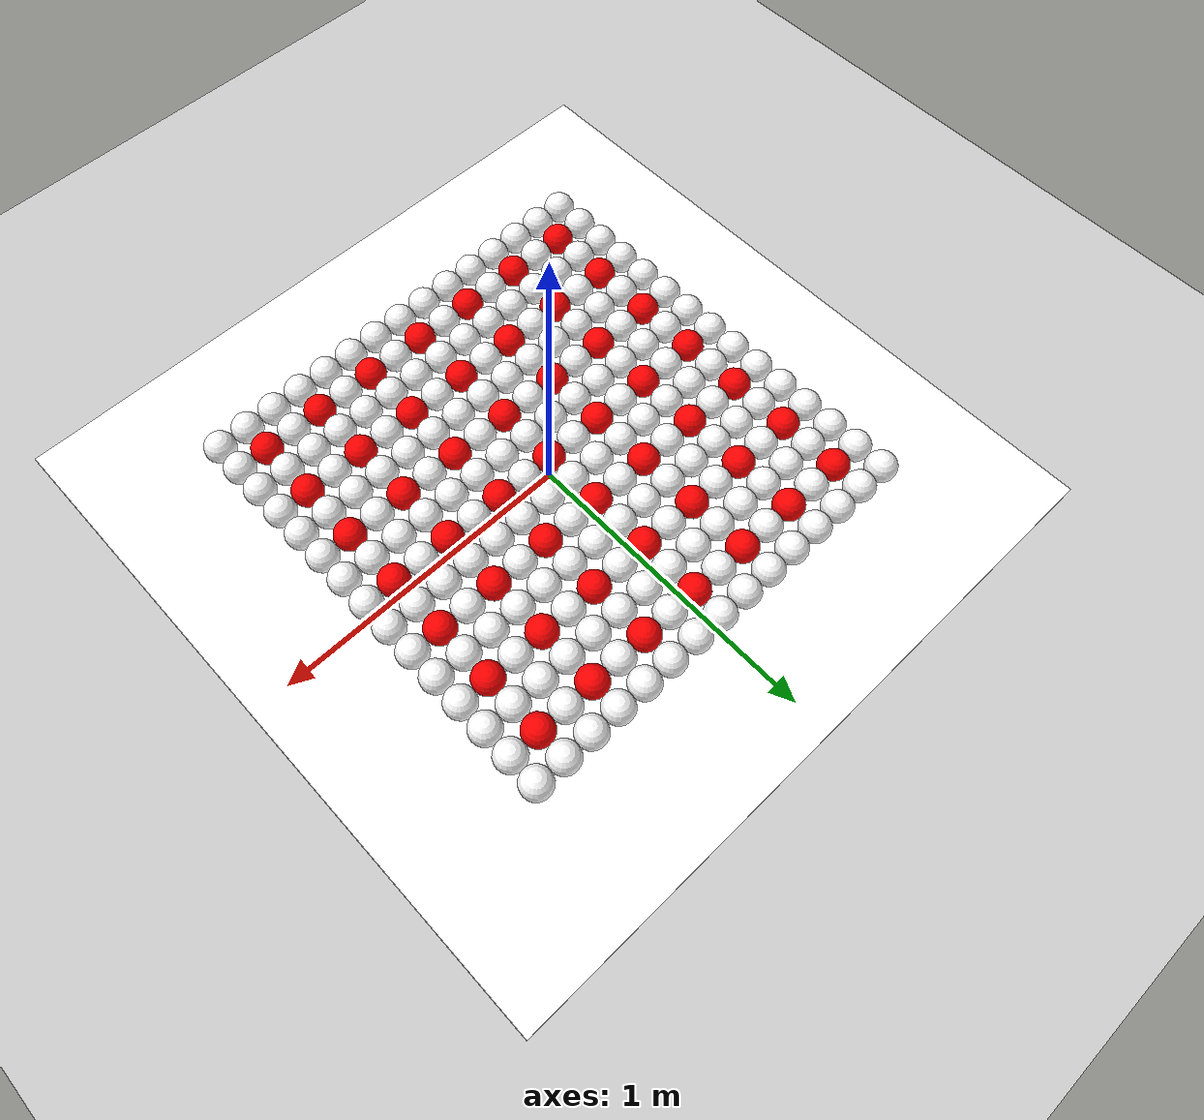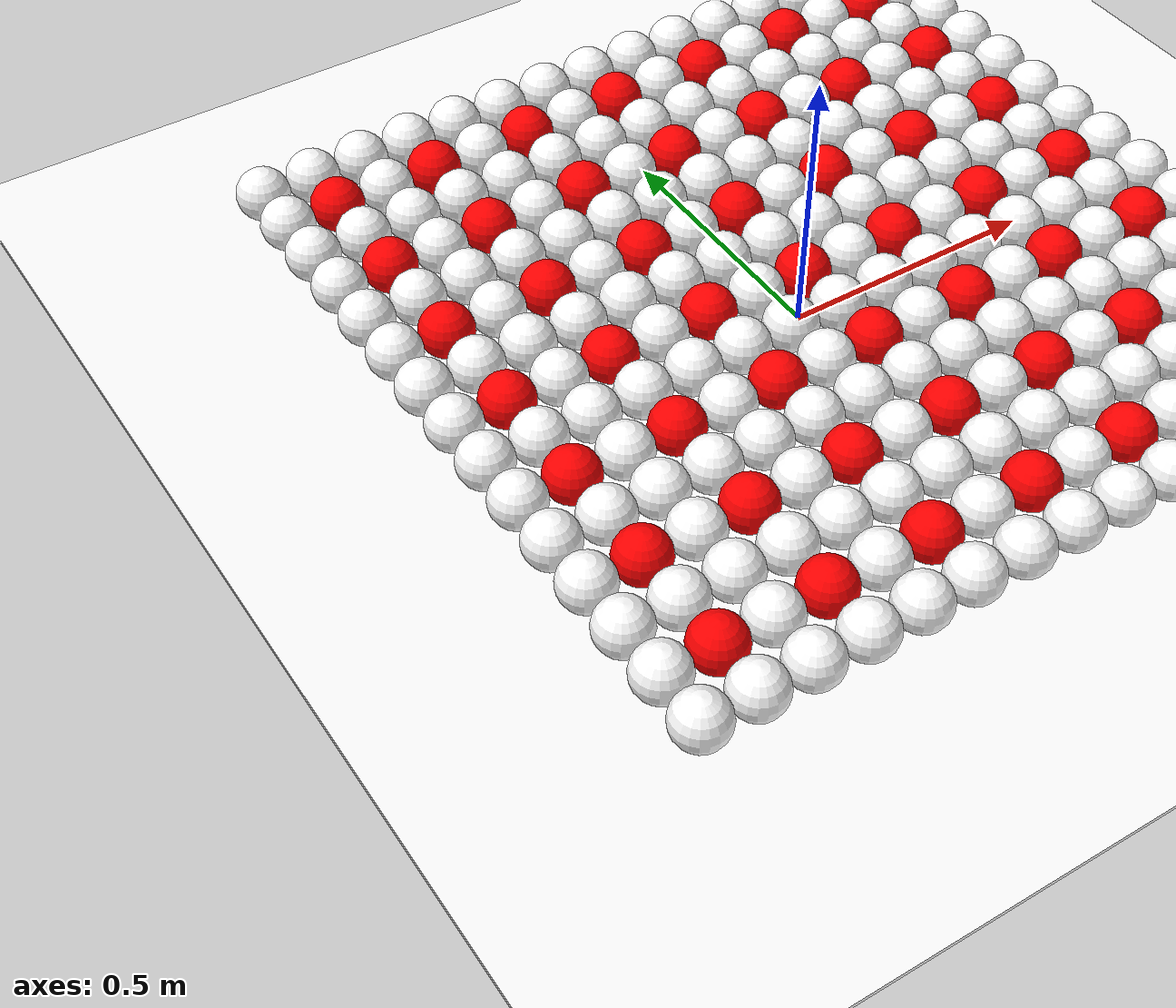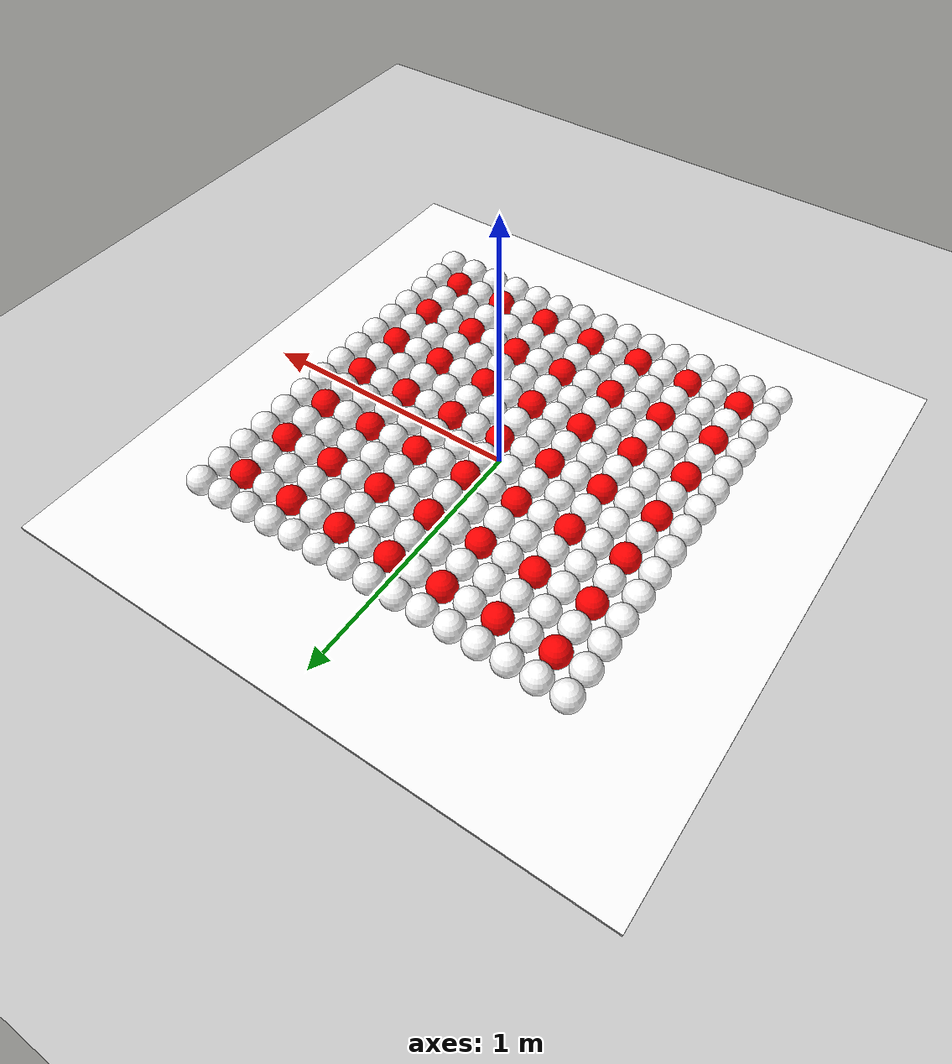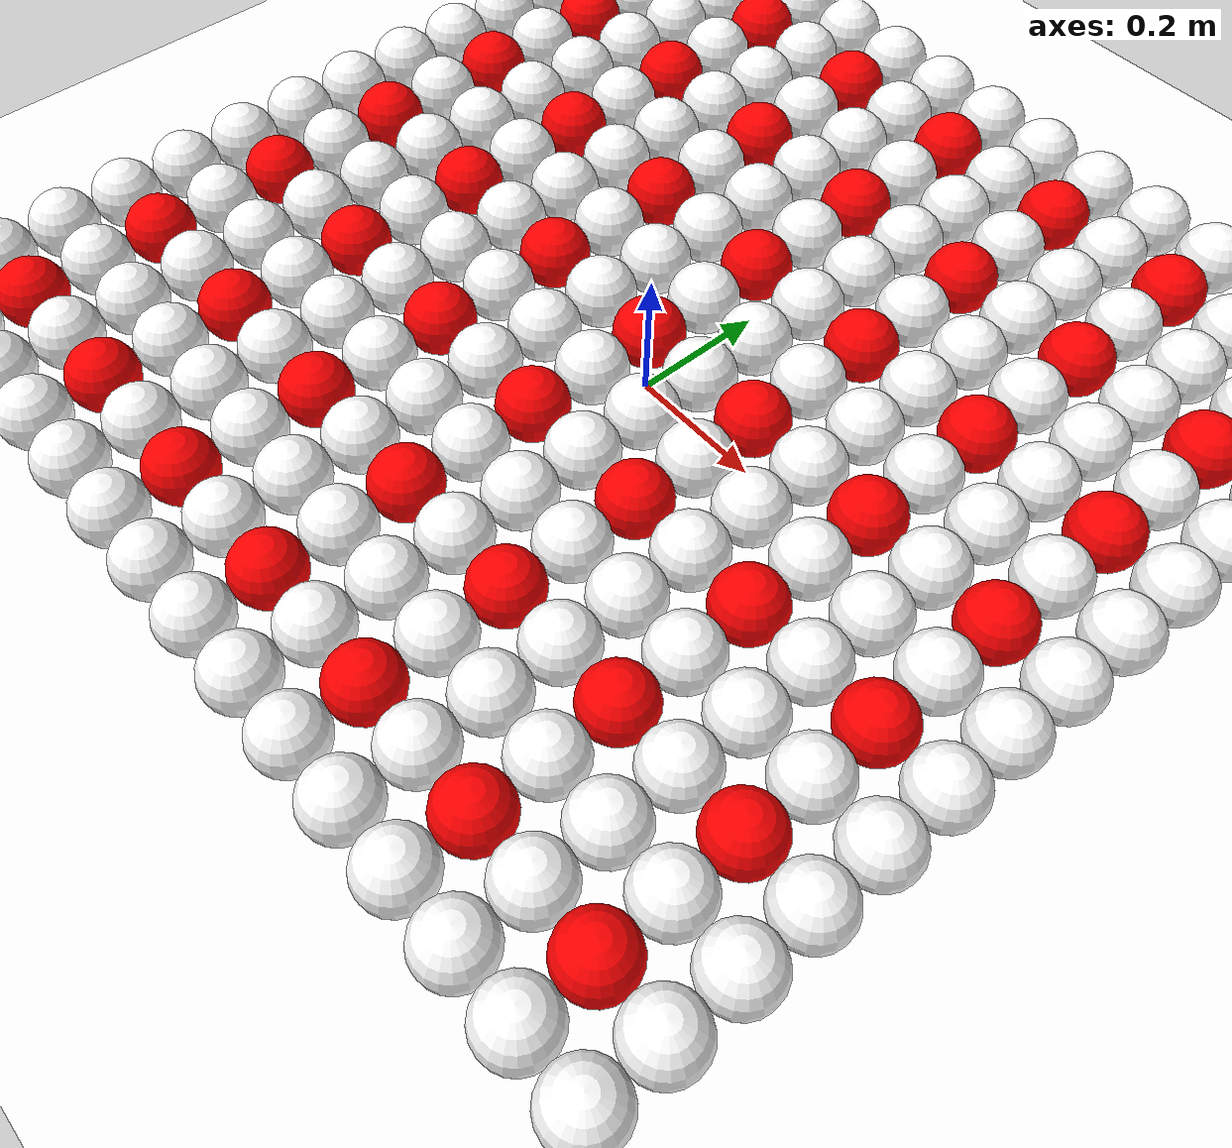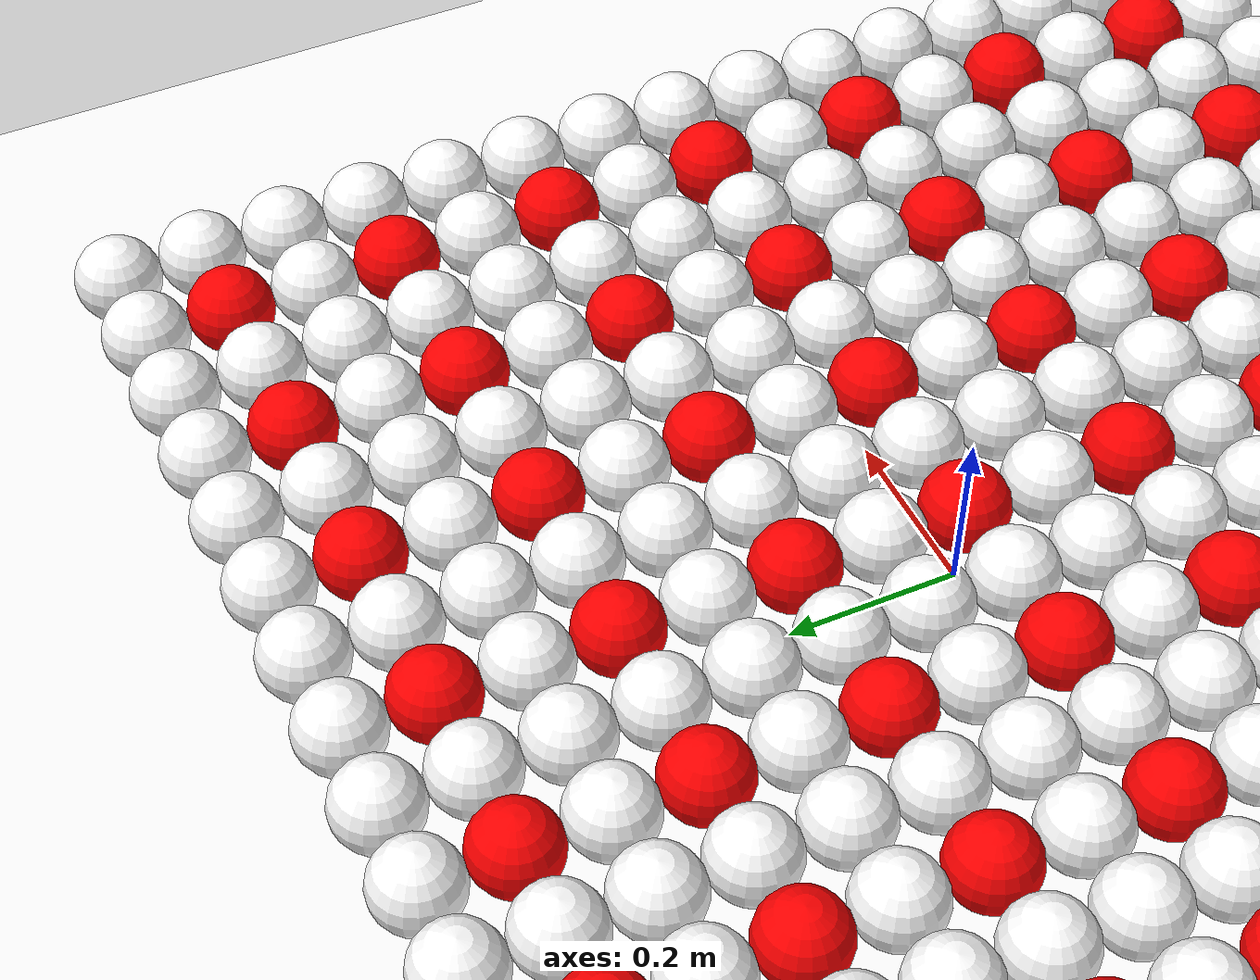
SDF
<?xml version='1.0'?>
<gazebo version='1.3'>
<world name='default'>

<include>
  <uri>model://ground_plane</uri>
</include>

<include>
  <uri>model://sun</uri>
</include>

<include>
  <uri>model://spring_board</uri>
</include>

<physics type='ode'>
  <gravity>0.0 0.0 -9.8</gravity>
  <ode>
    <solver>
      <iters>150</iters>
    </solver>
    <constraints>
      <cfm>0.2</cfm>
    </constraints>
  </ode>
</physics>

<include>
  <uri>model://box</uri>
  <pose>0 0 0.055 0 0 0</pose>
</include>

<gui fullscreen='0'>
  <camera name='user_camera'>
    <pose>0.130675 -0.121126 0.095229 0 0.347643 2.35619</pose>
    <view_controller>orbit</view_controller>
  </camera>
</gui>

</world>
</gazebo>

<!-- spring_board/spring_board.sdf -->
<sdf version='1.5'>
  <model name='spring_board'>
    <pose>0 0 0 0 -0 0</pose>
    <link name='plane'>
      <pose>0 0 0.001 0 -0 0</pose>
      <inertial>
        <mass>20</mass>
      </inertial>
      <collision name='collision'>
        <geometry>
          <box>
            <size>2.25 2.25 0.01</size>
          </box>
        </geometry>
        <surface>
          <friction>
            <ode>
              <mu>0</mu>
              <mu2>0</mu2>
            </ode>
          </friction>
        </surface>
      </collision>
      <visual name='visual'>
        <geometry>
          <box>
            <size>2.25 2.25 0.01</size>
          </box>
        </geometry>
        <material>
          <ambient>1 1 1 1</ambient>
          <diffuse>1 1 1 1</diffuse>
          <specular>0.1 0.1 0.1 1</specular>
          <emissive>0 0 0 0</emissive>
        </material>
      </visual>
    </link>
    <joint name='plane_joint' type='prismatic'>
      <parent>world</parent>
      <child>plane</child>
      <axis>
        <xyz>0 0 1</xyz>
        <limit>
          <lower>1e+16</lower>
          <upper>-1e+16</upper>
        </limit>
        <use_parent_model_frame>1</use_parent_model_frame>
      </axis>
    </joint>
    <link name='spring_1'>
      <pose>-0.7 0.7 0.111 0 -0 0</pose>
      <inertial>
        <mass>0.00235</mass>
      </inertial>
      <collision name='sphere_collision'>
        <geometry>
          <sphere>
            <radius>0.05</radius>
          </sphere>
        </geometry>
        <surface>
          <friction>
            <ode>
              <mu>0</mu>
              <mu2>0</mu2>
            </ode>
          </friction>
        </surface>
      </collision>
      <visual name='visual'>
        <geometry>
          <sphere>
            <radius>0.05</radius>
          </sphere>
        </geometry>
        <material>
          <ambient>1 1 1 1</ambient>
          <diffuse>1 1 1 1</diffuse>
          <specular>0.1 0.1 0.1 1</specular>
          <emissive>0 0 0 0</emissive>
        </material>
      </visual>
    </link>
    <joint name='spring_joint_1' type='prismatic'>
      <parent>plane</parent>
      <child>spring_1</child>
      <axis>
        <xyz>0 0 1</xyz>
        <limit>
          <lower>-1e+16</lower>
          <upper>1e+16</upper>
        </limit>
        <use_parent_model_frame>1</use_parent_model_frame>
      </axis>
    </joint>
    <link name='spring_2'>
      <pose>-0.6 0.7 0.111 0 -0 0</pose>
      <inertial>
        <mass>0.00235</mass>
      </inertial>
      <collision name='sphere_collision'>
        <geometry>
          <sphere>
            <radius>0.05</radius>
          </sphere>
        </geometry>
        <surface>
          <friction>
            <ode>
              <mu>0</mu>
              <mu2>0</mu2>
            </ode>
          </friction>
        </surface>
      </collision>
      <visual name='visual'>
        <geometry>
          <sphere>
            <radius>0.05</radius>
          </sphere>
        </geometry>
        <material>
          <ambient>1 1 1 1</ambient>
          <diffuse>1 1 1 1</diffuse>
          <specular>0.1 0.1 0.1 1</specular>
          <emissive>0 0 0 0</emissive>
        </material>
      </visual>
    </link>
    <joint name='spring_joint_2' type='prismatic'>
      <parent>plane</parent>
      <child>spring_2</child>
      <axis>
        <xyz>0 0 1</xyz>
        <limit>
          <lower>-1e+16</lower>
          <upper>1e+16</upper>
        </limit>
        <use_parent_model_frame>1</use_parent_model_frame>
      </axis>
    </joint>
    <link name='spring_3'>
      <pose>-0.5 0.7 0.111 0 -0 0</pose>
      <inertial>
        <mass>0.00235</mass>
      </inertial>
      <collision name='sphere_collision'>
        <geometry>
          <sphere>
            <radius>0.05</radius>
          </sphere>
        </geometry>
        <surface>
          <friction>
            <ode>
              <mu>0</mu>
              <mu2>0</mu2>
            </ode>
          </friction>
        </surface>
      </collision>
      <visual name='visual'>
        <geometry>
          <sphere>
            <radius>0.05</radius>
          </sphere>
        </geometry>
        <material>
          <ambient>1 1 1 1</ambient>
          <diffuse>1 1 1 1</diffuse>
          <specular>0.1 0.1 0.1 1</specular>
          <emissive>0 0 0 0</emissive>
        </material>
      </visual>
    </link>
    <joint name='spring_joint_3' type='prismatic'>
      <parent>plane</parent>
      <child>spring_3</child>
      <axis>
        <xyz>0 0 1</xyz>
        <limit>
          <lower>-1e+16</lower>
          <upper>1e+16</upper>
        </limit>
        <use_parent_model_frame>1</use_parent_model_frame>
      </axis>
    </joint>
    <link name='spring_4'>
      <pose>-0.4 0.7 0.111 0 -0 0</pose>
      <inertial>
        <mass>0.00235</mass>
      </inertial>
      <collision name='sphere_collision'>
        <geometry>
          <sphere>
            <radius>0.05</radius>
          </sphere>
        </geometry>
        <surface>
          <friction>
            <ode>
              <mu>0</mu>
              <mu2>0</mu2>
            </ode>
          </friction>
        </surface>
      </collision>
      <visual name='visual'>
        <geometry>
          <sphere>
            <radius>0.05</radius>
          </sphere>
        </geometry>
        <material>
          <ambient>1 1 1 1</ambient>
          <diffuse>1 1 1 1</diffuse>
          <specular>0.1 0.1 0.1 1</specular>
          <emissive>0 0 0 0</emissive>
        </material>
      </visual>
    </link>
    <joint name='spring_joint_4' type='prismatic'>
      <parent>plane</parent>
      <child>spring_4</child>
      <axis>
        <xyz>0 0 1</xyz>
        <limit>
          <lower>-1e+16</lower>
          <upper>1e+16</upper>
        </limit>
        <use_parent_model_frame>1</use_parent_model_frame>
      </axis>
    </joint>
    <link name='spring_5'>
      <pose>-0.3 0.7 0.111 0 -0 0</pose>
      <inertial>
        <mass>0.00235</mass>
      </inertial>
      <collision name='sphere_collision'>
        <geometry>
          <sphere>
            <radius>0.05</radius>
          </sphere>
        </geometry>
        <surface>
          <friction>
            <ode>
              <mu>0</mu>
              <mu2>0</mu2>
            </ode>
          </friction>
        </surface>
      </collision>
      <visual name='visual'>
        <geometry>
          <sphere>
            <radius>0.05</radius>
          </sphere>
        </geometry>
        <material>
          <ambient>1 1 1 1</ambient>
          <diffuse>1 1 1 1</diffuse>
          <specular>0.1 0.1 0.1 1</specular>
          <emissive>0 0 0 0</emissive>
        </material>
      </visual>
    </link>
    <joint name='spring_joint_5' type='prismatic'>
      <parent>plane</parent>
      <child>spring_5</child>
      <axis>
        <xyz>0 0 1</xyz>
        <limit>
          <lower>-1e+16</lower>
          <upper>1e+16</upper>
        </limit>
        <use_parent_model_frame>1</use_parent_model_frame>
      </axis>
    </joint>
    <link name='spring_6'>
      <pose>-0.2 0.7 0.111 0 -0 0</pose>
      <inertial>
        <mass>0.00235</mass>
      </inertial>
      <collision name='sphere_collision'>
        <geometry>
          <sphere>
            <radius>0.05</radius>
          </sphere>
        </geometry>
        <surface>
          <friction>
            <ode>
              <mu>0</mu>
              <mu2>0</mu2>
            </ode>
          </friction>
        </surface>
      </collision>
      <visual name='visual'>
        <geometry>
          <sphere>
            <radius>0.05</radius>
          </sphere>
        </geometry>
        <material>
          <ambient>1 1 1 1</ambient>
          <diffuse>1 1 1 1</diffuse>
          <specular>0.1 0.1 0.1 1</specular>
          <emissive>0 0 0 0</emissive>
        </material>
      </visual>
    </link>
    <joint name='spring_joint_6' type='prismatic'>
      <parent>plane</parent>
      <child>spring_6</child>
      <axis>
        <xyz>0 0 1</xyz>
        <limit>
          <lower>-1e+16</lower>
          <upper>1e+16</upper>
        </limit>
        <use_parent_model_frame>1</use_parent_model_frame>
      </axis>
    </joint>
    <link name='spring_7'>
      <pose>-0.1 0.7 0.111 0 -0 0</pose>
      <inertial>
        <mass>0.00235</mass>
      </inertial>
      <collision name='sphere_collision'>
        <geometry>
          <sphere>
            <radius>0.05</radius>
          </sphere>
        </geometry>
        <surface>
          <friction>
            <ode>
              <mu>0</mu>
              <mu2>0</mu2>
            </ode>
          </friction>
        </surface>
      </collision>
      <visual name='visual'>
        <geometry>
          <sphere>
            <radius>0.05</radius>
          </sphere>
        </geometry>
        <material>
          <ambient>1 1 1 1</ambient>
          <diffuse>1 1 1 1</diffuse>
          <specular>0.1 0.1 0.1 1</specular>
          <emissive>0 0 0 0</emissive>
        </material>
      </visual>
    </link>
    <joint name='spring_joint_7' type='prismatic'>
      <parent>plane</parent>
      <child>spring_7</child>
      <axis>
        <xyz>0 0 1</xyz>
        <limit>
          <lower>-1e+16</lower>
          <upper>1e+16</upper>
        </limit>
        <use_parent_model_frame>1</use_parent_model_frame>
      </axis>
    </joint>
    <link name='spring_8'>
      <pose>-2.77556e-17 0.7 0.111 0 -0 0</pose>
      <inertial>
        <mass>0.00235</mass>
      </inertial>
      <collision name='sphere_collision'>
        <geometry>
          <sphere>
            <radius>0.05</radius>
          </sphere>
        </geometry>
        <surface>
          <friction>
            <ode>
              <mu>0</mu>
              <mu2>0</mu2>
            </ode>
          </friction>
        </surface>
      </collision>
      <visual name='visual'>
        <geometry>
          <sphere>
            <radius>0.05</radius>
          </sphere>
        </geometry>
        <material>
          <ambient>1 1 1 1</ambient>
          <diffuse>1 1 1 1</diffuse>
          <specular>0.1 0.1 0.1 1</specular>
          <emissive>0 0 0 0</emissive>
        </material>
      </visual>
    </link>
    <joint name='spring_joint_8' type='prismatic'>
      <parent>plane</parent>
      <child>spring_8</child>
      <axis>
        <xyz>0 0 1</xyz>
        <limit>
          <lower>-1e+16</lower>
          <upper>1e+16</upper>
        </limit>
        <use_parent_model_frame>1</use_parent_model_frame>
      </axis>
    </joint>
    <link name='spring_9'>
      <pose>0.1 0.7 0.111 0 -0 0</pose>
      <inertial>
        <mass>0.00235</mass>
      </inertial>
      <collision name='sphere_collision'>
        <geometry>
          <sphere>
            <radius>0.05</radius>
          </sphere>
        </geometry>
        <surface>
          <friction>
            <ode>
              <mu>0</mu>
              <mu2>0</mu2>
            </ode>
          </friction>
        </surface>
      </collision>
      <visual name='visual'>
        <geometry>
          <sphere>
            <radius>0.05</radius>
          </sphere>
        </geometry>
        <material>
          <ambient>1 1 1 1</ambient>
          <diffuse>1 1 1 1</diffuse>
          <specular>0.1 0.1 0.1 1</specular>
          <emissive>0 0 0 0</emissive>
        </material>
      </visual>
    </link>
    <joint name='spring_joint_9' type='prismatic'>
      <parent>plane</parent>
      <child>spring_9</child>
      <axis>
        <xyz>0 0 1</xyz>
        <limit>
          <lower>-1e+16</lower>
          <upper>1e+16</upper>
        </limit>
        <use_parent_model_frame>1</use_parent_model_frame>
      </axis>
    </joint>
    <link name='spring_10'>
      <pose>0.2 0.7 0.111 0 -0 0</pose>
      <inertial>
        <mass>0.00235</mass>
      </inertial>
      <collision name='sphere_collision'>
        <geometry>
          <sphere>
            <radius>0.05</radius>
          </sphere>
        </geometry>
        <surface>
          <friction>
            <ode>
              <mu>0</mu>
              <mu2>0</mu2>
            </ode>
          </friction>
        </surface>
      </collision>
      <visual name='visual'>
        <geometry>
          <sphere>
            <radius>0.05</radius>
          </sphere>
        </geometry>
        <material>
          <ambient>1 1 1 1</ambient>
          <diffuse>1 1 1 1</diffuse>
          <specular>0.1 0.1 0.1 1</specular>
          <emissive>0 0 0 0</emissive>
        </material>
      </visual>
    </link>
    <joint name='spring_joint_10' type='prismatic'>
      <parent>plane</parent>
      <child>spring_10</child>
      <axis>
        <xyz>0 0 1</xyz>
        <limit>
          <lower>-1e+16</lower>
          <upper>1e+16</upper>
        </limit>
        <use_parent_model_frame>1</use_parent_model_frame>
      </axis>
    </joint>
    <link name='spring_11'>
      <pose>0.3 0.7 0.111 0 -0 0</pose>
      <inertial>
        <mass>0.00235</mass>
      </inertial>
      <collision name='sphere_collision'>
        <geometry>
          <sphere>
            <radius>0.05</radius>
          </sphere>
        </geometry>
        <surface>
          <friction>
            <ode>
              <mu>0</mu>
              <mu2>0</mu2>
            </ode>
          </friction>
        </surface>
      </collision>
      <visual name='visual'>
        <geometry>
          <sphere>
            <radius>0.05</radius>
          </sphere>
        </geometry>
        <material>
          <ambient>1 1 1 1</ambient>
          <diffuse>1 1 1 1</diffuse>
          <specular>0.1 0.1 0.1 1</specular>
          <emissive>0 0 0 0</emissive>
        </material>
      </visual>
    </link>
    <joint name='spring_joint_11' type='prismatic'>
      <parent>plane</parent>
      <child>spring_11</child>
      <axis>
        <xyz>0 0 1</xyz>
        <limit>
          <lower>-1e+16</lower>
          <upper>1e+16</upper>
        </limit>
        <use_parent_model_frame>1</use_parent_model_frame>
      </axis>
    </joint>
    <link name='spring_12'>
      <pose>0.4 0.7 0.111 0 -0 0</pose>
      <inertial>
        <mass>0.00235</mass>
      </inertial>
      <collision name='sphere_collision'>
        <geometry>
          <sphere>
            <radius>0.05</radius>
          </sphere>
        </geometry>
        <surface>
          <friction>
            <ode>
              <mu>0</mu>
              <mu2>0</mu2>
            </ode>
          </friction>
        </surface>
      </collision>
      <visual name='visual'>
        <geometry>
          <sphere>
            <radius>0.05</radius>
          </sphere>
        </geometry>
        <material>
          <ambient>1 1 1 1</ambient>
          <diffuse>1 1 1 1</diffuse>
          <specular>0.1 0.1 0.1 1</specular>
          <emissive>0 0 0 0</emissive>
        </material>
      </visual>
    </link>
    <joint name='spring_joint_12' type='prismatic'>
      <parent>plane</parent>
      <child>spring_12</child>
      <axis>
        <xyz>0 0 1</xyz>
        <limit>
          <lower>-1e+16</lower>
          <upper>1e+16</upper>
        </limit>
        <use_parent_model_frame>1</use_parent_model_frame>
      </axis>
    </joint>
    <link name='spring_13'>
      <pose>0.5 0.7 0.111 0 -0 0</pose>
      <inertial>
        <mass>0.00235</mass>
      </inertial>
      <collision name='sphere_collision'>
        <geometry>
          <sphere>
            <radius>0.05</radius>
          </sphere>
        </geometry>
        <surface>
          <friction>
            <ode>
              <mu>0</mu>
              <mu2>0</mu2>
            </ode>
          </friction>
        </surface>
      </collision>
      <visual name='visual'>
        <geometry>
          <sphere>
            <radius>0.05</radius>
          </sphere>
        </geometry>
        <material>
          <ambient>1 1 1 1</ambient>
          <diffuse>1 1 1 1</diffuse>
          <specular>0.1 0.1 0.1 1</specular>
          <emissive>0 0 0 0</emissive>
        </material>
      </visual>
    </link>
    <joint name='spring_joint_13' type='prismatic'>
      <parent>plane</parent>
      <child>spring_13</child>
      <axis>
        <xyz>0 0 1</xyz>
        <limit>
          <lower>-1e+16</lower>
          <upper>1e+16</upper>
        </limit>
        <use_parent_model_frame>1</use_parent_model_frame>
      </axis>
    </joint>
    <link name='spring_14'>
      <pose>0.6 0.7 0.111 0 -0 0</pose>
      <inertial>
        <mass>0.00235</mass>
      </inertial>
      <collision name='sphere_collision'>
        <geometry>
          <sphere>
            <radius>0.05</radius>
          </sphere>
        </geometry>
        <surface>
          <friction>
            <ode>
              <mu>0</mu>
              <mu2>0</mu2>
            </ode>
          </friction>
        </surface>
      </collision>
      <visual name='visual'>
        <geometry>
          <sphere>
            <radius>0.05</radius>
          </sphere>
        </geometry>
        <material>
          <ambient>1 1 1 1</ambient>
          <diffuse>1 1 1 1</diffuse>
          <specular>0.1 0.1 0.1 1</specular>
          <emissive>0 0 0 0</emissive>
        </material>
      </visual>
    </link>
    <joint name='spring_joint_14' type='prismatic'>
      <parent>plane</parent>
      <child>spring_14</child>
      <axis>
        <xyz>0 0 1</xyz>
        <limit>
          <lower>-1e+16</lower>
          <upper>1e+16</upper>
        </limit>
        <use_parent_model_frame>1</use_parent_model_frame>
      </axis>
    </joint>
    <link name='spring_15'>
      <pose>0.7 0.7 0.111 0 -0 0</pose>
      <inertial>
        <mass>0.00235</mass>
      </inertial>
      <collision name='sphere_collision'>
        <geometry>
          <sphere>
            <radius>0.05</radius>
          </sphere>
        </geometry>
        <surface>
          <friction>
            <ode>
              <mu>0</mu>
              <mu2>0</mu2>
            </ode>
          </friction>
        </surface>
      </collision>
      <visual name='visual'>
        <geometry>
          <sphere>
            <radius>0.05</radius>
          </sphere>
        </geometry>
        <material>
          <ambient>1 1 1 1</ambient>
          <diffuse>1 1 1 1</diffuse>
          <specular>0.1 0.1 0.1 1</specular>
          <emissive>0 0 0 0</emissive>
        </material>
      </visual>
    </link>
    <joint name='spring_joint_15' type='prismatic'>
      <parent>plane</parent>
      <child>spring_15</child>
      <axis>
        <xyz>0 0 1</xyz>
        <limit>
          <lower>-1e+16</lower>
          <upper>1e+16</upper>
        </limit>
        <use_parent_model_frame>1</use_parent_model_frame>
      </axis>
    </joint>
    <link name='spring_16'>
      <pose>-0.7 0.6 0.111 0 -0 0</pose>
      <inertial>
        <mass>0.00235</mass>
      </inertial>
      <collision name='sphere_collision'>
        <geometry>
          <sphere>
            <radius>0.05</radius>
          </sphere>
        </geometry>
        <surface>
          <friction>
            <ode>
              <mu>0</mu>
              <mu2>0</mu2>
            </ode>
          </friction>
        </surface>
      </collision>
      <visual name='visual'>
        <geometry>
          <sphere>
            <radius>0.05</radius>
          </sphere>
        </geometry>
        <material>
          <ambient>1 1 1 1</ambient>
          <diffuse>1 1 1 1</diffuse>
          <specular>0.1 0.1 0.1 1</specular>
          <emissive>0 0 0 0</emissive>
        </material>
      </visual>
    </link>
    <joint name='spring_joint_16' type='prismatic'>
      <parent>plane</parent>
      <child>spring_16</child>
      <axis>
        <xyz>0 0 1</xyz>
        <limit>
          <lower>-1e+16</lower>
          <upper>1e+16</upper>
        </limit>
        <use_parent_model_frame>1</use_parent_model_frame>
      </axis>
    </joint>
    <link name='spring_17'>
      <pose>-0.6 0.6 0.111 0 -0 0</pose>
      <inertial>
        <mass>0.00235</mass>
      </inertial>
      <collision name='sphere_collision'>
        <geometry>
          <sphere>
            <radius>0.05</radius>
          </sphere>
        </geometry>
        <surface>
          <friction>
            <ode>
              <mu>0</mu>
              <mu2>0</mu2>
            </ode>
          </friction>
        </surface>
      </collision>
      <visual name='visual'>
        <geometry>
          <sphere>
            <radius>0.05</radius>
          </sphere>
        </geometry>
        <material>
          <ambient>1 0 0 1</ambient>
          <diffuse>1 0 0 1</diffuse>
          <specular>0.1 0.1 0.1 1</specular>
          <emissive>0 0 0 0</emissive>
        </material>
      </visual>
    </link>
    <joint name='spring_joint_17' type='prismatic'>
      <parent>plane</parent>
      <child>spring_17</child>
      <axis>
        <xyz>0 0 1</xyz>
        <limit>
          <lower>-1e+16</lower>
          <upper>1e+16</upper>
        </limit>
        <use_parent_model_frame>1</use_parent_model_frame>
      </axis>
    </joint>
    <link name='spring_18'>
      <pose>-0.5 0.6 0.111 0 -0 0</pose>
      <inertial>
        <mass>0.00235</mass>
      </inertial>
      <collision name='sphere_collision'>
        <geometry>
          <sphere>
            <radius>0.05</radius>
          </sphere>
        </geometry>
        <surface>
          <friction>
            <ode>
              <mu>0</mu>
              <mu2>0</mu2>
            </ode>
          </friction>
        </surface>
      </collision>
      <visual name='visual'>
        <geometry>
          <sphere>
            <radius>0.05</radius>
          </sphere>
        </geometry>
        <material>
          <ambient>1 1 1 1</ambient>
          <diffuse>1 1 1 1</diffuse>
          <specular>0.1 0.1 0.1 1</specular>
          <emissive>0 0 0 0</emissive>
        </material>
      </visual>
    </link>
    <joint name='spring_joint_18' type='prismatic'>
      <parent>plane</parent>
      <child>spring_18</child>
      <axis>
        <xyz>0 0 1</xyz>
        <limit>
          <lower>-1e+16</lower>
          <upper>1e+16</upper>
        </limit>
        <use_parent_model_frame>1</use_parent_model_frame>
      </axis>
    </joint>
    <link name='spring_19'>
      <pose>-0.4 0.6 0.111 0 -0 0</pose>
      <inertial>
        <mass>0.00235</mass>
      </inertial>
      <collision name='sphere_collision'>
        <geometry>
          <sphere>
            <radius>0.05</radius>
          </sphere>
        </geometry>
        <surface>
          <friction>
            <ode>
              <mu>0</mu>
              <mu2>0</mu2>
            </ode>
          </friction>
        </surface>
      </collision>
      <visual name='visual'>
        <geometry>
          <sphere>
            <radius>0.05</radius>
          </sphere>
        </geometry>
        <material>
          <ambient>1 0 0 1</ambient>
          <diffuse>1 0 0 1</diffuse>
          <specular>0.1 0.1 0.1 1</specular>
          <emissive>0 0 0 0</emissive>
        </material>
      </visual>
    </link>
    <joint name='spring_joint_19' type='prismatic'>
      <parent>plane</parent>
      <child>spring_19</child>
      <axis>
        <xyz>0 0 1</xyz>
        <limit>
          <lower>-1e+16</lower>
          <upper>1e+16</upper>
        </limit>
        <use_parent_model_frame>1</use_parent_model_frame>
      </axis>
    </joint>
    <link name='spring_20'>
      <pose>-0.3 0.6 0.111 0 -0 0</pose>
      <inertial>
        <mass>0.00235</mass>
      </inertial>
      <collision name='sphere_collision'>
        <geometry>
          <sphere>
            <radius>0.05</radius>
          </sphere>
        </geometry>
        <surface>
          <friction>
            <ode>
              <mu>0</mu>
              <mu2>0</mu2>
            </ode>
          </friction>
        </surface>
      </collision>
      <visual name='visual'>
        <geometry>
          <sphere>
            <radius>0.05</radius>
          </sphere>
        </geometry>
        <material>
          <ambient>1 1 1 1</ambient>
          <diffuse>1 1 1 1</diffuse>
          <specular>0.1 0.1 0.1 1</specular>
          <emissive>0 0 0 0</emissive>
        </material>
      </visual>
    </link>
    <joint name='spring_joint_20' type='prismatic'>
      <parent>plane</parent>
      <child>spring_20</child>
      <axis>
        <xyz>0 0 1</xyz>
        <limit>
          <lower>-1e+16</lower>
          <upper>1e+16</upper>
        </limit>
        <use_parent_model_frame>1</use_parent_model_frame>
      </axis>
    </joint>
    <link name='spring_21'>
      <pose>-0.2 0.6 0.111 0 -0 0</pose>
      <inertial>
        <mass>0.00235</mass>
      </inertial>
      <collision name='sphere_collision'>
        <geometry>
          <sphere>
            <radius>0.05</radius>
          </sphere>
        </geometry>
        <surface>
          <friction>
            <ode>
              <mu>0</mu>
              <mu2>0</mu2>
            </ode>
          </friction>
        </surface>
      </collision>
      <visual name='visual'>
        <geometry>
          <sphere>
            <radius>0.05</radius>
          </sphere>
        </geometry>
        <material>
          <ambient>1 0 0 1</ambient>
          <diffuse>1 0 0 1</diffuse>
          <specular>0.1 0.1 0.1 1</specular>
          <emissive>0 0 0 0</emissive>
        </material>
      </visual>
    </link>
    <joint name='spring_joint_21' type='prismatic'>
      <parent>plane</parent>
      <child>spring_21</child>
      <axis>
        <xyz>0 0 1</xyz>
        <limit>
          <lower>-1e+16</lower>
          <upper>1e+16</upper>
        </limit>
        <use_parent_model_frame>1</use_parent_model_frame>
      </axis>
    </joint>
    <link name='spring_22'>
      <pose>-0.1 0.6 0.111 0 -0 0</pose>
      <inertial>
        <mass>0.00235</mass>
      </inertial>
      <collision name='sphere_collision'>
        <geometry>
          <sphere>
            <radius>0.05</radius>
          </sphere>
        </geometry>
        <surface>
          <friction>
            <ode>
              <mu>0</mu>
              <mu2>0</mu2>
            </ode>
          </friction>
        </surface>
      </collision>
      <visual name='visual'>
        <geometry>
          <sphere>
            <radius>0.05</radius>
          </sphere>
        </geometry>
        <material>
          <ambient>1 1 1 1</ambient>
          <diffuse>1 1 1 1</diffuse>
          <specular>0.1 0.1 0.1 1</specular>
          <emissive>0 0 0 0</emissive>
        </material>
      </visual>
    </link>
    <joint name='spring_joint_22' type='prismatic'>
      <parent>plane</parent>
      <child>spring_22</child>
      <axis>
        <xyz>0 0 1</xyz>
        <limit>
          <lower>-1e+16</lower>
          <upper>1e+16</upper>
        </limit>
        <use_parent_model_frame>1</use_parent_model_frame>
      </axis>
    </joint>
    <link name='spring_23'>
      <pose>-2.77556e-17 0.6 0.111 0 -0 0</pose>
      <inertial>
        <mass>0.00235</mass>
      </inertial>
      <collision name='sphere_collision'>
        <geometry>
          <sphere>
            <radius>0.05</radius>
          </sphere>
        </geometry>
        <surface>
          <friction>
            <ode>
              <mu>0</mu>
              <mu2>0</mu2>
            </ode>
          </friction>
        </surface>
      </collision>
      <visual name='visual'>
        <geometry>
          <sphere>
            <radius>0.05</radius>
          </sphere>
        </geometry>
        <material>
          <ambient>1 0 0 1</ambient>
          <diffuse>1 0 0 1</diffuse>
          <specular>0.1 0.1 0.1 1</specular>
          <emissive>0 0 0 0</emissive>
        </material>
      </visual>
    </link>
    <joint name='spring_joint_23' type='prismatic'>
      <parent>plane</parent>
      <child>spring_23</child>
      <axis>
        <xyz>0 0 1</xyz>
        <limit>
          <lower>-1e+16</lower>
          <upper>1e+16</upper>
        </limit>
        <use_parent_model_frame>1</use_parent_model_frame>
      </axis>
    </joint>
    <link name='spring_24'>
      <pose>0.1 0.6 0.111 0 -0 0</pose>
      <inertial>
        <mass>0.00235</mass>
      </inertial>
      <collision name='sphere_collision'>
        <geometry>
          <sphere>
            <radius>0.05</radius>
          </sphere>
        </geometry>
        <surface>
          <friction>
            <ode>
              <mu>0</mu>
              <mu2>0</mu2>
            </ode>
          </friction>
        </surface>
      </collision>
      <visual name='visual'>
        <geometry>
          <sphere>
            <radius>0.05</radius>
          </sphere>
        </geometry>
        <material>
          <ambient>1 1 1 1</ambient>
          <diffuse>1 1 1 1</diffuse>
          <specular>0.1 0.1 0.1 1</specular>
          <emissive>0 0 0 0</emissive>
        </material>
      </visual>
    </link>
    <joint name='spring_joint_24' type='prismatic'>
      <parent>plane</parent>
      <child>spring_24</child>
      <axis>
        <xyz>0 0 1</xyz>
        <limit>
          <lower>-1e+16</lower>
          <upper>1e+16</upper>
        </limit>
        <use_parent_model_frame>1</use_parent_model_frame>
      </axis>
    </joint>
    <link name='spring_25'>
      <pose>0.2 0.6 0.111 0 -0 0</pose>
      <inertial>
        <mass>0.00235</mass>
      </inertial>
      <collision name='sphere_collision'>
        <geometry>
          <sphere>
            <radius>0.05</radius>
          </sphere>
        </geometry>
        <surface>
          <friction>
            <ode>
              <mu>0</mu>
              <mu2>0</mu2>
            </ode>
          </friction>
        </surface>
      </collision>
      <visual name='visual'>
        <geometry>
          <sphere>
            <radius>0.05</radius>
          </sphere>
        </geometry>
        <material>
          <ambient>1 0 0 1</ambient>
          <diffuse>1 0 0 1</diffuse>
          <specular>0.1 0.1 0.1 1</specular>
          <emissive>0 0 0 0</emissive>
        </material>
      </visual>
    </link>
    <joint name='spring_joint_25' type='prismatic'>
      <parent>plane</parent>
      <child>spring_25</child>
      <axis>
        <xyz>0 0 1</xyz>
        <limit>
          <lower>-1e+16</lower>
          <upper>1e+16</upper>
        </limit>
        <use_parent_model_frame>1</use_parent_model_frame>
      </axis>
    </joint>
    <link name='spring_26'>
      <pose>0.3 0.6 0.111 0 -0 0</pose>
      <inertial>
        <mass>0.00235</mass>
      </inertial>
      <collision name='sphere_collision'>
        <geometry>
          <sphere>
            <radius>0.05</radius>
          </sphere>
        </geometry>
        <surface>
          <friction>
            <ode>
              <mu>0</mu>
              <mu2>0</mu2>
            </ode>
          </friction>
        </surface>
      </collision>
      <visual name='visual'>
        <geometry>
          <sphere>
            <radius>0.05</radius>
          </sphere>
        </geometry>
        <material>
          <ambient>1 1 1 1</ambient>
          <diffuse>1 1 1 1</diffuse>
          <specular>0.1 0.1 0.1 1</specular>
          <emissive>0 0 0 0</emissive>
        </material>
      </visual>
    </link>
    <joint name='spring_joint_26' type='prismatic'>
      <parent>plane</parent>
      <child>spring_26</child>
      <axis>
        <xyz>0 0 1</xyz>
        <limit>
          <lower>-1e+16</lower>
          <upper>1e+16</upper>
        </limit>
        <use_parent_model_frame>1</use_parent_model_frame>
      </axis>
    </joint>
    <link name='spring_27'>
      <pose>0.4 0.6 0.111 0 -0 0</pose>
      <inertial>
        <mass>0.00235</mass>
      </inertial>
      <collision name='sphere_collision'>
        <geometry>
          <sphere>
            <radius>0.05</radius>
          </sphere>
        </geometry>
        <surface>
          <friction>
            <ode>
              <mu>0</mu>
              <mu2>0</mu2>
            </ode>
          </friction>
        </surface>
      </collision>
      <visual name='visual'>
        <geometry>
          <sphere>
            <radius>0.05</radius>
          </sphere>
        </geometry>
        <material>
          <ambient>1 0 0 1</ambient>
          <diffuse>1 0 0 1</diffuse>
          <specular>0.1 0.1 0.1 1</specular>
          <emissive>0 0 0 0</emissive>
        </material>
      </visual>
    </link>
    <joint name='spring_joint_27' type='prismatic'>
      <parent>plane</parent>
      <child>spring_27</child>
      <axis>
        <xyz>0 0 1</xyz>
        <limit>
          <lower>-1e+16</lower>
          <upper>1e+16</upper>
        </limit>
        <use_parent_model_frame>1</use_parent_model_frame>
      </axis>
    </joint>
    <link name='spring_28'>
      <pose>0.5 0.6 0.111 0 -0 0</pose>
      <inertial>
        <mass>0.00235</mass>
      </inertial>
      <collision name='sphere_collision'>
        <geometry>
          <sphere>
            <radius>0.05</radius>
          </sphere>
        </geometry>
        <surface>
          <friction>
            <ode>
              <mu>0</mu>
              <mu2>0</mu2>
            </ode>
          </friction>
        </surface>
      </collision>
      <visual name='visual'>
        <geometry>
          <sphere>
            <radius>0.05</radius>
          </sphere>
        </geometry>
        <material>
          <ambient>1 1 1 1</ambient>
          <diffuse>1 1 1 1</diffuse>
          <specular>0.1 0.1 0.1 1</specular>
          <emissive>0 0 0 0</emissive>
        </material>
      </visual>
    </link>
    <joint name='spring_joint_28' type='prismatic'>
      <parent>plane</parent>
      <child>spring_28</child>
      <axis>
        <xyz>0 0 1</xyz>
        <limit>
          <lower>-1e+16</lower>
          <upper>1e+16</upper>
        </limit>
        <use_parent_model_frame>1</use_parent_model_frame>
      </axis>
    </joint>
    <link name='spring_29'>
      <pose>0.6 0.6 0.111 0 -0 0</pose>
      <inertial>
        <mass>0.00235</mass>
      </inertial>
      <collision name='sphere_collision'>
        <geometry>
          <sphere>
            <radius>0.05</radius>
          </sphere>
        </geometry>
        <surface>
          <friction>
            <ode>
              <mu>0</mu>
              <mu2>0</mu2>
            </ode>
          </friction>
        </surface>
      </collision>
      <visual name='visual'>
        <geometry>
          <sphere>
            <radius>0.05</radius>
          </sphere>
        </geometry>
        <material>
          <ambient>1 0 0 1</ambient>
          <diffuse>1 0 0 1</diffuse>
          <specular>0.1 0.1 0.1 1</specular>
          <emissive>0 0 0 0</emissive>
        </material>
      </visual>
    </link>
    <joint name='spring_joint_29' type='prismatic'>
      <parent>plane</parent>
      <child>spring_29</child>
      <axis>
        <xyz>0 0 1</xyz>
        <limit>
          <lower>-1e+16</lower>
          <upper>1e+16</upper>
        </limit>
        <use_parent_model_frame>1</use_parent_model_frame>
      </axis>
    </joint>
    <link name='spring_30'>
      <pose>0.7 0.6 0.111 0 -0 0</pose>
      <inertial>
        <mass>0.00235</mass>
      </inertial>
      <collision name='sphere_collision'>
        <geometry>
          <sphere>
            <radius>0.05</radius>
          </sphere>
        </geometry>
        <surface>
          <friction>
            <ode>
              <mu>0</mu>
              <mu2>0</mu2>
            </ode>
          </friction>
        </surface>
      </collision>
      <visual name='visual'>
        <geometry>
          <sphere>
            <radius>0.05</radius>
          </sphere>
        </geometry>
        <material>
          <ambient>1 1 1 1</ambient>
          <diffuse>1 1 1 1</diffuse>
          <specular>0.1 0.1 0.1 1</specular>
          <emissive>0 0 0 0</emissive>
        </material>
      </visual>
    </link>
    <joint name='spring_joint_30' type='prismatic'>
      <parent>plane</parent>
      <child>spring_30</child>
      <axis>
        <xyz>0 0 1</xyz>
        <limit>
          <lower>-1e+16</lower>
          <upper>1e+16</upper>
        </limit>
        <use_parent_model_frame>1</use_parent_model_frame>
      </axis>
    </joint>
    <link name='spring_31'>
      <pose>-0.7 0.5 0.111 0 -0 0</pose>
      <inertial>
        <mass>0.00235</mass>
      </inertial>
      <collision name='sphere_collision'>
        <geometry>
          <sphere>
            <radius>0.05</radius>
          </sphere>
        </geometry>
        <surface>
          <friction>
            <ode>
              <mu>0</mu>
              <mu2>0</mu2>
            </ode>
          </friction>
        </surface>
      </collision>
      <visual name='visual'>
        <geometry>
          <sphere>
            <radius>0.05</radius>
          </sphere>
        </geometry>
        <material>
          <ambient>1 1 1 1</ambient>
          <diffuse>1 1 1 1</diffuse>
          <specular>0.1 0.1 0.1 1</specular>
          <emissive>0 0 0 0</emissive>
        </material>
      </visual>
    </link>
    <joint name='spring_joint_31' type='prismatic'>
      <parent>plane</parent>
      <child>spring_31</child>
      <axis>
        <xyz>0 0 1</xyz>
        <limit>
          <lower>-1e+16</lower>
          <upper>1e+16</upper>
        </limit>
        <use_parent_model_frame>1</use_parent_model_frame>
      </axis>
    </joint>
    <link name='spring_32'>
      <pose>-0.6 0.5 0.111 0 -0 0</pose>
      <inertial>
        <mass>0.00235</mass>
      </inertial>
      <collision name='sphere_collision'>
        <geometry>
          <sphere>
            <radius>0.05</radius>
          </sphere>
        </geometry>
        <surface>
          <friction>
            <ode>
              <mu>0</mu>
              <mu2>0</mu2>
            </ode>
          </friction>
        </surface>
      </collision>
      <visual name='visual'>
        <geometry>
          <sphere>
            <radius>0.05</radius>
          </sphere>
        </geometry>
        <material>
          <ambient>1 1 1 1</ambient>
          <diffuse>1 1 1 1</diffuse>
          <specular>0.1 0.1 0.1 1</specular>
          <emissive>0 0 0 0</emissive>
        </material>
      </visual>
    </link>
    <joint name='spring_joint_32' type='prismatic'>
      <parent>plane</parent>
      <child>spring_32</child>
      <axis>
        <xyz>0 0 1</xyz>
        <limit>
          <lower>-1e+16</lower>
          <upper>1e+16</upper>
        </limit>
        <use_parent_model_frame>1</use_parent_model_frame>
      </axis>
    </joint>
    <link name='spring_33'>
      <pose>-0.5 0.5 0.111 0 -0 0</pose>
      <inertial>
        <mass>0.00235</mass>
      </inertial>
      <collision name='sphere_collision'>
        <geometry>
          <sphere>
            <radius>0.05</radius>
          </sphere>
        </geometry>
        <surface>
          <friction>
            <ode>
              <mu>0</mu>
              <mu2>0</mu2>
            </ode>
          </friction>
        </surface>
      </collision>
      <visual name='visual'>
        <geometry>
          <sphere>
            <radius>0.05</radius>
          </sphere>
        </geometry>
        <material>
          <ambient>1 1 1 1</ambient>
          <diffuse>1 1 1 1</diffuse>
          <specular>0.1 0.1 0.1 1</specular>
          <emissive>0 0 0 0</emissive>
        </material>
      </visual>
    </link>
    <joint name='spring_joint_33' type='prismatic'>
      <parent>plane</parent>
      <child>spring_33</child>
      <axis>
        <xyz>0 0 1</xyz>
        <limit>
          <lower>-1e+16</lower>
          <upper>1e+16</upper>
        </limit>
        <use_parent_model_frame>1</use_parent_model_frame>
      </axis>
    </joint>
    <link name='spring_34'>
      <pose>-0.4 0.5 0.111 0 -0 0</pose>
      <inertial>
        <mass>0.00235</mass>
      </inertial>
      <collision name='sphere_collision'>
        <geometry>
          <sphere>
            <radius>0.05</radius>
          </sphere>
        </geometry>
        <surface>
          <friction>
            <ode>
              <mu>0</mu>
              <mu2>0</mu2>
            </ode>
          </friction>
        </surface>
      </collision>
      <visual name='visual'>
        <geometry>
          <sphere>
            <radius>0.05</radius>
          </sphere>
        </geometry>
        <material>
          <ambient>1 1 1 1</ambient>
          <diffuse>1 1 1 1</diffuse>
          <specular>0.1 0.1 0.1 1</specular>
          <emissive>0 0 0 0</emissive>
        </material>
      </visual>
    </link>
    <joint name='spring_joint_34' type='prismatic'>
      <parent>plane</parent>
      <child>spring_34</child>
      <axis>
        <xyz>0 0 1</xyz>
        <limit>
          <lower>-1e+16</lower>
          <upper>1e+16</upper>
        </limit>
        <use_parent_model_frame>1</use_parent_model_frame>
      </axis>
    </joint>
    <link name='spring_35'>
      <pose>-0.3 0.5 0.111 0 -0 0</pose>
      <inertial>
        <mass>0.00235</mass>
      </inertial>
      <collision name='sphere_collision'>
        <geometry>
          <sphere>
            <radius>0.05</radius>
          </sphere>
        </geometry>
        <surface>
          <friction>
            <ode>
              <mu>0</mu>
              <mu2>0</mu2>
            </ode>
          </friction>
        </surface>
      </collision>
      <visual name='visual'>
        <geometry>
          <sphere>
            <radius>0.05</radius>
          </sphere>
        </geometry>
        <material>
          <ambient>1 1 1 1</ambient>
          <diffuse>1 1 1 1</diffuse>
          <specular>0.1 0.1 0.1 1</specular>
          <emissive>0 0 0 0</emissive>
        </material>
      </visual>
    </link>
    <joint name='spring_joint_35' type='prismatic'>
      <parent>plane</parent>
      <child>spring_35</child>
      <axis>
        <xyz>0 0 1</xyz>
        <limit>
          <lower>-1e+16</lower>
          <upper>1e+16</upper>
        </limit>
        <use_parent_model_frame>1</use_parent_model_frame>
      </axis>
    </joint>
    <link name='spring_36'>
      <pose>-0.2 0.5 0.111 0 -0 0</pose>
      <inertial>
        <mass>0.00235</mass>
      </inertial>
      <collision name='sphere_collision'>
        <geometry>
          <sphere>
            <radius>0.05</radius>
          </sphere>
        </geometry>
        <surface>
          <friction>
            <ode>
              <mu>0</mu>
              <mu2>0</mu2>
            </ode>
          </friction>
        </surface>
      </collision>
      <visual name='visual'>
        <geometry>
          <sphere>
            <radius>0.05</radius>
          </sphere>
        </geometry>
        <material>
          <ambient>1 1 1 1</ambient>
          <diffuse>1 1 1 1</diffuse>
          <specular>0.1 0.1 0.1 1</specular>
          <emissive>0 0 0 0</emissive>
        </material>
      </visual>
    </link>
    <joint name='spring_joint_36' type='prismatic'>
      <parent>plane</parent>
      <child>spring_36</child>
      <axis>
        <xyz>0 0 1</xyz>
        <limit>
          <lower>-1e+16</lower>
          <upper>1e+16</upper>
        </limit>
        <use_parent_model_frame>1</use_parent_model_frame>
      </axis>
    </joint>
    <link name='spring_37'>
      <pose>-0.1 0.5 0.111 0 -0 0</pose>
      <inertial>
        <mass>0.00235</mass>
      </inertial>
      <collision name='sphere_collision'>
        <geometry>
          <sphere>
            <radius>0.05</radius>
          </sphere>
        </geometry>
        <surface>
          <friction>
            <ode>
              <mu>0</mu>
              <mu2>0</mu2>
            </ode>
          </friction>
        </surface>
      </collision>
      <visual name='visual'>
        <geometry>
          <sphere>
            <radius>0.05</radius>
          </sphere>
        </geometry>
        <material>
          <ambient>1 1 1 1</ambient>
          <diffuse>1 1 1 1</diffuse>
          <specular>0.1 0.1 0.1 1</specular>
          <emissive>0 0 0 0</emissive>
        </material>
      </visual>
    </link>
    <joint name='spring_joint_37' type='prismatic'>
      <parent>plane</parent>
      <child>spring_37</child>
      <axis>
        <xyz>0 0 1</xyz>
        <limit>
          <lower>-1e+16</lower>
          <upper>1e+16</upper>
        </limit>
        <use_parent_model_frame>1</use_parent_model_frame>
      </axis>
    </joint>
    <link name='spring_38'>
      <pose>-2.77556e-17 0.5 0.111 0 -0 0</pose>
      <inertial>
        <mass>0.00235</mass>
      </inertial>
      <collision name='sphere_collision'>
        <geometry>
          <sphere>
            <radius>0.05</radius>
          </sphere>
        </geometry>
        <surface>
          <friction>
            <ode>
              <mu>0</mu>
              <mu2>0</mu2>
            </ode>
          </friction>
        </surface>
      </collision>
      <visual name='visual'>
        <geometry>
          <sphere>
            <radius>0.05</radius>
          </sphere>
        </geometry>
        <material>
          <ambient>1 1 1 1</ambient>
          <diffuse>1 1 1 1</diffuse>
          <specular>0.1 0.1 0.1 1</specular>
          <emissive>0 0 0 0</emissive>
        </material>
      </visual>
    </link>
    <joint name='spring_joint_38' type='prismatic'>
      <parent>plane</parent>
      <child>spring_38</child>
      <axis>
        <xyz>0 0 1</xyz>
        <limit>
          <lower>-1e+16</lower>
          <upper>1e+16</upper>
        </limit>
        <use_parent_model_frame>1</use_parent_model_frame>
      </axis>
    </joint>
    <link name='spring_39'>
      <pose>0.1 0.5 0.111 0 -0 0</pose>
      <inertial>
        <mass>0.00235</mass>
      </inertial>
      <collision name='sphere_collision'>
        <geometry>
          <sphere>
            <radius>0.05</radius>
          </sphere>
        </geometry>
        <surface>
          <friction>
            <ode>
              <mu>0</mu>
              <mu2>0</mu2>
            </ode>
          </friction>
        </surface>
      </collision>
      <visual name='visual'>
        <geometry>
          <sphere>
            <radius>0.05</radius>
          </sphere>
        </geometry>
        <material>
          <ambient>1 1 1 1</ambient>
          <diffuse>1 1 1 1</diffuse>
          <specular>0.1 0.1 0.1 1</specular>
          <emissive>0 0 0 0</emissive>
        </material>
      </visual>
    </link>
    <joint name='spring_joint_39' type='prismatic'>
      <parent>plane</parent>
      <child>spring_39</child>
      <axis>
        <xyz>0 0 1</xyz>
        <limit>
          <lower>-1e+16</lower>
          <upper>1e+16</upper>
        </limit>
        <use_parent_model_frame>1</use_parent_model_frame>
      </axis>
    </joint>
    <link name='spring_40'>
      <pose>0.2 0.5 0.111 0 -0 0</pose>
      <inertial>
        <mass>0.00235</mass>
      </inertial>
      <collision name='sphere_collision'>
        <geometry>
          <sphere>
            <radius>0.05</radius>
          </sphere>
        </geometry>
        <surface>
          <friction>
            <ode>
              <mu>0</mu>
              <mu2>0</mu2>
            </ode>
          </friction>
        </surface>
      </collision>
      <visual name='visual'>
        <geometry>
          <sphere>
            <radius>0.05</radius>
          </sphere>
        </geometry>
        <material>
          <ambient>1 1 1 1</ambient>
          <diffuse>1 1 1 1</diffuse>
          <specular>0.1 0.1 0.1 1</specular>
          <emissive>0 0 0 0</emissive>
        </material>
      </visual>
    </link>
    <joint name='spring_joint_40' type='prismatic'>
      <parent>plane</parent>
      <child>spring_40</child>
      <axis>
        <xyz>0 0 1</xyz>
        <limit>
          <lower>-1e+16</lower>
          <upper>1e+16</upper>
        </limit>
        <use_parent_model_frame>1</use_parent_model_frame>
      </axis>
    </joint>
    <link name='spring_41'>
      <pose>0.3 0.5 0.111 0 -0 0</pose>
      <inertial>
        <mass>0.00235</mass>
      </inertial>
      <collision name='sphere_collision'>
        <geometry>
          <sphere>
            <radius>0.05</radius>
          </sphere>
        </geometry>
        <surface>
          <friction>
            <ode>
              <mu>0</mu>
              <mu2>0</mu2>
            </ode>
          </friction>
        </surface>
      </collision>
      <visual name='visual'>
        <geometry>
          <sphere>
            <radius>0.05</radius>
          </sphere>
        </geometry>
        <material>
          <ambient>1 1 1 1</ambient>
          <diffuse>1 1 1 1</diffuse>
          <specular>0.1 0.1 0.1 1</specular>
          <emissive>0 0 0 0</emissive>
        </material>
      </visual>
    </link>
    <joint name='spring_joint_41' type='prismatic'>
      <parent>plane</parent>
      <child>spring_41</child>
      <axis>
        <xyz>0 0 1</xyz>
        <limit>
          <lower>-1e+16</lower>
          <upper>1e+16</upper>
        </limit>
        <use_parent_model_frame>1</use_parent_model_frame>
      </axis>
    </joint>
    <link name='spring_42'>
      <pose>0.4 0.5 0.111 0 -0 0</pose>
      <inertial>
        <mass>0.00235</mass>
      </inertial>
      <collision name='sphere_collision'>
        <geometry>
          <sphere>
            <radius>0.05</radius>
          </sphere>
        </geometry>
        <surface>
          <friction>
            <ode>
              <mu>0</mu>
              <mu2>0</mu2>
            </ode>
          </friction>
        </surface>
      </collision>
      <visual name='visual'>
        <geometry>
          <sphere>
            <radius>0.05</radius>
          </sphere>
        </geometry>
        <material>
          <ambient>1 1 1 1</ambient>
          <diffuse>1 1 1 1</diffuse>
          <specular>0.1 0.1 0.1 1</specular>
          <emissive>0 0 0 0</emissive>
        </material>
      </visual>
    </link>
    <joint name='spring_joint_42' type='prismatic'>
      <parent>plane</parent>
      <child>spring_42</child>
      <axis>
        <xyz>0 0 1</xyz>
        <limit>
          <lower>-1e+16</lower>
          <upper>1e+16</upper>
        </limit>
        <use_parent_model_frame>1</use_parent_model_frame>
      </axis>
    </joint>
    <link name='spring_43'>
      <pose>0.5 0.5 0.111 0 -0 0</pose>
      <inertial>
        <mass>0.00235</mass>
      </inertial>
      <collision name='sphere_collision'>
        <geometry>
          <sphere>
            <radius>0.05</radius>
          </sphere>
        </geometry>
        <surface>
          <friction>
            <ode>
              <mu>0</mu>
              <mu2>0</mu2>
            </ode>
          </friction>
        </surface>
      </collision>
      <visual name='visual'>
        <geometry>
          <sphere>
            <radius>0.05</radius>
          </sphere>
        </geometry>
        <material>
          <ambient>1 1 1 1</ambient>
          <diffuse>1 1 1 1</diffuse>
          <specular>0.1 0.1 0.1 1</specular>
          <emissive>0 0 0 0</emissive>
        </material>
      </visual>
    </link>
    <joint name='spring_joint_43' type='prismatic'>
      <parent>plane</parent>
      <child>spring_43</child>
      <axis>
        <xyz>0 0 1</xyz>
        <limit>
          <lower>-1e+16</lower>
          <upper>1e+16</upper>
        </limit>
        <use_parent_model_frame>1</use_parent_model_frame>
      </axis>
    </joint>
    <link name='spring_44'>
      <pose>0.6 0.5 0.111 0 -0 0</pose>
      <inertial>
        <mass>0.00235</mass>
      </inertial>
      <collision name='sphere_collision'>
        <geometry>
          <sphere>
            <radius>0.05</radius>
          </sphere>
        </geometry>
        <surface>
          <friction>
            <ode>
              <mu>0</mu>
              <mu2>0</mu2>
            </ode>
          </friction>
        </surface>
      </collision>
      <visual name='visual'>
        <geometry>
          <sphere>
            <radius>0.05</radius>
          </sphere>
        </geometry>
        <material>
          <ambient>1 1 1 1</ambient>
          <diffuse>1 1 1 1</diffuse>
          <specular>0.1 0.1 0.1 1</specular>
          <emissive>0 0 0 0</emissive>
        </material>
      </visual>
    </link>
    <joint name='spring_joint_44' type='prismatic'>
      <parent>plane</parent>
      <child>spring_44</child>
      <axis>
        <xyz>0 0 1</xyz>
        <limit>
          <lower>-1e+16</lower>
          <upper>1e+16</upper>
        </limit>
        <use_parent_model_frame>1</use_parent_model_frame>
      </axis>
    </joint>
    <link name='spring_45'>
      <pose>0.7 0.5 0.111 0 -0 0</pose>
      <inertial>
        <mass>0.00235</mass>
      </inertial>
      <collision name='sphere_collision'>
        <geometry>
          <sphere>
            <radius>0.05</radius>
          </sphere>
        </geometry>
        <surface>
          <friction>
            <ode>
              <mu>0</mu>
              <mu2>0</mu2>
            </ode>
          </friction>
        </surface>
      </collision>
      <visual name='visual'>
        <geometry>
          <sphere>
            <radius>0.05</radius>
          </sphere>
        </geometry>
        <material>
          <ambient>1 1 1 1</ambient>
          <diffuse>1 1 1 1</diffuse>
          <specular>0.1 0.1 0.1 1</specular>
          <emissive>0 0 0 0</emissive>
        </material>
      </visual>
    </link>
    <joint name='spring_joint_45' type='prismatic'>
      <parent>plane</parent>
      <child>spring_45</child>
      <axis>
        <xyz>0 0 1</xyz>
        <limit>
          <lower>-1e+16</lower>
          <upper>1e+16</upper>
        </limit>
        <use_parent_model_frame>1</use_parent_model_frame>
      </axis>
    </joint>
    <link name='spring_46'>
      <pose>-0.7 0.4 0.111 0 -0 0</pose>
      <inertial>
        <mass>0.00235</mass>
      </inertial>
      <collision name='sphere_collision'>
        <geometry>
          <sphere>
            <radius>0.05</radius>
          </sphere>
        </geometry>
        <surface>
          <friction>
            <ode>
              <mu>0</mu>
              <mu2>0</mu2>
            </ode>
          </friction>
        </surface>
      </collision>
      <visual name='visual'>
        <geometry>
          <sphere>
            <radius>0.05</radius>
          </sphere>
        </geometry>
        <material>
          <ambient>1 1 1 1</ambient>
          <diffuse>1 1 1 1</diffuse>
          <specular>0.1 0.1 0.1 1</specular>
          <emissive>0 0 0 0</emissive>
        </material>
      </visual>
    </link>
    <joint name='spring_joint_46' type='prismatic'>
      <parent>plane</parent>
      <child>spring_46</child>
      <axis>
        <xyz>0 0 1</xyz>
        <limit>
          <lower>-1e+16</lower>
          <upper>1e+16</upper>
        </limit>
        <use_parent_model_frame>1</use_parent_model_frame>
      </axis>
    </joint>
    <link name='spring_47'>
      <pose>-0.6 0.4 0.111 0 -0 0</pose>
      <inertial>
        <mass>0.00235</mass>
      </inertial>
      <collision name='sphere_collision'>
        <geometry>
          <sphere>
            <radius>0.05</radius>
          </sphere>
        </geometry>
        <surface>
          <friction>
            <ode>
              <mu>0</mu>
              <mu2>0</mu2>
            </ode>
          </friction>
        </surface>
      </collision>
      <visual name='visual'>
        <geometry>
          <sphere>
            <radius>0.05</radius>
          </sphere>
        </geometry>
        <material>
          <ambient>1 0 0 1</ambient>
          <diffuse>1 0 0 1</diffuse>
          <specular>0.1 0.1 0.1 1</specular>
          <emissive>0 0 0 0</emissive>
        </material>
      </visual>
    </link>
    <joint name='spring_joint_47' type='prismatic'>
      <parent>plane</parent>
      <child>spring_47</child>
      <axis>
        <xyz>0 0 1</xyz>
        <limit>
          <lower>-1e+16</lower>
          <upper>1e+16</upper>
        </limit>
        <use_parent_model_frame>1</use_parent_model_frame>
      </axis>
    </joint>
    <link name='spring_48'>
      <pose>-0.5 0.4 0.111 0 -0 0</pose>
      <inertial>
        <mass>0.00235</mass>
      </inertial>
      <collision name='sphere_collision'>
        <geometry>
          <sphere>
            <radius>0.05</radius>
          </sphere>
        </geometry>
        <surface>
          <friction>
            <ode>
              <mu>0</mu>
              <mu2>0</mu2>
            </ode>
          </friction>
        </surface>
      </collision>
      <visual name='visual'>
        <geometry>
          <sphere>
            <radius>0.05</radius>
          </sphere>
        </geometry>
        <material>
          <ambient>1 1 1 1</ambient>
          <diffuse>1 1 1 1</diffuse>
          <specular>0.1 0.1 0.1 1</specular>
          <emissive>0 0 0 0</emissive>
        </material>
      </visual>
    </link>
    <joint name='spring_joint_48' type='prismatic'>
      <parent>plane</parent>
      <child>spring_48</child>
      <axis>
        <xyz>0 0 1</xyz>
        <limit>
          <lower>-1e+16</lower>
          <upper>1e+16</upper>
        </limit>
        <use_parent_model_frame>1</use_parent_model_frame>
      </axis>
    </joint>
    <link name='spring_49'>
      <pose>-0.4 0.4 0.111 0 -0 0</pose>
      <inertial>
        <mass>0.00235</mass>
      </inertial>
      <collision name='sphere_collision'>
        <geometry>
          <sphere>
            <radius>0.05</radius>
          </sphere>
        </geometry>
        <surface>
          <friction>
            <ode>
              <mu>0</mu>
              <mu2>0</mu2>
            </ode>
          </friction>
        </surface>
      </collision>
      <visual name='visual'>
        <geometry>
          <sphere>
            <radius>0.05</radius>
          </sphere>
        </geometry>
        <material>
          <ambient>1 0 0 1</ambient>
          <diffuse>1 0 0 1</diffuse>
          <specular>0.1 0.1 0.1 1</specular>
          <emissive>0 0 0 0</emissive>
        </material>
      </visual>
    </link>
    <joint name='spring_joint_49' type='prismatic'>
      <parent>plane</parent>
      <child>spring_49</child>
      <axis>
        <xyz>0 0 1</xyz>
        <limit>
          <lower>-1e+16</lower>
          <upper>1e+16</upper>
        </limit>
        <use_parent_model_frame>1</use_parent_model_frame>
      </axis>
    </joint>
    <link name='spring_50'>
      <pose>-0.3 0.4 0.111 0 -0 0</pose>
      <inertial>
        <mass>0.00235</mass>
      </inertial>
      <collision name='sphere_collision'>
        <geometry>
          <sphere>
            <radius>0.05</radius>
          </sphere>
        </geometry>
        <surface>
          <friction>
            <ode>
              <mu>0</mu>
              <mu2>0</mu2>
            </ode>
          </friction>
        </surface>
      </collision>
      <visual name='visual'>
        <geometry>
          <sphere>
            <radius>0.05</radius>
          </sphere>
        </geometry>
        <material>
          <ambient>1 1 1 1</ambient>
          <diffuse>1 1 1 1</diffuse>
          <specular>0.1 0.1 0.1 1</specular>
          <emissive>0 0 0 0</emissive>
        </material>
      </visual>
    </link>
    <joint name='spring_joint_50' type='prismatic'>
      <parent>plane</parent>
      <child>spring_50</child>
      <axis>
        <xyz>0 0 1</xyz>
        <limit>
          <lower>-1e+16</lower>
          <upper>1e+16</upper>
        </limit>
        <use_parent_model_frame>1</use_parent_model_frame>
      </axis>
    </joint>
    <link name='spring_51'>
      <pose>-0.2 0.4 0.111 0 -0 0</pose>
      <inertial>
        <mass>0.00235</mass>
      </inertial>
      <collision name='sphere_collision'>
        <geometry>
          <sphere>
            <radius>0.05</radius>
          </sphere>
        </geometry>
        <surface>
          <friction>
            <ode>
              <mu>0</mu>
              <mu2>0</mu2>
            </ode>
          </friction>
        </surface>
      </collision>
      <visual name='visual'>
        <geometry>
          <sphere>
            <radius>0.05</radius>
          </sphere>
        </geometry>
        <material>
          <ambient>1 0 0 1</ambient>
          <diffuse>1 0 0 1</diffuse>
          <specular>0.1 0.1 0.1 1</specular>
          <emissive>0 0 0 0</emissive>
        </material>
      </visual>
    </link>
    <joint name='spring_joint_51' type='prismatic'>
      <parent>plane</parent>
      <child>spring_51</child>
      <axis>
        <xyz>0 0 1</xyz>
        <limit>
          <lower>-1e+16</lower>
          <upper>1e+16</upper>
        </limit>
        <use_parent_model_frame>1</use_parent_model_frame>
      </axis>
    </joint>
    <link name='spring_52'>
      <pose>-0.1 0.4 0.111 0 -0 0</pose>
      <inertial>
        <mass>0.00235</mass>
      </inertial>
      <collision name='sphere_collision'>
        <geometry>
          <sphere>
            <radius>0.05</radius>
          </sphere>
        </geometry>
        <surface>
          <friction>
            <ode>
              <mu>0</mu>
              <mu2>0</mu2>
            </ode>
          </friction>
        </surface>
      </collision>
      <visual name='visual'>
        <geometry>
          <sphere>
            <radius>0.05</radius>
          </sphere>
        </geometry>
        <material>
          <ambient>1 1 1 1</ambient>
          <diffuse>1 1 1 1</diffuse>
          <specular>0.1 0.1 0.1 1</specular>
          <emissive>0 0 0 0</emissive>
        </material>
      </visual>
    </link>
    <joint name='spring_joint_52' type='prismatic'>
      <parent>plane</parent>
      <child>spring_52</child>
      <axis>
        <xyz>0 0 1</xyz>
        <limit>
          <lower>-1e+16</lower>
          <upper>1e+16</upper>
        </limit>
        <use_parent_model_frame>1</use_parent_model_frame>
      </axis>
    </joint>
    <link name='spring_53'>
      <pose>-2.77556e-17 0.4 0.111 0 -0 0</pose>
      <inertial>
        <mass>0.00235</mass>
      </inertial>
      <collision name='sphere_collision'>
        <geometry>
          <sphere>
            <radius>0.05</radius>
          </sphere>
        </geometry>
        <surface>
          <friction>
            <ode>
              <mu>0</mu>
              <mu2>0</mu2>
            </ode>
          </friction>
        </surface>
      </collision>
      <visual name='visual'>
        <geometry>
          <sphere>
            <radius>0.05</radius>
          </sphere>
        </geometry>
        <material>
          <ambient>1 0 0 1</ambient>
          <diffuse>1 0 0 1</diffuse>
          <specular>0.1 0.1 0.1 1</specular>
          <emissive>0 0 0 0</emissive>
        </material>
      </visual>
    </link>
    <joint name='spring_joint_53' type='prismatic'>
      <parent>plane</parent>
      <child>spring_53</child>
      <axis>
        <xyz>0 0 1</xyz>
        <limit>
          <lower>-1e+16</lower>
          <upper>1e+16</upper>
        </limit>
        <use_parent_model_frame>1</use_parent_model_frame>
      </axis>
    </joint>
    <link name='spring_54'>
      <pose>0.1 0.4 0.111 0 -0 0</pose>
      <inertial>
        <mass>0.00235</mass>
      </inertial>
      <collision name='sphere_collision'>
        <geometry>
          <sphere>
            <radius>0.05</radius>
          </sphere>
        </geometry>
        <surface>
          <friction>
            <ode>
              <mu>0</mu>
              <mu2>0</mu2>
            </ode>
          </friction>
        </surface>
      </collision>
      <visual name='visual'>
        <geometry>
          <sphere>
            <radius>0.05</radius>
          </sphere>
        </geometry>
        <material>
          <ambient>1 1 1 1</ambient>
          <diffuse>1 1 1 1</diffuse>
          <specular>0.1 0.1 0.1 1</specular>
          <emissive>0 0 0 0</emissive>
        </material>
      </visual>
    </link>
    <joint name='spring_joint_54' type='prismatic'>
      <parent>plane</parent>
      <child>spring_54</child>
      <axis>
        <xyz>0 0 1</xyz>
        <limit>
          <lower>-1e+16</lower>
          <upper>1e+16</upper>
        </limit>
        <use_parent_model_frame>1</use_parent_model_frame>
      </axis>
    </joint>
    <link name='spring_55'>
      <pose>0.2 0.4 0.111 0 -0 0</pose>
      <inertial>
        <mass>0.00235</mass>
      </inertial>
      <collision name='sphere_collision'>
        <geometry>
          <sphere>
            <radius>0.05</radius>
          </sphere>
        </geometry>
        <surface>
          <friction>
            <ode>
              <mu>0</mu>
              <mu2>0</mu2>
            </ode>
          </friction>
        </surface>
      </collision>
      <visual name='visual'>
        <geometry>
          <sphere>
            <radius>0.05</radius>
          </sphere>
        </geometry>
        <material>
          <ambient>1 0 0 1</ambient>
          <diffuse>1 0 0 1</diffuse>
          <specular>0.1 0.1 0.1 1</specular>
          <emissive>0 0 0 0</emissive>
        </material>
      </visual>
    </link>
    <joint name='spring_joint_55' type='prismatic'>
      <parent>plane</parent>
      <child>spring_55</child>
      <axis>
        <xyz>0 0 1</xyz>
        <limit>
          <lower>-1e+16</lower>
          <upper>1e+16</upper>
        </limit>
        <use_parent_model_frame>1</use_parent_model_frame>
      </axis>
    </joint>
    <link name='spring_56'>
      <pose>0.3 0.4 0.111 0 -0 0</pose>
      <inertial>
        <mass>0.00235</mass>
      </inertial>
      <collision name='sphere_collision'>
        <geometry>
          <sphere>
            <radius>0.05</radius>
          </sphere>
        </geometry>
        <surface>
          <friction>
            <ode>
              <mu>0</mu>
              <mu2>0</mu2>
            </ode>
          </friction>
        </surface>
      </collision>
      <visual name='visual'>
        <geometry>
          <sphere>
            <radius>0.05</radius>
          </sphere>
        </geometry>
        <material>
          <ambient>1 1 1 1</ambient>
          <diffuse>1 1 1 1</diffuse>
          <specular>0.1 0.1 0.1 1</specular>
          <emissive>0 0 0 0</emissive>
        </material>
      </visual>
    </link>
    <joint name='spring_joint_56' type='prismatic'>
      <parent>plane</parent>
      <child>spring_56</child>
      <axis>
        <xyz>0 0 1</xyz>
        <limit>
          <lower>-1e+16</lower>
          <upper>1e+16</upper>
        </limit>
        <use_parent_model_frame>1</use_parent_model_frame>
      </axis>
    </joint>
    <link name='spring_57'>
      <pose>0.4 0.4 0.111 0 -0 0</pose>
      <inertial>
        <mass>0.00235</mass>
      </inertial>
      <collision name='sphere_collision'>
        <geometry>
          <sphere>
            <radius>0.05</radius>
          </sphere>
        </geometry>
        <surface>
          <friction>
            <ode>
              <mu>0</mu>
              <mu2>0</mu2>
            </ode>
          </friction>
        </surface>
      </collision>
      <visual name='visual'>
        <geometry>
          <sphere>
            <radius>0.05</radius>
          </sphere>
        </geometry>
        <material>
          <ambient>1 0 0 1</ambient>
          <diffuse>1 0 0 1</diffuse>
          <specular>0.1 0.1 0.1 1</specular>
          <emissive>0 0 0 0</emissive>
        </material>
      </visual>
    </link>
    <joint name='spring_joint_57' type='prismatic'>
      <parent>plane</parent>
      <child>spring_57</child>
      <axis>
        <xyz>0 0 1</xyz>
        <limit>
          <lower>-1e+16</lower>
          <upper>1e+16</upper>
        </limit>
        <use_parent_model_frame>1</use_parent_model_frame>
      </axis>
    </joint>
    <link name='spring_58'>
      <pose>0.5 0.4 0.111 0 -0 0</pose>
      <inertial>
        <mass>0.00235</mass>
      </inertial>
      <collision name='sphere_collision'>
        <geometry>
          <sphere>
            <radius>0.05</radius>
          </sphere>
        </geometry>
        <surface>
          <friction>
            <ode>
              <mu>0</mu>
              <mu2>0</mu2>
            </ode>
          </friction>
        </surface>
      </collision>
      <visual name='visual'>
        <geometry>
          <sphere>
            <radius>0.05</radius>
          </sphere>
        </geometry>
        <material>
          <ambient>1 1 1 1</ambient>
          <diffuse>1 1 1 1</diffuse>
          <specular>0.1 0.1 0.1 1</specular>
          <emissive>0 0 0 0</emissive>
        </material>
      </visual>
    </link>
    <joint name='spring_joint_58' type='prismatic'>
      <parent>plane</parent>
      <child>spring_58</child>
      <axis>
        <xyz>0 0 1</xyz>
        <limit>
          <lower>-1e+16</lower>
          <upper>1e+16</upper>
        </limit>
        <use_parent_model_frame>1</use_parent_model_frame>
      </axis>
    </joint>
    <link name='spring_59'>
      <pose>0.6 0.4 0.111 0 -0 0</pose>
      <inertial>
        <mass>0.00235</mass>
      </inertial>
      <collision name='sphere_collision'>
        <geometry>
          <sphere>
            <radius>0.05</radius>
          </sphere>
        </geometry>
        <surface>
          <friction>
            <ode>
              <mu>0</mu>
              <mu2>0</mu2>
            </ode>
          </friction>
        </surface>
      </collision>
      <visual name='visual'>
        <geometry>
          <sphere>
            <radius>0.05</radius>
          </sphere>
        </geometry>
        <material>
          <ambient>1 0 0 1</ambient>
          <diffuse>1 0 0 1</diffuse>
          <specular>0.1 0.1 0.1 1</specular>
          <emissive>0 0 0 0</emissive>
        </material>
      </visual>
    </link>
    <joint name='spring_joint_59' type='prismatic'>
      <parent>plane</parent>
      <child>spring_59</child>
      <axis>
        <xyz>0 0 1</xyz>
        <limit>
          <lower>-1e+16</lower>
          <upper>1e+16</upper>
        </limit>
        <use_parent_model_frame>1</use_parent_model_frame>
      </axis>
    </joint>
    <link name='spring_60'>
      <pose>0.7 0.4 0.111 0 -0 0</pose>
      <inertial>
        <mass>0.00235</mass>
      </inertial>
      <collision name='sphere_collision'>
        <geometry>
          <sphere>
            <radius>0.05</radius>
          </sphere>
        </geometry>
        <surface>
          <friction>
            <ode>
              <mu>0</mu>
              <mu2>0</mu2>
            </ode>
          </friction>
        </surface>
      </collision>
      <visual name='visual'>
        <geometry>
          <sphere>
            <radius>0.05</radius>
          </sphere>
        </geometry>
        <material>
          <ambient>1 1 1 1</ambient>
          <diffuse>1 1 1 1</diffuse>
          <specular>0.1 0.1 0.1 1</specular>
          <emissive>0 0 0 0</emissive>
        </material>
      </visual>
    </link>
    <joint name='spring_joint_60' type='prismatic'>
      <parent>plane</parent>
      <child>spring_60</child>
      <axis>
        <xyz>0 0 1</xyz>
        <limit>
          <lower>-1e+16</lower>
          <upper>1e+16</upper>
        </limit>
        <use_parent_model_frame>1</use_parent_model_frame>
      </axis>
    </joint>
    <link name='spring_61'>
      <pose>-0.7 0.3 0.111 0 -0 0</pose>
      <inertial>
        <mass>0.00235</mass>
      </inertial>
      <collision name='sphere_collision'>
        <geometry>
          <sphere>
            <radius>0.05</radius>
          </sphere>
        </geometry>
        <surface>
          <friction>
            <ode>
              <mu>0</mu>
              <mu2>0</mu2>
            </ode>
          </friction>
        </surface>
      </collision>
      <visual name='visual'>
        <geometry>
          <sphere>
            <radius>0.05</radius>
          </sphere>
        </geometry>
        <material>
          <ambient>1 1 1 1</ambient>
          <diffuse>1 1 1 1</diffuse>
          <specular>0.1 0.1 0.1 1</specular>
          <emissive>0 0 0 0</emissive>
        </material>
      </visual>
    </link>
    <joint name='spring_joint_61' type='prismatic'>
      <parent>plane</parent>
      <child>spring_61</child>
      <axis>
        <xyz>0 0 1</xyz>
        <limit>
          <lower>-1e+16</lower>
          <upper>1e+16</upper>
        </limit>
        <use_parent_model_frame>1</use_parent_model_frame>
      </axis>
    </joint>
    <link name='spring_62'>
      <pose>-0.6 0.3 0.111 0 -0 0</pose>
      <inertial>
        <mass>0.00235</mass>
      </inertial>
      <collision name='sphere_collision'>
        <geometry>
          <sphere>
            <radius>0.05</radius>
          </sphere>
        </geometry>
        <surface>
          <friction>
            <ode>
              <mu>0</mu>
              <mu2>0</mu2>
            </ode>
          </friction>
        </surface>
      </collision>
      <visual name='visual'>
        <geometry>
          <sphere>
            <radius>0.05</radius>
          </sphere>
        </geometry>
        <material>
          <ambient>1 1 1 1</ambient>
          <diffuse>1 1 1 1</diffuse>
          <specular>0.1 0.1 0.1 1</specular>
          <emissive>0 0 0 0</emissive>
        </material>
      </visual>
    </link>
    <joint name='spring_joint_62' type='prismatic'>
      <parent>plane</parent>
      <child>spring_62</child>
      <axis>
        <xyz>0 0 1</xyz>
        <limit>
          <lower>-1e+16</lower>
          <upper>1e+16</upper>
        </limit>
        <use_parent_model_frame>1</use_parent_model_frame>
      </axis>
    </joint>
    <link name='spring_63'>
      <pose>-0.5 0.3 0.111 0 -0 0</pose>
      <inertial>
        <mass>0.00235</mass>
      </inertial>
      <collision name='sphere_collision'>
        <geometry>
          <sphere>
            <radius>0.05</radius>
          </sphere>
        </geometry>
        <surface>
          <friction>
            <ode>
              <mu>0</mu>
              <mu2>0</mu2>
            </ode>
          </friction>
        </surface>
      </collision>
      <visual name='visual'>
        <geometry>
          <sphere>
            <radius>0.05</radius>
          </sphere>
        </geometry>
        <material>
          <ambient>1 1 1 1</ambient>
          <diffuse>1 1 1 1</diffuse>
          <specular>0.1 0.1 0.1 1</specular>
          <emissive>0 0 0 0</emissive>
        </material>
      </visual>
    </link>
    <joint name='spring_joint_63' type='prismatic'>
      <parent>plane</parent>
      <child>spring_63</child>
      <axis>
        <xyz>0 0 1</xyz>
        <limit>
          <lower>-1e+16</lower>
          <upper>1e+16</upper>
        </limit>
        <use_parent_model_frame>1</use_parent_model_frame>
      </axis>
    </joint>
    <link name='spring_64'>
      <pose>-0.4 0.3 0.111 0 -0 0</pose>
      <inertial>
        <mass>0.00235</mass>
      </inertial>
      <collision name='sphere_collision'>
        <geometry>
          <sphere>
            <radius>0.05</radius>
          </sphere>
        </geometry>
        <surface>
          <friction>
            <ode>
              <mu>0</mu>
              <mu2>0</mu2>
            </ode>
          </friction>
        </surface>
      </collision>
      <visual name='visual'>
        <geometry>
          <sphere>
            <radius>0.05</radius>
          </sphere>
        </geometry>
        <material>
          <ambient>1 1 1 1</ambient>
          <diffuse>1 1 1 1</diffuse>
          <specular>0.1 0.1 0.1 1</specular>
          <emissive>0 0 0 0</emissive>
        </material>
      </visual>
    </link>
    <joint name='spring_joint_64' type='prismatic'>
      <parent>plane</parent>
      <child>spring_64</child>
      <axis>
        <xyz>0 0 1</xyz>
        <limit>
          <lower>-1e+16</lower>
          <upper>1e+16</upper>
        </limit>
        <use_parent_model_frame>1</use_parent_model_frame>
      </axis>
    </joint>
    <link name='spring_65'>
      <pose>-0.3 0.3 0.111 0 -0 0</pose>
      <inertial>
        <mass>0.00235</mass>
      </inertial>
      <collision name='sphere_collision'>
        <geometry>
          <sphere>
            <radius>0.05</radius>
          </sphere>
        </geometry>
        <surface>
          <friction>
            <ode>
              <mu>0</mu>
              <mu2>0</mu2>
            </ode>
          </friction>
        </surface>
      </collision>
      <visual name='visual'>
        <geometry>
          <sphere>
            <radius>0.05</radius>
          </sphere>
        </geometry>
        <material>
          <ambient>1 1 1 1</ambient>
          <diffuse>1 1 1 1</diffuse>
          <specular>0.1 0.1 0.1 1</specular>
          <emissive>0 0 0 0</emissive>
        </material>
      </visual>
    </link>
    <joint name='spring_joint_65' type='prismatic'>
      <parent>plane</parent>
      <child>spring_65</child>
      <axis>
        <xyz>0 0 1</xyz>
        <limit>
          <lower>-1e+16</lower>
          <upper>1e+16</upper>
        </limit>
        <use_parent_model_frame>1</use_parent_model_frame>
      </axis>
    </joint>
    <link name='spring_66'>
      <pose>-0.2 0.3 0.111 0 -0 0</pose>
      <inertial>
        <mass>0.00235</mass>
      </inertial>
      <collision name='sphere_collision'>
        <geometry>
          <sphere>
            <radius>0.05</radius>
          </sphere>
        </geometry>
        <surface>
          <friction>
            <ode>
              <mu>0</mu>
              <mu2>0</mu2>
            </ode>
          </friction>
        </surface>
      </collision>
      <visual name='visual'>
        <geometry>
          <sphere>
            <radius>0.05</radius>
          </sphere>
        </geometry>
        <material>
          <ambient>1 1 1 1</ambient>
          <diffuse>1 1 1 1</diffuse>
          <specular>0.1 0.1 0.1 1</specular>
          <emissive>0 0 0 0</emissive>
        </material>
      </visual>
    </link>
    <joint name='spring_joint_66' type='prismatic'>
      <parent>plane</parent>
      <child>spring_66</child>
      <axis>
        <xyz>0 0 1</xyz>
        <limit>
          <lower>-1e+16</lower>
          <upper>1e+16</upper>
        </limit>
        <use_parent_model_frame>1</use_parent_model_frame>
      </axis>
    </joint>
    <link name='spring_67'>
      <pose>-0.1 0.3 0.111 0 -0 0</pose>
      <inertial>
        <mass>0.00235</mass>
      </inertial>
      <collision name='sphere_collision'>
        <geometry>
          <sphere>
            <radius>0.05</radius>
          </sphere>
        </geometry>
        <surface>
          <friction>
            <ode>
              <mu>0</mu>
              <mu2>0</mu2>
            </ode>
          </friction>
        </surface>
      </collision>
      <visual name='visual'>
        <geometry>
          <sphere>
            <radius>0.05</radius>
          </sphere>
        </geometry>
        <material>
          <ambient>1 1 1 1</ambient>
          <diffuse>1 1 1 1</diffuse>
          <specular>0.1 0.1 0.1 1</specular>
          <emissive>0 0 0 0</emissive>
        </material>
      </visual>
    </link>
    <joint name='spring_joint_67' type='prismatic'>
      <parent>plane</parent>
      <child>spring_67</child>
      <axis>
        <xyz>0 0 1</xyz>
        <limit>
          <lower>-1e+16</lower>
          <upper>1e+16</upper>
        </limit>
        <use_parent_model_frame>1</use_parent_model_frame>
      </axis>
    </joint>
    <link name='spring_68'>
      <pose>-2.77556e-17 0.3 0.111 0 -0 0</pose>
      <inertial>
        <mass>0.00235</mass>
      </inertial>
      <collision name='sphere_collision'>
        <geometry>
          <sphere>
            <radius>0.05</radius>
          </sphere>
        </geometry>
        <surface>
          <friction>
            <ode>
              <mu>0</mu>
              <mu2>0</mu2>
            </ode>
          </friction>
        </surface>
      </collision>
      <visual name='visual'>
        <geometry>
          <sphere>
            <radius>0.05</radius>
          </sphere>
        </geometry>
        <material>
          <ambient>1 1 1 1</ambient>
          <diffuse>1 1 1 1</diffuse>
          <specular>0.1 0.1 0.1 1</specular>
          <emissive>0 0 0 0</emissive>
        </material>
      </visual>
    </link>
    <joint name='spring_joint_68' type='prismatic'>
      <parent>plane</parent>
      <child>spring_68</child>
      <axis>
        <xyz>0 0 1</xyz>
        <limit>
          <lower>-1e+16</lower>
          <upper>1e+16</upper>
        </limit>
        <use_parent_model_frame>1</use_parent_model_frame>
      </axis>
    </joint>
    <link name='spring_69'>
      <pose>0.1 0.3 0.111 0 -0 0</pose>
      <inertial>
        <mass>0.00235</mass>
      </inertial>
      <collision name='sphere_collision'>
        <geometry>
          <sphere>
            <radius>0.05</radius>
          </sphere>
        </geometry>
        <surface>
          <friction>
            <ode>
              <mu>0</mu>
              <mu2>0</mu2>
            </ode>
          </friction>
        </surface>
      </collision>
      <visual name='visual'>
        <geometry>
          <sphere>
            <radius>0.05</radius>
          </sphere>
        </geometry>
        <material>
          <ambient>1 1 1 1</ambient>
          <diffuse>1 1 1 1</diffuse>
          <specular>0.1 0.1 0.1 1</specular>
          <emissive>0 0 0 0</emissive>
        </material>
      </visual>
    </link>
    <joint name='spring_joint_69' type='prismatic'>
      <parent>plane</parent>
      <child>spring_69</child>
      <axis>
        <xyz>0 0 1</xyz>
        <limit>
          <lower>-1e+16</lower>
          <upper>1e+16</upper>
        </limit>
        <use_parent_model_frame>1</use_parent_model_frame>
      </axis>
    </joint>
    <link name='spring_70'>
      <pose>0.2 0.3 0.111 0 -0 0</pose>
      <inertial>
        <mass>0.00235</mass>
      </inertial>
      <collision name='sphere_collision'>
        <geometry>
          <sphere>
            <radius>0.05</radius>
          </sphere>
        </geometry>
        <surface>
          <friction>
            <ode>
              <mu>0</mu>
              <mu2>0</mu2>
            </ode>
          </friction>
        </surface>
      </collision>
      <visual name='visual'>
        <geometry>
          <sphere>
            <radius>0.05</radius>
          </sphere>
        </geometry>
        <material>
          <ambient>1 1 1 1</ambient>
          <diffuse>1 1 1 1</diffuse>
          <specular>0.1 0.1 0.1 1</specular>
          <emissive>0 0 0 0</emissive>
        </material>
      </visual>
    </link>
    <joint name='spring_joint_70' type='prismatic'>
      <parent>plane</parent>
      <child>spring_70</child>
      <axis>
        <xyz>0 0 1</xyz>
        <limit>
          <lower>-1e+16</lower>
          <upper>1e+16</upper>
        </limit>
        <use_parent_model_frame>1</use_parent_model_frame>
      </axis>
    </joint>
    <link name='spring_71'>
      <pose>0.3 0.3 0.111 0 -0 0</pose>
      <inertial>
        <mass>0.00235</mass>
      </inertial>
      <collision name='sphere_collision'>
        <geometry>
          <sphere>
            <radius>0.05</radius>
          </sphere>
        </geometry>
        <surface>
          <friction>
            <ode>
              <mu>0</mu>
              <mu2>0</mu2>
            </ode>
          </friction>
        </surface>
      </collision>
      <visual name='visual'>
        <geometry>
          <sphere>
            <radius>0.05</radius>
          </sphere>
        </geometry>
        <material>
          <ambient>1 1 1 1</ambient>
          <diffuse>1 1 1 1</diffuse>
          <specular>0.1 0.1 0.1 1</specular>
          <emissive>0 0 0 0</emissive>
        </material>
      </visual>
    </link>
    <joint name='spring_joint_71' type='prismatic'>
      <parent>plane</parent>
      <child>spring_71</child>
      <axis>
        <xyz>0 0 1</xyz>
        <limit>
          <lower>-1e+16</lower>
          <upper>1e+16</upper>
        </limit>
        <use_parent_model_frame>1</use_parent_model_frame>
      </axis>
    </joint>
    <link name='spring_72'>
      <pose>0.4 0.3 0.111 0 -0 0</pose>
      <inertial>
        <mass>0.00235</mass>
      </inertial>
      <collision name='sphere_collision'>
        <geometry>
          <sphere>
            <radius>0.05</radius>
          </sphere>
        </geometry>
        <surface>
          <friction>
            <ode>
              <mu>0</mu>
              <mu2>0</mu2>
            </ode>
          </friction>
        </surface>
      </collision>
      <visual name='visual'>
        <geometry>
          <sphere>
            <radius>0.05</radius>
          </sphere>
        </geometry>
        <material>
          <ambient>1 1 1 1</ambient>
          <diffuse>1 1 1 1</diffuse>
          <specular>0.1 0.1 0.1 1</specular>
          <emissive>0 0 0 0</emissive>
        </material>
      </visual>
    </link>
    <joint name='spring_joint_72' type='prismatic'>
      <parent>plane</parent>
      <child>spring_72</child>
      <axis>
        <xyz>0 0 1</xyz>
        <limit>
          <lower>-1e+16</lower>
          <upper>1e+16</upper>
        </limit>
        <use_parent_model_frame>1</use_parent_model_frame>
      </axis>
    </joint>
    <link name='spring_73'>
      <pose>0.5 0.3 0.111 0 -0 0</pose>
      <inertial>
        <mass>0.00235</mass>
      </inertial>
      <collision name='sphere_collision'>
        <geometry>
          <sphere>
            <radius>0.05</radius>
          </sphere>
        </geometry>
        <surface>
          <friction>
            <ode>
              <mu>0</mu>
              <mu2>0</mu2>
            </ode>
          </friction>
        </surface>
      </collision>
      <visual name='visual'>
        <geometry>
          <sphere>
            <radius>0.05</radius>
          </sphere>
        </geometry>
        <material>
          <ambient>1 1 1 1</ambient>
          <diffuse>1 1 1 1</diffuse>
          <specular>0.1 0.1 0.1 1</specular>
          <emissive>0 0 0 0</emissive>
        </material>
      </visual>
    </link>
    <joint name='spring_joint_73' type='prismatic'>
      <parent>plane</parent>
      <child>spring_73</child>
      <axis>
        <xyz>0 0 1</xyz>
        <limit>
          <lower>-1e+16</lower>
          <upper>1e+16</upper>
        </limit>
        <use_parent_model_frame>1</use_parent_model_frame>
      </axis>
    </joint>
    <link name='spring_74'>
      <pose>0.6 0.3 0.111 0 -0 0</pose>
      <inertial>
        <mass>0.00235</mass>
      </inertial>
      <collision name='sphere_collision'>
        <geometry>
          <sphere>
            <radius>0.05</radius>
          </sphere>
        </geometry>
        <surface>
          <friction>
            <ode>
              <mu>0</mu>
              <mu2>0</mu2>
            </ode>
          </friction>
        </surface>
      </collision>
      <visual name='visual'>
        <geometry>
          <sphere>
            <radius>0.05</radius>
          </sphere>
        </geometry>
        <material>
          <ambient>1 1 1 1</ambient>
          <diffuse>1 1 1 1</diffuse>
          <specular>0.1 0.1 0.1 1</specular>
          <emissive>0 0 0 0</emissive>
        </material>
      </visual>
    </link>
    <joint name='spring_joint_74' type='prismatic'>
      <parent>plane</parent>
      <child>spring_74</child>
      <axis>
        <xyz>0 0 1</xyz>
        <limit>
          <lower>-1e+16</lower>
          <upper>1e+16</upper>
        </limit>
        <use_parent_model_frame>1</use_parent_model_frame>
      </axis>
    </joint>
    <link name='spring_75'>
      <pose>0.7 0.3 0.111 0 -0 0</pose>
      <inertial>
        <mass>0.00235</mass>
      </inertial>
      <collision name='sphere_collision'>
        <geometry>
          <sphere>
            <radius>0.05</radius>
          </sphere>
        </geometry>
        <surface>
          <friction>
            <ode>
              <mu>0</mu>
              <mu2>0</mu2>
            </ode>
          </friction>
        </surface>
      </collision>
      <visual name='visual'>
        <geometry>
          <sphere>
            <radius>0.05</radius>
          </sphere>
        </geometry>
        <material>
          <ambient>1 1 1 1</ambient>
          <diffuse>1 1 1 1</diffuse>
          <specular>0.1 0.1 0.1 1</specular>
          <emissive>0 0 0 0</emissive>
        </material>
      </visual>
    </link>
    <joint name='spring_joint_75' type='prismatic'>
      <parent>plane</parent>
      <child>spring_75</child>
      <axis>
        <xyz>0 0 1</xyz>
        <limit>
          <lower>-1e+16</lower>
          <upper>1e+16</upper>
        </limit>
        <use_parent_model_frame>1</use_parent_model_frame>
      </axis>
    </joint>
    <link name='spring_76'>
      <pose>-0.7 0.2 0.111 0 -0 0</pose>
      <inertial>
        <mass>0.00235</mass>
      </inertial>
      <collision name='sphere_collision'>
        <geometry>
          <sphere>
            <radius>0.05</radius>
          </sphere>
        </geometry>
        <surface>
          <friction>
            <ode>
              <mu>0</mu>
              <mu2>0</mu2>
            </ode>
          </friction>
        </surface>
      </collision>
      <visual name='visual'>
        <geometry>
          <sphere>
            <radius>0.05</radius>
          </sphere>
        </geometry>
        <material>
          <ambient>1 1 1 1</ambient>
          <diffuse>1 1 1 1</diffuse>
          <specular>0.1 0.1 0.1 1</specular>
          <emissive>0 0 0 0</emissive>
        </material>
      </visual>
    </link>
    <joint name='spring_joint_76' type='prismatic'>
      <parent>plane</parent>
      <child>spring_76</child>
      <axis>
        <xyz>0 0 1</xyz>
        <limit>
          <lower>-1e+16</lower>
          <upper>1e+16</upper>
        </limit>
        <use_parent_model_frame>1</use_parent_model_frame>
      </axis>
    </joint>
    <link name='spring_77'>
      <pose>-0.6 0.2 0.111 0 -0 0</pose>
      <inertial>
        <mass>0.00235</mass>
      </inertial>
      <collision name='sphere_collision'>
        <geometry>
          <sphere>
            <radius>0.05</radius>
          </sphere>
        </geometry>
        <surface>
          <friction>
            <ode>
              <mu>0</mu>
              <mu2>0</mu2>
            </ode>
          </friction>
        </surface>
      </collision>
      <visual name='visual'>
        <geometry>
          <sphere>
            <radius>0.05</radius>
          </sphere>
        </geometry>
        <material>
          <ambient>1 0 0 1</ambient>
          <diffuse>1 0 0 1</diffuse>
          <specular>0.1 0.1 0.1 1</specular>
          <emissive>0 0 0 0</emissive>
        </material>
      </visual>
    </link>
    <joint name='spring_joint_77' type='prismatic'>
      <parent>plane</parent>
      <child>spring_77</child>
      <axis>
        <xyz>0 0 1</xyz>
        <limit>
          <lower>-1e+16</lower>
          <upper>1e+16</upper>
        </limit>
        <use_parent_model_frame>1</use_parent_model_frame>
      </axis>
    </joint>
    <link name='spring_78'>
      <pose>-0.5 0.2 0.111 0 -0 0</pose>
      <inertial>
        <mass>0.00235</mass>
      </inertial>
      <collision name='sphere_collision'>
        <geometry>
          <sphere>
            <radius>0.05</radius>
          </sphere>
        </geometry>
        <surface>
          <friction>
            <ode>
              <mu>0</mu>
              <mu2>0</mu2>
            </ode>
          </friction>
        </surface>
      </collision>
      <visual name='visual'>
        <geometry>
          <sphere>
            <radius>0.05</radius>
          </sphere>
        </geometry>
        <material>
          <ambient>1 1 1 1</ambient>
          <diffuse>1 1 1 1</diffuse>
          <specular>0.1 0.1 0.1 1</specular>
          <emissive>0 0 0 0</emissive>
        </material>
      </visual>
    </link>
    <joint name='spring_joint_78' type='prismatic'>
      <parent>plane</parent>
      <child>spring_78</child>
      <axis>
        <xyz>0 0 1</xyz>
        <limit>
          <lower>-1e+16</lower>
          <upper>1e+16</upper>
        </limit>
        <use_parent_model_frame>1</use_parent_model_frame>
      </axis>
    </joint>
    <link name='spring_79'>
      <pose>-0.4 0.2 0.111 0 -0 0</pose>
      <inertial>
        <mass>0.00235</mass>
      </inertial>
      <collision name='sphere_collision'>
        <geometry>
          <sphere>
            <radius>0.05</radius>
          </sphere>
        </geometry>
        <surface>
          <friction>
            <ode>
              <mu>0</mu>
              <mu2>0</mu2>
            </ode>
          </friction>
        </surface>
      </collision>
      <visual name='visual'>
        <geometry>
          <sphere>
            <radius>0.05</radius>
          </sphere>
        </geometry>
        <material>
          <ambient>1 0 0 1</ambient>
          <diffuse>1 0 0 1</diffuse>
          <specular>0.1 0.1 0.1 1</specular>
          <emissive>0 0 0 0</emissive>
        </material>
      </visual>
    </link>
    <joint name='spring_joint_79' type='prismatic'>
      <parent>plane</parent>
      <child>spring_79</child>
      <axis>
        <xyz>0 0 1</xyz>
        <limit>
          <lower>-1e+16</lower>
          <upper>1e+16</upper>
        </limit>
        <use_parent_model_frame>1</use_parent_model_frame>
      </axis>
    </joint>
    <link name='spring_80'>
      <pose>-0.3 0.2 0.111 0 -0 0</pose>
      <inertial>
        <mass>0.00235</mass>
      </inertial>
      <collision name='sphere_collision'>
        <geometry>
          <sphere>
            <radius>0.05</radius>
          </sphere>
        </geometry>
        <surface>
          <friction>
            <ode>
              <mu>0</mu>
              <mu2>0</mu2>
            </ode>
          </friction>
        </surface>
      </collision>
      <visual name='visual'>
        <geometry>
          <sphere>
            <radius>0.05</radius>
          </sphere>
        </geometry>
        <material>
          <ambient>1 1 1 1</ambient>
          <diffuse>1 1 1 1</diffuse>
          <specular>0.1 0.1 0.1 1</specular>
          <emissive>0 0 0 0</emissive>
        </material>
      </visual>
    </link>
    <joint name='spring_joint_80' type='prismatic'>
      <parent>plane</parent>
      <child>spring_80</child>
      <axis>
        <xyz>0 0 1</xyz>
        <limit>
          <lower>-1e+16</lower>
          <upper>1e+16</upper>
        </limit>
        <use_parent_model_frame>1</use_parent_model_frame>
      </axis>
    </joint>
    <link name='spring_81'>
      <pose>-0.2 0.2 0.111 0 -0 0</pose>
      <inertial>
        <mass>0.00235</mass>
      </inertial>
      <collision name='sphere_collision'>
        <geometry>
          <sphere>
            <radius>0.05</radius>
          </sphere>
        </geometry>
        <surface>
          <friction>
            <ode>
              <mu>0</mu>
              <mu2>0</mu2>
            </ode>
          </friction>
        </surface>
      </collision>
      <visual name='visual'>
        <geometry>
          <sphere>
            <radius>0.05</radius>
          </sphere>
        </geometry>
        <material>
          <ambient>1 0 0 1</ambient>
          <diffuse>1 0 0 1</diffuse>
          <specular>0.1 0.1 0.1 1</specular>
          <emissive>0 0 0 0</emissive>
        </material>
      </visual>
    </link>
    <joint name='spring_joint_81' type='prismatic'>
      <parent>plane</parent>
      <child>spring_81</child>
      <axis>
        <xyz>0 0 1</xyz>
        <limit>
          <lower>-1e+16</lower>
          <upper>1e+16</upper>
        </limit>
        <use_parent_model_frame>1</use_parent_model_frame>
      </axis>
    </joint>
    <link name='spring_82'>
      <pose>-0.1 0.2 0.111 0 -0 0</pose>
      <inertial>
        <mass>0.00235</mass>
      </inertial>
      <collision name='sphere_collision'>
        <geometry>
          <sphere>
            <radius>0.05</radius>
          </sphere>
        </geometry>
        <surface>
          <friction>
            <ode>
              <mu>0</mu>
              <mu2>0</mu2>
            </ode>
          </friction>
        </surface>
      </collision>
      <visual name='visual'>
        <geometry>
          <sphere>
            <radius>0.05</radius>
          </sphere>
        </geometry>
        <material>
          <ambient>1 1 1 1</ambient>
          <diffuse>1 1 1 1</diffuse>
          <specular>0.1 0.1 0.1 1</specular>
          <emissive>0 0 0 0</emissive>
        </material>
      </visual>
    </link>
    <joint name='spring_joint_82' type='prismatic'>
      <parent>plane</parent>
      <child>spring_82</child>
      <axis>
        <xyz>0 0 1</xyz>
        <limit>
          <lower>-1e+16</lower>
          <upper>1e+16</upper>
        </limit>
        <use_parent_model_frame>1</use_parent_model_frame>
      </axis>
    </joint>
    <link name='spring_83'>
      <pose>-2.77556e-17 0.2 0.111 0 -0 0</pose>
      <inertial>
        <mass>0.00235</mass>
      </inertial>
      <collision name='sphere_collision'>
        <geometry>
          <sphere>
            <radius>0.05</radius>
          </sphere>
        </geometry>
        <surface>
          <friction>
            <ode>
              <mu>0</mu>
              <mu2>0</mu2>
            </ode>
          </friction>
        </surface>
      </collision>
      <visual name='visual'>
        <geometry>
          <sphere>
            <radius>0.05</radius>
          </sphere>
        </geometry>
        <material>
          <ambient>1 0 0 1</ambient>
          <diffuse>1 0 0 1</diffuse>
          <specular>0.1 0.1 0.1 1</specular>
          <emissive>0 0 0 0</emissive>
        </material>
      </visual>
    </link>
    <joint name='spring_joint_83' type='prismatic'>
      <parent>plane</parent>
      <child>spring_83</child>
      <axis>
        <xyz>0 0 1</xyz>
        <limit>
          <lower>-1e+16</lower>
          <upper>1e+16</upper>
        </limit>
        <use_parent_model_frame>1</use_parent_model_frame>
      </axis>
    </joint>
    <link name='spring_84'>
      <pose>0.1 0.2 0.111 0 -0 0</pose>
      <inertial>
        <mass>0.00235</mass>
      </inertial>
      <collision name='sphere_collision'>
        <geometry>
          <sphere>
            <radius>0.05</radius>
          </sphere>
        </geometry>
        <surface>
          <friction>
            <ode>
              <mu>0</mu>
              <mu2>0</mu2>
            </ode>
          </friction>
        </surface>
      </collision>
      <visual name='visual'>
        <geometry>
          <sphere>
            <radius>0.05</radius>
          </sphere>
        </geometry>
        <material>
          <ambient>1 1 1 1</ambient>
          <diffuse>1 1 1 1</diffuse>
          <specular>0.1 0.1 0.1 1</specular>
          <emissive>0 0 0 0</emissive>
        </material>
      </visual>
    </link>
    <joint name='spring_joint_84' type='prismatic'>
      <parent>plane</parent>
      <child>spring_84</child>
      <axis>
        <xyz>0 0 1</xyz>
        <limit>
          <lower>-1e+16</lower>
          <upper>1e+16</upper>
        </limit>
        <use_parent_model_frame>1</use_parent_model_frame>
      </axis>
    </joint>
    <link name='spring_85'>
      <pose>0.2 0.2 0.111 0 -0 0</pose>
      <inertial>
        <mass>0.00235</mass>
      </inertial>
      <collision name='sphere_collision'>
        <geometry>
          <sphere>
            <radius>0.05</radius>
          </sphere>
        </geometry>
        <surface>
          <friction>
            <ode>
              <mu>0</mu>
              <mu2>0</mu2>
            </ode>
          </friction>
        </surface>
      </collision>
      <visual name='visual'>
        <geometry>
          <sphere>
            <radius>0.05</radius>
          </sphere>
        </geometry>
        <material>
          <ambient>1 0 0 1</ambient>
          <diffuse>1 0 0 1</diffuse>
          <specular>0.1 0.1 0.1 1</specular>
          <emissive>0 0 0 0</emissive>
        </material>
      </visual>
    </link>
    <joint name='spring_joint_85' type='prismatic'>
      <parent>plane</parent>
      <child>spring_85</child>
      <axis>
        <xyz>0 0 1</xyz>
        <limit>
          <lower>-1e+16</lower>
          <upper>1e+16</upper>
        </limit>
        <use_parent_model_frame>1</use_parent_model_frame>
      </axis>
    </joint>
    <link name='spring_86'>
      <pose>0.3 0.2 0.111 0 -0 0</pose>
      <inertial>
        <mass>0.00235</mass>
      </inertial>
      <collision name='sphere_collision'>
        <geometry>
          <sphere>
            <radius>0.05</radius>
          </sphere>
        </geometry>
        <surface>
          <friction>
            <ode>
              <mu>0</mu>
              <mu2>0</mu2>
            </ode>
          </friction>
        </surface>
      </collision>
      <visual name='visual'>
        <geometry>
          <sphere>
            <radius>0.05</radius>
          </sphere>
        </geometry>
        <material>
          <ambient>1 1 1 1</ambient>
          <diffuse>1 1 1 1</diffuse>
          <specular>0.1 0.1 0.1 1</specular>
          <emissive>0 0 0 0</emissive>
        </material>
      </visual>
    </link>
    <joint name='spring_joint_86' type='prismatic'>
      <parent>plane</parent>
      <child>spring_86</child>
      <axis>
        <xyz>0 0 1</xyz>
        <limit>
          <lower>-1e+16</lower>
          <upper>1e+16</upper>
        </limit>
        <use_parent_model_frame>1</use_parent_model_frame>
      </axis>
    </joint>
    <link name='spring_87'>
      <pose>0.4 0.2 0.111 0 -0 0</pose>
      <inertial>
        <mass>0.00235</mass>
      </inertial>
      <collision name='sphere_collision'>
        <geometry>
          <sphere>
            <radius>0.05</radius>
          </sphere>
        </geometry>
        <surface>
          <friction>
            <ode>
              <mu>0</mu>
              <mu2>0</mu2>
            </ode>
          </friction>
        </surface>
      </collision>
      <visual name='visual'>
        <geometry>
          <sphere>
            <radius>0.05</radius>
          </sphere>
        </geometry>
        <material>
          <ambient>1 0 0 1</ambient>
          <diffuse>1 0 0 1</diffuse>
          <specular>0.1 0.1 0.1 1</specular>
          <emissive>0 0 0 0</emissive>
        </material>
      </visual>
    </link>
    <joint name='spring_joint_87' type='prismatic'>
      <parent>plane</parent>
      <child>spring_87</child>
      <axis>
        <xyz>0 0 1</xyz>
        <limit>
          <lower>-1e+16</lower>
          <upper>1e+16</upper>
        </limit>
        <use_parent_model_frame>1</use_parent_model_frame>
      </axis>
    </joint>
    <link name='spring_88'>
      <pose>0.5 0.2 0.111 0 -0 0</pose>
      <inertial>
        <mass>0.00235</mass>
      </inertial>
      <collision name='sphere_collision'>
        <geometry>
          <sphere>
            <radius>0.05</radius>
          </sphere>
        </geometry>
        <surface>
          <friction>
            <ode>
              <mu>0</mu>
              <mu2>0</mu2>
            </ode>
          </friction>
        </surface>
      </collision>
      <visual name='visual'>
        <geometry>
          <sphere>
            <radius>0.05</radius>
          </sphere>
        </geometry>
        <material>
          <ambient>1 1 1 1</ambient>
          <diffuse>1 1 1 1</diffuse>
          <specular>0.1 0.1 0.1 1</specular>
          <emissive>0 0 0 0</emissive>
        </material>
      </visual>
    </link>
    <joint name='spring_joint_88' type='prismatic'>
      <parent>plane</parent>
      <child>spring_88</child>
      <axis>
        <xyz>0 0 1</xyz>
        <limit>
          <lower>-1e+16</lower>
          <upper>1e+16</upper>
        </limit>
        <use_parent_model_frame>1</use_parent_model_frame>
      </axis>
    </joint>
    <link name='spring_89'>
      <pose>0.6 0.2 0.111 0 -0 0</pose>
      <inertial>
        <mass>0.00235</mass>
      </inertial>
      <collision name='sphere_collision'>
        <geometry>
          <sphere>
            <radius>0.05</radius>
          </sphere>
        </geometry>
        <surface>
          <friction>
            <ode>
              <mu>0</mu>
              <mu2>0</mu2>
            </ode>
          </friction>
        </surface>
      </collision>
      <visual name='visual'>
        <geometry>
          <sphere>
            <radius>0.05</radius>
          </sphere>
        </geometry>
        <material>
          <ambient>1 0 0 1</ambient>
          <diffuse>1 0 0 1</diffuse>
          <specular>0.1 0.1 0.1 1</specular>
          <emissive>0 0 0 0</emissive>
        </material>
      </visual>
    </link>
    <joint name='spring_joint_89' type='prismatic'>
      <parent>plane</parent>
      <child>spring_89</child>
      <axis>
        <xyz>0 0 1</xyz>
        <limit>
          <lower>-1e+16</lower>
          <upper>1e+16</upper>
        </limit>
        <use_parent_model_frame>1</use_parent_model_frame>
      </axis>
    </joint>
    <link name='spring_90'>
      <pose>0.7 0.2 0.111 0 -0 0</pose>
      <inertial>
        <mass>0.00235</mass>
      </inertial>
      <collision name='sphere_collision'>
        <geometry>
          <sphere>
            <radius>0.05</radius>
          </sphere>
        </geometry>
        <surface>
          <friction>
            <ode>
              <mu>0</mu>
              <mu2>0</mu2>
            </ode>
          </friction>
        </surface>
      </collision>
      <visual name='visual'>
        <geometry>
          <sphere>
            <radius>0.05</radius>
          </sphere>
        </geometry>
        <material>
          <ambient>1 1 1 1</ambient>
          <diffuse>1 1 1 1</diffuse>
          <specular>0.1 0.1 0.1 1</specular>
          <emissive>0 0 0 0</emissive>
        </material>
      </visual>
    </link>
    <joint name='spring_joint_90' type='prismatic'>
      <parent>plane</parent>
      <child>spring_90</child>
      <axis>
        <xyz>0 0 1</xyz>
        <limit>
          <lower>-1e+16</lower>
          <upper>1e+16</upper>
        </limit>
        <use_parent_model_frame>1</use_parent_model_frame>
      </axis>
    </joint>
    <link name='spring_91'>
      <pose>-0.7 0.1 0.111 0 -0 0</pose>
      <inertial>
        <mass>0.00235</mass>
      </inertial>
      <collision name='sphere_collision'>
        <geometry>
          <sphere>
            <radius>0.05</radius>
          </sphere>
        </geometry>
        <surface>
          <friction>
            <ode>
              <mu>0</mu>
              <mu2>0</mu2>
            </ode>
          </friction>
        </surface>
      </collision>
      <visual name='visual'>
        <geometry>
          <sphere>
            <radius>0.05</radius>
          </sphere>
        </geometry>
        <material>
          <ambient>1 1 1 1</ambient>
          <diffuse>1 1 1 1</diffuse>
          <specular>0.1 0.1 0.1 1</specular>
          <emissive>0 0 0 0</emissive>
        </material>
      </visual>
    </link>
    <joint name='spring_joint_91' type='prismatic'>
      <parent>plane</parent>
      <child>spring_91</child>
      <axis>
        <xyz>0 0 1</xyz>
        <limit>
          <lower>-1e+16</lower>
          <upper>1e+16</upper>
        </limit>
        <use_parent_model_frame>1</use_parent_model_frame>
      </axis>
    </joint>
    <link name='spring_92'>
      <pose>-0.6 0.1 0.111 0 -0 0</pose>
      <inertial>
        <mass>0.00235</mass>
      </inertial>
      <collision name='sphere_collision'>
        <geometry>
          <sphere>
            <radius>0.05</radius>
          </sphere>
        </geometry>
        <surface>
          <friction>
            <ode>
              <mu>0</mu>
              <mu2>0</mu2>
            </ode>
          </friction>
        </surface>
      </collision>
      <visual name='visual'>
        <geometry>
          <sphere>
            <radius>0.05</radius>
          </sphere>
        </geometry>
        <material>
          <ambient>1 1 1 1</ambient>
          <diffuse>1 1 1 1</diffuse>
          <specular>0.1 0.1 0.1 1</specular>
          <emissive>0 0 0 0</emissive>
        </material>
      </visual>
    </link>
    <joint name='spring_joint_92' type='prismatic'>
      <parent>plane</parent>
      <child>spring_92</child>
      <axis>
        <xyz>0 0 1</xyz>
        <limit>
          <lower>-1e+16</lower>
          <upper>1e+16</upper>
        </limit>
        <use_parent_model_frame>1</use_parent_model_frame>
      </axis>
    </joint>
    <link name='spring_93'>
      <pose>-0.5 0.1 0.111 0 -0 0</pose>
      <inertial>
        <mass>0.00235</mass>
      </inertial>
      <collision name='sphere_collision'>
        <geometry>
          <sphere>
            <radius>0.05</radius>
          </sphere>
        </geometry>
        <surface>
          <friction>
            <ode>
              <mu>0</mu>
              <mu2>0</mu2>
            </ode>
          </friction>
        </surface>
      </collision>
      <visual name='visual'>
        <geometry>
          <sphere>
            <radius>0.05</radius>
          </sphere>
        </geometry>
        <material>
          <ambient>1 1 1 1</ambient>
          <diffuse>1 1 1 1</diffuse>
          <specular>0.1 0.1 0.1 1</specular>
          <emissive>0 0 0 0</emissive>
        </material>
      </visual>
    </link>
    <joint name='spring_joint_93' type='prismatic'>
      <parent>plane</parent>
      <child>spring_93</child>
      <axis>
        <xyz>0 0 1</xyz>
        <limit>
          <lower>-1e+16</lower>
          <upper>1e+16</upper>
        </limit>
        <use_parent_model_frame>1</use_parent_model_frame>
      </axis>
    </joint>
    <link name='spring_94'>
      <pose>-0.4 0.1 0.111 0 -0 0</pose>
      <inertial>
        <mass>0.00235</mass>
      </inertial>
      <collision name='sphere_collision'>
        <geometry>
          <sphere>
            <radius>0.05</radius>
          </sphere>
        </geometry>
        <surface>
          <friction>
            <ode>
              <mu>0</mu>
              <mu2>0</mu2>
            </ode>
          </friction>
        </surface>
      </collision>
      <visual name='visual'>
        <geometry>
          <sphere>
            <radius>0.05</radius>
          </sphere>
        </geometry>
        <material>
          <ambient>1 1 1 1</ambient>
          <diffuse>1 1 1 1</diffuse>
          <specular>0.1 0.1 0.1 1</specular>
          <emissive>0 0 0 0</emissive>
        </material>
      </visual>
    </link>
    <joint name='spring_joint_94' type='prismatic'>
      <parent>plane</parent>
      <child>spring_94</child>
      <axis>
        <xyz>0 0 1</xyz>
        <limit>
          <lower>-1e+16</lower>
          <upper>1e+16</upper>
        </limit>
        <use_parent_model_frame>1</use_parent_model_frame>
      </axis>
    </joint>
    <link name='spring_95'>
      <pose>-0.3 0.1 0.111 0 -0 0</pose>
      <inertial>
        <mass>0.00235</mass>
      </inertial>
      <collision name='sphere_collision'>
        <geometry>
          <sphere>
            <radius>0.05</radius>
          </sphere>
        </geometry>
        <surface>
          <friction>
            <ode>
              <mu>0</mu>
              <mu2>0</mu2>
            </ode>
          </friction>
        </surface>
      </collision>
      <visual name='visual'>
        <geometry>
          <sphere>
            <radius>0.05</radius>
          </sphere>
        </geometry>
        <material>
          <ambient>1 1 1 1</ambient>
          <diffuse>1 1 1 1</diffuse>
          <specular>0.1 0.1 0.1 1</specular>
          <emissive>0 0 0 0</emissive>
        </material>
      </visual>
    </link>
    <joint name='spring_joint_95' type='prismatic'>
      <parent>plane</parent>
      <child>spring_95</child>
      <axis>
        <xyz>0 0 1</xyz>
        <limit>
          <lower>-1e+16</lower>
          <upper>1e+16</upper>
        </limit>
        <use_parent_model_frame>1</use_parent_model_frame>
      </axis>
    </joint>
    <link name='spring_96'>
      <pose>-0.2 0.1 0.111 0 -0 0</pose>
      <inertial>
        <mass>0.00235</mass>
      </inertial>
      <collision name='sphere_collision'>
        <geometry>
          <sphere>
            <radius>0.05</radius>
          </sphere>
        </geometry>
        <surface>
          <friction>
            <ode>
              <mu>0</mu>
              <mu2>0</mu2>
            </ode>
          </friction>
        </surface>
      </collision>
      <visual name='visual'>
        <geometry>
          <sphere>
            <radius>0.05</radius>
          </sphere>
        </geometry>
        <material>
          <ambient>1 1 1 1</ambient>
          <diffuse>1 1 1 1</diffuse>
          <specular>0.1 0.1 0.1 1</specular>
          <emissive>0 0 0 0</emissive>
        </material>
      </visual>
    </link>
    <joint name='spring_joint_96' type='prismatic'>
      <parent>plane</parent>
      <child>spring_96</child>
      <axis>
        <xyz>0 0 1</xyz>
        <limit>
          <lower>-1e+16</lower>
          <upper>1e+16</upper>
        </limit>
        <use_parent_model_frame>1</use_parent_model_frame>
      </axis>
    </joint>
    <link name='spring_97'>
      <pose>-0.1 0.1 0.111 0 -0 0</pose>
      <inertial>
        <mass>0.00235</mass>
      </inertial>
      <collision name='sphere_collision'>
        <geometry>
          <sphere>
            <radius>0.05</radius>
          </sphere>
        </geometry>
        <surface>
          <friction>
            <ode>
              <mu>0</mu>
              <mu2>0</mu2>
            </ode>
          </friction>
        </surface>
      </collision>
      <visual name='visual'>
        <geometry>
          <sphere>
            <radius>0.05</radius>
          </sphere>
        </geometry>
        <material>
          <ambient>1 1 1 1</ambient>
          <diffuse>1 1 1 1</diffuse>
          <specular>0.1 0.1 0.1 1</specular>
          <emissive>0 0 0 0</emissive>
        </material>
      </visual>
    </link>
    <joint name='spring_joint_97' type='prismatic'>
      <parent>plane</parent>
      <child>spring_97</child>
      <axis>
        <xyz>0 0 1</xyz>
        <limit>
          <lower>-1e+16</lower>
          <upper>1e+16</upper>
        </limit>
        <use_parent_model_frame>1</use_parent_model_frame>
      </axis>
    </joint>
    <link name='spring_98'>
      <pose>-2.77556e-17 0.1 0.111 0 -0 0</pose>
      <inertial>
        <mass>0.00235</mass>
      </inertial>
      <collision name='sphere_collision'>
        <geometry>
          <sphere>
            <radius>0.05</radius>
          </sphere>
        </geometry>
        <surface>
          <friction>
            <ode>
              <mu>0</mu>
              <mu2>0</mu2>
            </ode>
          </friction>
        </surface>
      </collision>
      <visual name='visual'>
        <geometry>
          <sphere>
            <radius>0.05</radius>
          </sphere>
        </geometry>
        <material>
          <ambient>1 1 1 1</ambient>
          <diffuse>1 1 1 1</diffuse>
          <specular>0.1 0.1 0.1 1</specular>
          <emissive>0 0 0 0</emissive>
        </material>
      </visual>
    </link>
    <joint name='spring_joint_98' type='prismatic'>
      <parent>plane</parent>
      <child>spring_98</child>
      <axis>
        <xyz>0 0 1</xyz>
        <limit>
          <lower>-1e+16</lower>
          <upper>1e+16</upper>
        </limit>
        <use_parent_model_frame>1</use_parent_model_frame>
      </axis>
    </joint>
    <link name='spring_99'>
      <pose>0.1 0.1 0.111 0 -0 0</pose>
      <inertial>
        <mass>0.00235</mass>
      </inertial>
      <collision name='sphere_collision'>
        <geometry>
          <sphere>
            <radius>0.05</radius>
          </sphere>
        </geometry>
        <surface>
          <friction>
            <ode>
              <mu>0</mu>
              <mu2>0</mu2>
            </ode>
          </friction>
        </surface>
      </collision>
      <visual name='visual'>
        <geometry>
          <sphere>
            <radius>0.05</radius>
          </sphere>
        </geometry>
        <material>
          <ambient>1 1 1 1</ambient>
          <diffuse>1 1 1 1</diffuse>
          <specular>0.1 0.1 0.1 1</specular>
          <emissive>0 0 0 0</emissive>
        </material>
      </visual>
    </link>
    <joint name='spring_joint_99' type='prismatic'>
      <parent>plane</parent>
      <child>spring_99</child>
      <axis>
        <xyz>0 0 1</xyz>
        <limit>
          <lower>-1e+16</lower>
          <upper>1e+16</upper>
        </limit>
        <use_parent_model_frame>1</use_parent_model_frame>
      </axis>
    </joint>
    <link name='spring_100'>
      <pose>0.2 0.1 0.111 0 -0 0</pose>
      <inertial>
        <mass>0.00235</mass>
      </inertial>
      <collision name='sphere_collision'>
        <geometry>
          <sphere>
            <radius>0.05</radius>
          </sphere>
        </geometry>
        <surface>
          <friction>
            <ode>
              <mu>0</mu>
              <mu2>0</mu2>
            </ode>
          </friction>
        </surface>
      </collision>
      <visual name='visual'>
        <geometry>
          <sphere>
            <radius>0.05</radius>
          </sphere>
        </geometry>
        <material>
          <ambient>1 1 1 1</ambient>
          <diffuse>1 1 1 1</diffuse>
          <specular>0.1 0.1 0.1 1</specular>
          <emissive>0 0 0 0</emissive>
        </material>
      </visual>
    </link>
    <joint name='spring_joint_100' type='prismatic'>
      <parent>plane</parent>
      <child>spring_100</child>
      <axis>
        <xyz>0 0 1</xyz>
        <limit>
          <lower>-1e+16</lower>
          <upper>1e+16</upper>
        </limit>
        <use_parent_model_frame>1</use_parent_model_frame>
      </axis>
    </joint>
    <link name='spring_101'>
      <pose>0.3 0.1 0.111 0 -0 0</pose>
      <inertial>
        <mass>0.00235</mass>
      </inertial>
      <collision name='sphere_collision'>
        <geometry>
          <sphere>
            <radius>0.05</radius>
          </sphere>
        </geometry>
        <surface>
          <friction>
            <ode>
              <mu>0</mu>
              <mu2>0</mu2>
            </ode>
          </friction>
        </surface>
      </collision>
      <visual name='visual'>
        <geometry>
          <sphere>
            <radius>0.05</radius>
          </sphere>
        </geometry>
        <material>
          <ambient>1 1 1 1</ambient>
          <diffuse>1 1 1 1</diffuse>
          <specular>0.1 0.1 0.1 1</specular>
          <emissive>0 0 0 0</emissive>
        </material>
      </visual>
    </link>
    <joint name='spring_joint_101' type='prismatic'>
      <parent>plane</parent>
      <child>spring_101</child>
      <axis>
        <xyz>0 0 1</xyz>
        <limit>
          <lower>-1e+16</lower>
          <upper>1e+16</upper>
        </limit>
        <use_parent_model_frame>1</use_parent_model_frame>
      </axis>
    </joint>
    <link name='spring_102'>
      <pose>0.4 0.1 0.111 0 -0 0</pose>
      <inertial>
        <mass>0.00235</mass>
      </inertial>
      <collision name='sphere_collision'>
        <geometry>
          <sphere>
            <radius>0.05</radius>
          </sphere>
        </geometry>
        <surface>
          <friction>
            <ode>
              <mu>0</mu>
              <mu2>0</mu2>
            </ode>
          </friction>
        </surface>
      </collision>
      <visual name='visual'>
        <geometry>
          <sphere>
            <radius>0.05</radius>
          </sphere>
        </geometry>
        <material>
          <ambient>1 1 1 1</ambient>
          <diffuse>1 1 1 1</diffuse>
          <specular>0.1 0.1 0.1 1</specular>
          <emissive>0 0 0 0</emissive>
        </material>
      </visual>
    </link>
    <joint name='spring_joint_102' type='prismatic'>
      <parent>plane</parent>
      <child>spring_102</child>
      <axis>
        <xyz>0 0 1</xyz>
        <limit>
          <lower>-1e+16</lower>
          <upper>1e+16</upper>
        </limit>
        <use_parent_model_frame>1</use_parent_model_frame>
      </axis>
    </joint>
    <link name='spring_103'>
      <pose>0.5 0.1 0.111 0 -0 0</pose>
      <inertial>
        <mass>0.00235</mass>
      </inertial>
      <collision name='sphere_collision'>
        <geometry>
          <sphere>
            <radius>0.05</radius>
          </sphere>
        </geometry>
        <surface>
          <friction>
            <ode>
              <mu>0</mu>
              <mu2>0</mu2>
            </ode>
          </friction>
        </surface>
      </collision>
      <visual name='visual'>
        <geometry>
          <sphere>
            <radius>0.05</radius>
          </sphere>
        </geometry>
        <material>
          <ambient>1 1 1 1</ambient>
          <diffuse>1 1 1 1</diffuse>
          <specular>0.1 0.1 0.1 1</specular>
          <emissive>0 0 0 0</emissive>
        </material>
      </visual>
    </link>
    <joint name='spring_joint_103' type='prismatic'>
      <parent>plane</parent>
      <child>spring_103</child>
      <axis>
        <xyz>0 0 1</xyz>
        <limit>
          <lower>-1e+16</lower>
          <upper>1e+16</upper>
        </limit>
        <use_parent_model_frame>1</use_parent_model_frame>
      </axis>
    </joint>
    <link name='spring_104'>
      <pose>0.6 0.1 0.111 0 -0 0</pose>
      <inertial>
        <mass>0.00235</mass>
      </inertial>
      <collision name='sphere_collision'>
        <geometry>
          <sphere>
            <radius>0.05</radius>
          </sphere>
        </geometry>
        <surface>
          <friction>
            <ode>
              <mu>0</mu>
              <mu2>0</mu2>
            </ode>
          </friction>
        </surface>
      </collision>
      <visual name='visual'>
        <geometry>
          <sphere>
            <radius>0.05</radius>
          </sphere>
        </geometry>
        <material>
          <ambient>1 1 1 1</ambient>
          <diffuse>1 1 1 1</diffuse>
          <specular>0.1 0.1 0.1 1</specular>
          <emissive>0 0 0 0</emissive>
        </material>
      </visual>
    </link>
    <joint name='spring_joint_104' type='prismatic'>
      <parent>plane</parent>
      <child>spring_104</child>
      <axis>
        <xyz>0 0 1</xyz>
        <limit>
          <lower>-1e+16</lower>
          <upper>1e+16</upper>
        </limit>
        <use_parent_model_frame>1</use_parent_model_frame>
      </axis>
    </joint>
    <link name='spring_105'>
      <pose>0.7 0.1 0.111 0 -0 0</pose>
      <inertial>
        <mass>0.00235</mass>
      </inertial>
      <collision name='sphere_collision'>
        <geometry>
          <sphere>
            <radius>0.05</radius>
          </sphere>
        </geometry>
        <surface>
          <friction>
            <ode>
              <mu>0</mu>
              <mu2>0</mu2>
            </ode>
          </friction>
        </surface>
      </collision>
      <visual name='visual'>
        <geometry>
          <sphere>
            <radius>0.05</radius>
          </sphere>
        </geometry>
        <material>
          <ambient>1 1 1 1</ambient>
          <diffuse>1 1 1 1</diffuse>
          <specular>0.1 0.1 0.1 1</specular>
          <emissive>0 0 0 0</emissive>
        </material>
      </visual>
    </link>
    <joint name='spring_joint_105' type='prismatic'>
      <parent>plane</parent>
      <child>spring_105</child>
      <axis>
        <xyz>0 0 1</xyz>
        <limit>
          <lower>-1e+16</lower>
          <upper>1e+16</upper>
        </limit>
        <use_parent_model_frame>1</use_parent_model_frame>
      </axis>
    </joint>
    <link name='spring_106'>
      <pose>-0.7 2.77556e-17 0.111 0 -0 0</pose>
      <inertial>
        <mass>0.00235</mass>
      </inertial>
      <collision name='sphere_collision'>
        <geometry>
          <sphere>
            <radius>0.05</radius>
          </sphere>
        </geometry>
        <surface>
          <friction>
            <ode>
              <mu>0</mu>
              <mu2>0</mu2>
            </ode>
          </friction>
        </surface>
      </collision>
      <visual name='visual'>
        <geometry>
          <sphere>
            <radius>0.05</radius>
          </sphere>
        </geometry>
        <material>
          <ambient>1 1 1 1</ambient>
          <diffuse>1 1 1 1</diffuse>
          <specular>0.1 0.1 0.1 1</specular>
          <emissive>0 0 0 0</emissive>
        </material>
      </visual>
    </link>
    <joint name='spring_joint_106' type='prismatic'>
      <parent>plane</parent>
      <child>spring_106</child>
      <axis>
        <xyz>0 0 1</xyz>
        <limit>
          <lower>-1e+16</lower>
          <upper>1e+16</upper>
        </limit>
        <use_parent_model_frame>1</use_parent_model_frame>
      </axis>
    </joint>
    <link name='spring_107'>
      <pose>-0.6 2.77556e-17 0.111 0 -0 0</pose>
      <inertial>
        <mass>0.00235</mass>
      </inertial>
      <collision name='sphere_collision'>
        <geometry>
          <sphere>
            <radius>0.05</radius>
          </sphere>
        </geometry>
        <surface>
          <friction>
            <ode>
              <mu>0</mu>
              <mu2>0</mu2>
            </ode>
          </friction>
        </surface>
      </collision>
      <visual name='visual'>
        <geometry>
          <sphere>
            <radius>0.05</radius>
          </sphere>
        </geometry>
        <material>
          <ambient>1 0 0 1</ambient>
          <diffuse>1 0 0 1</diffuse>
          <specular>0.1 0.1 0.1 1</specular>
          <emissive>0 0 0 0</emissive>
        </material>
      </visual>
    </link>
    <joint name='spring_joint_107' type='prismatic'>
      <parent>plane</parent>
      <child>spring_107</child>
      <axis>
        <xyz>0 0 1</xyz>
        <limit>
          <lower>-1e+16</lower>
          <upper>1e+16</upper>
        </limit>
        <use_parent_model_frame>1</use_parent_model_frame>
      </axis>
    </joint>
    <link name='spring_108'>
      <pose>-0.5 2.77556e-17 0.111 0 -0 0</pose>
      <inertial>
        <mass>0.00235</mass>
      </inertial>
      <collision name='sphere_collision'>
        <geometry>
          <sphere>
            <radius>0.05</radius>
          </sphere>
        </geometry>
        <surface>
          <friction>
            <ode>
              <mu>0</mu>
              <mu2>0</mu2>
            </ode>
          </friction>
        </surface>
      </collision>
      <visual name='visual'>
        <geometry>
          <sphere>
            <radius>0.05</radius>
          </sphere>
        </geometry>
        <material>
          <ambient>1 1 1 1</ambient>
          <diffuse>1 1 1 1</diffuse>
          <specular>0.1 0.1 0.1 1</specular>
          <emissive>0 0 0 0</emissive>
        </material>
      </visual>
    </link>
    <joint name='spring_joint_108' type='prismatic'>
      <parent>plane</parent>
      <child>spring_108</child>
      <axis>
        <xyz>0 0 1</xyz>
        <limit>
          <lower>-1e+16</lower>
          <upper>1e+16</upper>
        </limit>
        <use_parent_model_frame>1</use_parent_model_frame>
      </axis>
    </joint>
    <link name='spring_109'>
      <pose>-0.4 2.77556e-17 0.111 0 -0 0</pose>
      <inertial>
        <mass>0.00235</mass>
      </inertial>
      <collision name='sphere_collision'>
        <geometry>
          <sphere>
            <radius>0.05</radius>
          </sphere>
        </geometry>
        <surface>
          <friction>
            <ode>
              <mu>0</mu>
              <mu2>0</mu2>
            </ode>
          </friction>
        </surface>
      </collision>
      <visual name='visual'>
        <geometry>
          <sphere>
            <radius>0.05</radius>
          </sphere>
        </geometry>
        <material>
          <ambient>1 0 0 1</ambient>
          <diffuse>1 0 0 1</diffuse>
          <specular>0.1 0.1 0.1 1</specular>
          <emissive>0 0 0 0</emissive>
        </material>
      </visual>
    </link>
    <joint name='spring_joint_109' type='prismatic'>
      <parent>plane</parent>
      <child>spring_109</child>
      <axis>
        <xyz>0 0 1</xyz>
        <limit>
          <lower>-1e+16</lower>
          <upper>1e+16</upper>
        </limit>
        <use_parent_model_frame>1</use_parent_model_frame>
      </axis>
    </joint>
    <link name='spring_110'>
      <pose>-0.3 2.77556e-17 0.111 0 -0 0</pose>
      <inertial>
        <mass>0.00235</mass>
      </inertial>
      <collision name='sphere_collision'>
        <geometry>
          <sphere>
            <radius>0.05</radius>
          </sphere>
        </geometry>
        <surface>
          <friction>
            <ode>
              <mu>0</mu>
              <mu2>0</mu2>
            </ode>
          </friction>
        </surface>
      </collision>
      <visual name='visual'>
        <geometry>
          <sphere>
            <radius>0.05</radius>
          </sphere>
        </geometry>
        <material>
          <ambient>1 1 1 1</ambient>
          <diffuse>1 1 1 1</diffuse>
          <specular>0.1 0.1 0.1 1</specular>
          <emissive>0 0 0 0</emissive>
        </material>
      </visual>
    </link>
    <joint name='spring_joint_110' type='prismatic'>
      <parent>plane</parent>
      <child>spring_110</child>
      <axis>
        <xyz>0 0 1</xyz>
        <limit>
          <lower>-1e+16</lower>
          <upper>1e+16</upper>
        </limit>
        <use_parent_model_frame>1</use_parent_model_frame>
      </axis>
    </joint>
    <link name='spring_111'>
      <pose>-0.2 2.77556e-17 0.111 0 -0 0</pose>
      <inertial>
        <mass>0.00235</mass>
      </inertial>
      <collision name='sphere_collision'>
        <geometry>
          <sphere>
            <radius>0.05</radius>
          </sphere>
        </geometry>
        <surface>
          <friction>
            <ode>
              <mu>0</mu>
              <mu2>0</mu2>
            </ode>
          </friction>
        </surface>
      </collision>
      <visual name='visual'>
        <geometry>
          <sphere>
            <radius>0.05</radius>
          </sphere>
        </geometry>
        <material>
          <ambient>1 0 0 1</ambient>
          <diffuse>1 0 0 1</diffuse>
          <specular>0.1 0.1 0.1 1</specular>
          <emissive>0 0 0 0</emissive>
        </material>
      </visual>
    </link>
    <joint name='spring_joint_111' type='prismatic'>
      <parent>plane</parent>
      <child>spring_111</child>
      <axis>
        <xyz>0 0 1</xyz>
        <limit>
          <lower>-1e+16</lower>
          <upper>1e+16</upper>
        </limit>
        <use_parent_model_frame>1</use_parent_model_frame>
      </axis>
    </joint>
    <link name='spring_112'>
      <pose>-0.1 2.77556e-17 0.111 0 -0 0</pose>
      <inertial>
        <mass>0.00235</mass>
      </inertial>
      <collision name='sphere_collision'>
        <geometry>
          <sphere>
            <radius>0.05</radius>
          </sphere>
        </geometry>
        <surface>
          <friction>
            <ode>
              <mu>0</mu>
              <mu2>0</mu2>
            </ode>
          </friction>
        </surface>
      </collision>
      <visual name='visual'>
        <geometry>
          <sphere>
            <radius>0.05</radius>
          </sphere>
        </geometry>
        <material>
          <ambient>1 1 1 1</ambient>
          <diffuse>1 1 1 1</diffuse>
          <specular>0.1 0.1 0.1 1</specular>
          <emissive>0 0 0 0</emissive>
        </material>
      </visual>
    </link>
    <joint name='spring_joint_112' type='prismatic'>
      <parent>plane</parent>
      <child>spring_112</child>
      <axis>
        <xyz>0 0 1</xyz>
        <limit>
          <lower>-1e+16</lower>
          <upper>1e+16</upper>
        </limit>
        <use_parent_model_frame>1</use_parent_model_frame>
      </axis>
    </joint>
    <link name='spring_113'>
      <pose>-2.77556e-17 2.77556e-17 0.111 0 -0 0</pose>
      <inertial>
        <mass>0.00235</mass>
      </inertial>
      <collision name='sphere_collision'>
        <geometry>
          <sphere>
            <radius>0.05</radius>
          </sphere>
        </geometry>
        <surface>
          <friction>
            <ode>
              <mu>0</mu>
              <mu2>0</mu2>
            </ode>
          </friction>
        </surface>
      </collision>
      <visual name='visual'>
        <geometry>
          <sphere>
            <radius>0.05</radius>
          </sphere>
        </geometry>
        <material>
          <ambient>1 0 0 1</ambient>
          <diffuse>1 0 0 1</diffuse>
          <specular>0.1 0.1 0.1 1</specular>
          <emissive>0 0 0 0</emissive>
        </material>
      </visual>
    </link>
    <joint name='spring_joint_113' type='prismatic'>
      <parent>plane</parent>
      <child>spring_113</child>
      <axis>
        <xyz>0 0 1</xyz>
        <limit>
          <lower>-1e+16</lower>
          <upper>1e+16</upper>
        </limit>
        <use_parent_model_frame>1</use_parent_model_frame>
      </axis>
    </joint>
    <link name='spring_114'>
      <pose>0.1 2.77556e-17 0.111 0 -0 0</pose>
      <inertial>
        <mass>0.00235</mass>
      </inertial>
      <collision name='sphere_collision'>
        <geometry>
          <sphere>
            <radius>0.05</radius>
          </sphere>
        </geometry>
        <surface>
          <friction>
            <ode>
              <mu>0</mu>
              <mu2>0</mu2>
            </ode>
          </friction>
        </surface>
      </collision>
      <visual name='visual'>
        <geometry>
          <sphere>
            <radius>0.05</radius>
          </sphere>
        </geometry>
        <material>
          <ambient>1 1 1 1</ambient>
          <diffuse>1 1 1 1</diffuse>
          <specular>0.1 0.1 0.1 1</specular>
          <emissive>0 0 0 0</emissive>
        </material>
      </visual>
    </link>
    <joint name='spring_joint_114' type='prismatic'>
      <parent>plane</parent>
      <child>spring_114</child>
      <axis>
        <xyz>0 0 1</xyz>
        <limit>
          <lower>-1e+16</lower>
          <upper>1e+16</upper>
        </limit>
        <use_parent_model_frame>1</use_parent_model_frame>
      </axis>
    </joint>
    <link name='spring_115'>
      <pose>0.2 2.77556e-17 0.111 0 -0 0</pose>
      <inertial>
        <mass>0.00235</mass>
      </inertial>
      <collision name='sphere_collision'>
        <geometry>
          <sphere>
            <radius>0.05</radius>
          </sphere>
        </geometry>
        <surface>
          <friction>
            <ode>
              <mu>0</mu>
              <mu2>0</mu2>
            </ode>
          </friction>
        </surface>
      </collision>
      <visual name='visual'>
        <geometry>
          <sphere>
            <radius>0.05</radius>
          </sphere>
        </geometry>
        <material>
          <ambient>1 0 0 1</ambient>
          <diffuse>1 0 0 1</diffuse>
          <specular>0.1 0.1 0.1 1</specular>
          <emissive>0 0 0 0</emissive>
        </material>
      </visual>
    </link>
    <joint name='spring_joint_115' type='prismatic'>
      <parent>plane</parent>
      <child>spring_115</child>
      <axis>
        <xyz>0 0 1</xyz>
        <limit>
          <lower>-1e+16</lower>
          <upper>1e+16</upper>
        </limit>
        <use_parent_model_frame>1</use_parent_model_frame>
      </axis>
    </joint>
    <link name='spring_116'>
      <pose>0.3 2.77556e-17 0.111 0 -0 0</pose>
      <inertial>
        <mass>0.00235</mass>
      </inertial>
      <collision name='sphere_collision'>
        <geometry>
          <sphere>
            <radius>0.05</radius>
          </sphere>
        </geometry>
        <surface>
          <friction>
            <ode>
              <mu>0</mu>
              <mu2>0</mu2>
            </ode>
          </friction>
        </surface>
      </collision>
      <visual name='visual'>
        <geometry>
          <sphere>
            <radius>0.05</radius>
          </sphere>
        </geometry>
        <material>
          <ambient>1 1 1 1</ambient>
          <diffuse>1 1 1 1</diffuse>
          <specular>0.1 0.1 0.1 1</specular>
          <emissive>0 0 0 0</emissive>
        </material>
      </visual>
    </link>
    <joint name='spring_joint_116' type='prismatic'>
      <parent>plane</parent>
      <child>spring_116</child>
      <axis>
        <xyz>0 0 1</xyz>
        <limit>
          <lower>-1e+16</lower>
          <upper>1e+16</upper>
        </limit>
        <use_parent_model_frame>1</use_parent_model_frame>
      </axis>
    </joint>
    <link name='spring_117'>
      <pose>0.4 2.77556e-17 0.111 0 -0 0</pose>
      <inertial>
        <mass>0.00235</mass>
      </inertial>
      <collision name='sphere_collision'>
        <geometry>
          <sphere>
            <radius>0.05</radius>
          </sphere>
        </geometry>
        <surface>
          <friction>
            <ode>
              <mu>0</mu>
              <mu2>0</mu2>
            </ode>
          </friction>
        </surface>
      </collision>
      <visual name='visual'>
        <geometry>
          <sphere>
            <radius>0.05</radius>
          </sphere>
        </geometry>
        <material>
          <ambient>1 0 0 1</ambient>
          <diffuse>1 0 0 1</diffuse>
          <specular>0.1 0.1 0.1 1</specular>
          <emissive>0 0 0 0</emissive>
        </material>
      </visual>
    </link>
    <joint name='spring_joint_117' type='prismatic'>
      <parent>plane</parent>
      <child>spring_117</child>
      <axis>
        <xyz>0 0 1</xyz>
        <limit>
          <lower>-1e+16</lower>
          <upper>1e+16</upper>
        </limit>
        <use_parent_model_frame>1</use_parent_model_frame>
      </axis>
    </joint>
    <link name='spring_118'>
      <pose>0.5 2.77556e-17 0.111 0 -0 0</pose>
      <inertial>
        <mass>0.00235</mass>
      </inertial>
      <collision name='sphere_collision'>
        <geometry>
          <sphere>
            <radius>0.05</radius>
          </sphere>
        </geometry>
        <surface>
          <friction>
            <ode>
              <mu>0</mu>
              <mu2>0</mu2>
            </ode>
          </friction>
        </surface>
      </collision>
      <visual name='visual'>
        <geometry>
          <sphere>
            <radius>0.05</radius>
          </sphere>
        </geometry>
        <material>
          <ambient>1 1 1 1</ambient>
          <diffuse>1 1 1 1</diffuse>
          <specular>0.1 0.1 0.1 1</specular>
          <emissive>0 0 0 0</emissive>
        </material>
      </visual>
    </link>
    <joint name='spring_joint_118' type='prismatic'>
      <parent>plane</parent>
      <child>spring_118</child>
      <axis>
        <xyz>0 0 1</xyz>
        <limit>
          <lower>-1e+16</lower>
          <upper>1e+16</upper>
        </limit>
        <use_parent_model_frame>1</use_parent_model_frame>
      </axis>
    </joint>
    <link name='spring_119'>
      <pose>0.6 2.77556e-17 0.111 0 -0 0</pose>
      <inertial>
        <mass>0.00235</mass>
      </inertial>
      <collision name='sphere_collision'>
        <geometry>
          <sphere>
            <radius>0.05</radius>
          </sphere>
        </geometry>
        <surface>
          <friction>
            <ode>
              <mu>0</mu>
              <mu2>0</mu2>
            </ode>
          </friction>
        </surface>
      </collision>
      <visual name='visual'>
        <geometry>
          <sphere>
            <radius>0.05</radius>
          </sphere>
        </geometry>
        <material>
          <ambient>1 0 0 1</ambient>
          <diffuse>1 0 0 1</diffuse>
          <specular>0.1 0.1 0.1 1</specular>
          <emissive>0 0 0 0</emissive>
        </material>
      </visual>
    </link>
    <joint name='spring_joint_119' type='prismatic'>
      <parent>plane</parent>
      <child>spring_119</child>
      <axis>
        <xyz>0 0 1</xyz>
        <limit>
          <lower>-1e+16</lower>
          <upper>1e+16</upper>
        </limit>
        <use_parent_model_frame>1</use_parent_model_frame>
      </axis>
    </joint>
    <link name='spring_120'>
      <pose>0.7 2.77556e-17 0.111 0 -0 0</pose>
      <inertial>
        <mass>0.00235</mass>
      </inertial>
      <collision name='sphere_collision'>
        <geometry>
          <sphere>
            <radius>0.05</radius>
          </sphere>
        </geometry>
        <surface>
          <friction>
            <ode>
              <mu>0</mu>
              <mu2>0</mu2>
            </ode>
          </friction>
        </surface>
      </collision>
      <visual name='visual'>
        <geometry>
          <sphere>
            <radius>0.05</radius>
          </sphere>
        </geometry>
        <material>
          <ambient>1 1 1 1</ambient>
          <diffuse>1 1 1 1</diffuse>
          <specular>0.1 0.1 0.1 1</specular>
          <emissive>0 0 0 0</emissive>
        </material>
      </visual>
    </link>
    <joint name='spring_joint_120' type='prismatic'>
      <parent>plane</parent>
      <child>spring_120</child>
      <axis>
        <xyz>0 0 1</xyz>
        <limit>
          <lower>-1e+16</lower>
          <upper>1e+16</upper>
        </limit>
        <use_parent_model_frame>1</use_parent_model_frame>
      </axis>
    </joint>
    <link name='spring_121'>
      <pose>-0.7 -0.1 0.111 0 -0 0</pose>
      <inertial>
        <mass>0.00235</mass>
      </inertial>
      <collision name='sphere_collision'>
        <geometry>
          <sphere>
            <radius>0.05</radius>
          </sphere>
        </geometry>
        <surface>
          <friction>
            <ode>
              <mu>0</mu>
              <mu2>0</mu2>
            </ode>
          </friction>
        </surface>
      </collision>
      <visual name='visual'>
        <geometry>
          <sphere>
            <radius>0.05</radius>
          </sphere>
        </geometry>
        <material>
          <ambient>1 1 1 1</ambient>
          <diffuse>1 1 1 1</diffuse>
          <specular>0.1 0.1 0.1 1</specular>
          <emissive>0 0 0 0</emissive>
        </material>
      </visual>
    </link>
    <joint name='spring_joint_121' type='prismatic'>
      <parent>plane</parent>
      <child>spring_121</child>
      <axis>
        <xyz>0 0 1</xyz>
        <limit>
          <lower>-1e+16</lower>
          <upper>1e+16</upper>
        </limit>
        <use_parent_model_frame>1</use_parent_model_frame>
      </axis>
    </joint>
    <link name='spring_122'>
      <pose>-0.6 -0.1 0.111 0 -0 0</pose>
      <inertial>
        <mass>0.00235</mass>
      </inertial>
      <collision name='sphere_collision'>
        <geometry>
          <sphere>
            <radius>0.05</radius>
          </sphere>
        </geometry>
        <surface>
          <friction>
            <ode>
              <mu>0</mu>
              <mu2>0</mu2>
            </ode>
          </friction>
        </surface>
      </collision>
      <visual name='visual'>
        <geometry>
          <sphere>
            <radius>0.05</radius>
          </sphere>
        </geometry>
        <material>
          <ambient>1 1 1 1</ambient>
          <diffuse>1 1 1 1</diffuse>
          <specular>0.1 0.1 0.1 1</specular>
          <emissive>0 0 0 0</emissive>
        </material>
      </visual>
    </link>
    <joint name='spring_joint_122' type='prismatic'>
      <parent>plane</parent>
      <child>spring_122</child>
      <axis>
        <xyz>0 0 1</xyz>
        <limit>
          <lower>-1e+16</lower>
          <upper>1e+16</upper>
        </limit>
        <use_parent_model_frame>1</use_parent_model_frame>
      </axis>
    </joint>
    <link name='spring_123'>
      <pose>-0.5 -0.1 0.111 0 -0 0</pose>
      <inertial>
        <mass>0.00235</mass>
      </inertial>
      <collision name='sphere_collision'>
        <geometry>
          <sphere>
            <radius>0.05</radius>
          </sphere>
        </geometry>
        <surface>
          <friction>
            <ode>
              <mu>0</mu>
              <mu2>0</mu2>
            </ode>
          </friction>
        </surface>
      </collision>
      <visual name='visual'>
        <geometry>
          <sphere>
            <radius>0.05</radius>
          </sphere>
        </geometry>
        <material>
          <ambient>1 1 1 1</ambient>
          <diffuse>1 1 1 1</diffuse>
          <specular>0.1 0.1 0.1 1</specular>
          <emissive>0 0 0 0</emissive>
        </material>
      </visual>
    </link>
    <joint name='spring_joint_123' type='prismatic'>
      <parent>plane</parent>
      <child>spring_123</child>
      <axis>
        <xyz>0 0 1</xyz>
        <limit>
          <lower>-1e+16</lower>
          <upper>1e+16</upper>
        </limit>
        <use_parent_model_frame>1</use_parent_model_frame>
      </axis>
    </joint>
    <link name='spring_124'>
      <pose>-0.4 -0.1 0.111 0 -0 0</pose>
      <inertial>
        <mass>0.00235</mass>
      </inertial>
      <collision name='sphere_collision'>
        <geometry>
          <sphere>
            <radius>0.05</radius>
          </sphere>
        </geometry>
        <surface>
          <friction>
            <ode>
              <mu>0</mu>
              <mu2>0</mu2>
            </ode>
          </friction>
        </surface>
      </collision>
      <visual name='visual'>
        <geometry>
          <sphere>
            <radius>0.05</radius>
          </sphere>
        </geometry>
        <material>
          <ambient>1 1 1 1</ambient>
          <diffuse>1 1 1 1</diffuse>
          <specular>0.1 0.1 0.1 1</specular>
          <emissive>0 0 0 0</emissive>
        </material>
      </visual>
    </link>
    <joint name='spring_joint_124' type='prismatic'>
      <parent>plane</parent>
      <child>spring_124</child>
      <axis>
        <xyz>0 0 1</xyz>
        <limit>
          <lower>-1e+16</lower>
          <upper>1e+16</upper>
        </limit>
        <use_parent_model_frame>1</use_parent_model_frame>
      </axis>
    </joint>
    <link name='spring_125'>
      <pose>-0.3 -0.1 0.111 0 -0 0</pose>
      <inertial>
        <mass>0.00235</mass>
      </inertial>
      <collision name='sphere_collision'>
        <geometry>
          <sphere>
            <radius>0.05</radius>
          </sphere>
        </geometry>
        <surface>
          <friction>
            <ode>
              <mu>0</mu>
              <mu2>0</mu2>
            </ode>
          </friction>
        </surface>
      </collision>
      <visual name='visual'>
        <geometry>
          <sphere>
            <radius>0.05</radius>
          </sphere>
        </geometry>
        <material>
          <ambient>1 1 1 1</ambient>
          <diffuse>1 1 1 1</diffuse>
          <specular>0.1 0.1 0.1 1</specular>
          <emissive>0 0 0 0</emissive>
        </material>
      </visual>
    </link>
    <joint name='spring_joint_125' type='prismatic'>
      <parent>plane</parent>
      <child>spring_125</child>
      <axis>
        <xyz>0 0 1</xyz>
        <limit>
          <lower>-1e+16</lower>
          <upper>1e+16</upper>
        </limit>
        <use_parent_model_frame>1</use_parent_model_frame>
      </axis>
    </joint>
    <link name='spring_126'>
      <pose>-0.2 -0.1 0.111 0 -0 0</pose>
      <inertial>
        <mass>0.00235</mass>
      </inertial>
      <collision name='sphere_collision'>
        <geometry>
          <sphere>
            <radius>0.05</radius>
          </sphere>
        </geometry>
        <surface>
          <friction>
            <ode>
              <mu>0</mu>
              <mu2>0</mu2>
            </ode>
          </friction>
        </surface>
      </collision>
      <visual name='visual'>
        <geometry>
          <sphere>
            <radius>0.05</radius>
          </sphere>
        </geometry>
        <material>
          <ambient>1 1 1 1</ambient>
          <diffuse>1 1 1 1</diffuse>
          <specular>0.1 0.1 0.1 1</specular>
          <emissive>0 0 0 0</emissive>
        </material>
      </visual>
    </link>
    <joint name='spring_joint_126' type='prismatic'>
      <parent>plane</parent>
      <child>spring_126</child>
      <axis>
        <xyz>0 0 1</xyz>
        <limit>
          <lower>-1e+16</lower>
          <upper>1e+16</upper>
        </limit>
        <use_parent_model_frame>1</use_parent_model_frame>
      </axis>
    </joint>
    <link name='spring_127'>
      <pose>-0.1 -0.1 0.111 0 -0 0</pose>
      <inertial>
        <mass>0.00235</mass>
      </inertial>
      <collision name='sphere_collision'>
        <geometry>
          <sphere>
            <radius>0.05</radius>
          </sphere>
        </geometry>
        <surface>
          <friction>
            <ode>
              <mu>0</mu>
              <mu2>0</mu2>
            </ode>
          </friction>
        </surface>
      </collision>
      <visual name='visual'>
        <geometry>
          <sphere>
            <radius>0.05</radius>
          </sphere>
        </geometry>
        <material>
          <ambient>1 1 1 1</ambient>
          <diffuse>1 1 1 1</diffuse>
          <specular>0.1 0.1 0.1 1</specular>
          <emissive>0 0 0 0</emissive>
        </material>
      </visual>
    </link>
    <joint name='spring_joint_127' type='prismatic'>
      <parent>plane</parent>
      <child>spring_127</child>
      <axis>
        <xyz>0 0 1</xyz>
        <limit>
          <lower>-1e+16</lower>
          <upper>1e+16</upper>
        </limit>
        <use_parent_model_frame>1</use_parent_model_frame>
      </axis>
    </joint>
    <link name='spring_128'>
      <pose>-2.77556e-17 -0.1 0.111 0 -0 0</pose>
      <inertial>
        <mass>0.00235</mass>
      </inertial>
      <collision name='sphere_collision'>
        <geometry>
          <sphere>
            <radius>0.05</radius>
          </sphere>
        </geometry>
        <surface>
          <friction>
            <ode>
              <mu>0</mu>
              <mu2>0</mu2>
            </ode>
          </friction>
        </surface>
      </collision>
      <visual name='visual'>
        <geometry>
          <sphere>
            <radius>0.05</radius>
          </sphere>
        </geometry>
        <material>
          <ambient>1 1 1 1</ambient>
          <diffuse>1 1 1 1</diffuse>
          <specular>0.1 0.1 0.1 1</specular>
          <emissive>0 0 0 0</emissive>
        </material>
      </visual>
    </link>
    <joint name='spring_joint_128' type='prismatic'>
      <parent>plane</parent>
      <child>spring_128</child>
      <axis>
        <xyz>0 0 1</xyz>
        <limit>
          <lower>-1e+16</lower>
          <upper>1e+16</upper>
        </limit>
        <use_parent_model_frame>1</use_parent_model_frame>
      </axis>
    </joint>
    <link name='spring_129'>
      <pose>0.1 -0.1 0.111 0 -0 0</pose>
      <inertial>
        <mass>0.00235</mass>
      </inertial>
      <collision name='sphere_collision'>
        <geometry>
          <sphere>
            <radius>0.05</radius>
          </sphere>
        </geometry>
        <surface>
          <friction>
            <ode>
              <mu>0</mu>
              <mu2>0</mu2>
            </ode>
          </friction>
        </surface>
      </collision>
      <visual name='visual'>
        <geometry>
          <sphere>
            <radius>0.05</radius>
          </sphere>
        </geometry>
        <material>
          <ambient>1 1 1 1</ambient>
          <diffuse>1 1 1 1</diffuse>
          <specular>0.1 0.1 0.1 1</specular>
          <emissive>0 0 0 0</emissive>
        </material>
      </visual>
    </link>
    <joint name='spring_joint_129' type='prismatic'>
      <parent>plane</parent>
      <child>spring_129</child>
      <axis>
        <xyz>0 0 1</xyz>
        <limit>
          <lower>-1e+16</lower>
          <upper>1e+16</upper>
        </limit>
        <use_parent_model_frame>1</use_parent_model_frame>
      </axis>
    </joint>
    <link name='spring_130'>
      <pose>0.2 -0.1 0.111 0 -0 0</pose>
      <inertial>
        <mass>0.00235</mass>
      </inertial>
      <collision name='sphere_collision'>
        <geometry>
          <sphere>
            <radius>0.05</radius>
          </sphere>
        </geometry>
        <surface>
          <friction>
            <ode>
              <mu>0</mu>
              <mu2>0</mu2>
            </ode>
          </friction>
        </surface>
      </collision>
      <visual name='visual'>
        <geometry>
          <sphere>
            <radius>0.05</radius>
          </sphere>
        </geometry>
        <material>
          <ambient>1 1 1 1</ambient>
          <diffuse>1 1 1 1</diffuse>
          <specular>0.1 0.1 0.1 1</specular>
          <emissive>0 0 0 0</emissive>
        </material>
      </visual>
    </link>
    <joint name='spring_joint_130' type='prismatic'>
      <parent>plane</parent>
      <child>spring_130</child>
      <axis>
        <xyz>0 0 1</xyz>
        <limit>
          <lower>-1e+16</lower>
          <upper>1e+16</upper>
        </limit>
        <use_parent_model_frame>1</use_parent_model_frame>
      </axis>
    </joint>
    <link name='spring_131'>
      <pose>0.3 -0.1 0.111 0 -0 0</pose>
      <inertial>
        <mass>0.00235</mass>
      </inertial>
      <collision name='sphere_collision'>
        <geometry>
          <sphere>
            <radius>0.05</radius>
          </sphere>
        </geometry>
        <surface>
          <friction>
            <ode>
              <mu>0</mu>
              <mu2>0</mu2>
            </ode>
          </friction>
        </surface>
      </collision>
      <visual name='visual'>
        <geometry>
          <sphere>
            <radius>0.05</radius>
          </sphere>
        </geometry>
        <material>
          <ambient>1 1 1 1</ambient>
          <diffuse>1 1 1 1</diffuse>
          <specular>0.1 0.1 0.1 1</specular>
          <emissive>0 0 0 0</emissive>
        </material>
      </visual>
    </link>
    <joint name='spring_joint_131' type='prismatic'>
      <parent>plane</parent>
      <child>spring_131</child>
      <axis>
        <xyz>0 0 1</xyz>
        <limit>
          <lower>-1e+16</lower>
          <upper>1e+16</upper>
        </limit>
        <use_parent_model_frame>1</use_parent_model_frame>
      </axis>
    </joint>
    <link name='spring_132'>
      <pose>0.4 -0.1 0.111 0 -0 0</pose>
      <inertial>
        <mass>0.00235</mass>
      </inertial>
      <collision name='sphere_collision'>
        <geometry>
          <sphere>
            <radius>0.05</radius>
          </sphere>
        </geometry>
        <surface>
          <friction>
            <ode>
              <mu>0</mu>
              <mu2>0</mu2>
            </ode>
          </friction>
        </surface>
      </collision>
      <visual name='visual'>
        <geometry>
          <sphere>
            <radius>0.05</radius>
          </sphere>
        </geometry>
        <material>
          <ambient>1 1 1 1</ambient>
          <diffuse>1 1 1 1</diffuse>
          <specular>0.1 0.1 0.1 1</specular>
          <emissive>0 0 0 0</emissive>
        </material>
      </visual>
    </link>
    <joint name='spring_joint_132' type='prismatic'>
      <parent>plane</parent>
      <child>spring_132</child>
      <axis>
        <xyz>0 0 1</xyz>
        <limit>
          <lower>-1e+16</lower>
          <upper>1e+16</upper>
        </limit>
        <use_parent_model_frame>1</use_parent_model_frame>
      </axis>
    </joint>
    <link name='spring_133'>
      <pose>0.5 -0.1 0.111 0 -0 0</pose>
      <inertial>
        <mass>0.00235</mass>
      </inertial>
      <collision name='sphere_collision'>
        <geometry>
          <sphere>
            <radius>0.05</radius>
          </sphere>
        </geometry>
        <surface>
          <friction>
            <ode>
              <mu>0</mu>
              <mu2>0</mu2>
            </ode>
          </friction>
        </surface>
      </collision>
      <visual name='visual'>
        <geometry>
          <sphere>
            <radius>0.05</radius>
          </sphere>
        </geometry>
        <material>
          <ambient>1 1 1 1</ambient>
          <diffuse>1 1 1 1</diffuse>
          <specular>0.1 0.1 0.1 1</specular>
          <emissive>0 0 0 0</emissive>
        </material>
      </visual>
    </link>
    <joint name='spring_joint_133' type='prismatic'>
      <parent>plane</parent>
      <child>spring_133</child>
      <axis>
        <xyz>0 0 1</xyz>
        <limit>
          <lower>-1e+16</lower>
          <upper>1e+16</upper>
        </limit>
        <use_parent_model_frame>1</use_parent_model_frame>
      </axis>
    </joint>
    <link name='spring_134'>
      <pose>0.6 -0.1 0.111 0 -0 0</pose>
      <inertial>
        <mass>0.00235</mass>
      </inertial>
      <collision name='sphere_collision'>
        <geometry>
          <sphere>
            <radius>0.05</radius>
          </sphere>
        </geometry>
        <surface>
          <friction>
            <ode>
              <mu>0</mu>
              <mu2>0</mu2>
            </ode>
          </friction>
        </surface>
      </collision>
      <visual name='visual'>
        <geometry>
          <sphere>
            <radius>0.05</radius>
          </sphere>
        </geometry>
        <material>
          <ambient>1 1 1 1</ambient>
          <diffuse>1 1 1 1</diffuse>
          <specular>0.1 0.1 0.1 1</specular>
          <emissive>0 0 0 0</emissive>
        </material>
      </visual>
    </link>
    <joint name='spring_joint_134' type='prismatic'>
      <parent>plane</parent>
      <child>spring_134</child>
      <axis>
        <xyz>0 0 1</xyz>
        <limit>
          <lower>-1e+16</lower>
          <upper>1e+16</upper>
        </limit>
        <use_parent_model_frame>1</use_parent_model_frame>
      </axis>
    </joint>
    <link name='spring_135'>
      <pose>0.7 -0.1 0.111 0 -0 0</pose>
      <inertial>
        <mass>0.00235</mass>
      </inertial>
      <collision name='sphere_collision'>
        <geometry>
          <sphere>
            <radius>0.05</radius>
          </sphere>
        </geometry>
        <surface>
          <friction>
            <ode>
              <mu>0</mu>
              <mu2>0</mu2>
            </ode>
          </friction>
        </surface>
      </collision>
      <visual name='visual'>
        <geometry>
          <sphere>
            <radius>0.05</radius>
          </sphere>
        </geometry>
        <material>
          <ambient>1 1 1 1</ambient>
          <diffuse>1 1 1 1</diffuse>
          <specular>0.1 0.1 0.1 1</specular>
          <emissive>0 0 0 0</emissive>
        </material>
      </visual>
    </link>
    <joint name='spring_joint_135' type='prismatic'>
      <parent>plane</parent>
      <child>spring_135</child>
      <axis>
        <xyz>0 0 1</xyz>
        <limit>
          <lower>-1e+16</lower>
          <upper>1e+16</upper>
        </limit>
        <use_parent_model_frame>1</use_parent_model_frame>
      </axis>
    </joint>
    <link name='spring_136'>
      <pose>-0.7 -0.2 0.111 0 -0 0</pose>
      <inertial>
        <mass>0.00235</mass>
      </inertial>
      <collision name='sphere_collision'>
        <geometry>
          <sphere>
            <radius>0.05</radius>
          </sphere>
        </geometry>
        <surface>
          <friction>
            <ode>
              <mu>0</mu>
              <mu2>0</mu2>
            </ode>
          </friction>
        </surface>
      </collision>
      <visual name='visual'>
        <geometry>
          <sphere>
            <radius>0.05</radius>
          </sphere>
        </geometry>
        <material>
          <ambient>1 1 1 1</ambient>
          <diffuse>1 1 1 1</diffuse>
          <specular>0.1 0.1 0.1 1</specular>
          <emissive>0 0 0 0</emissive>
        </material>
      </visual>
    </link>
    <joint name='spring_joint_136' type='prismatic'>
      <parent>plane</parent>
      <child>spring_136</child>
      <axis>
        <xyz>0 0 1</xyz>
        <limit>
          <lower>-1e+16</lower>
          <upper>1e+16</upper>
        </limit>
        <use_parent_model_frame>1</use_parent_model_frame>
      </axis>
    </joint>
    <link name='spring_137'>
      <pose>-0.6 -0.2 0.111 0 -0 0</pose>
      <inertial>
        <mass>0.00235</mass>
      </inertial>
      <collision name='sphere_collision'>
        <geometry>
          <sphere>
            <radius>0.05</radius>
          </sphere>
        </geometry>
        <surface>
          <friction>
            <ode>
              <mu>0</mu>
              <mu2>0</mu2>
            </ode>
          </friction>
        </surface>
      </collision>
      <visual name='visual'>
        <geometry>
          <sphere>
            <radius>0.05</radius>
          </sphere>
        </geometry>
        <material>
          <ambient>1 0 0 1</ambient>
          <diffuse>1 0 0 1</diffuse>
          <specular>0.1 0.1 0.1 1</specular>
          <emissive>0 0 0 0</emissive>
        </material>
      </visual>
    </link>
    <joint name='spring_joint_137' type='prismatic'>
      <parent>plane</parent>
      <child>spring_137</child>
      <axis>
        <xyz>0 0 1</xyz>
        <limit>
          <lower>-1e+16</lower>
          <upper>1e+16</upper>
        </limit>
        <use_parent_model_frame>1</use_parent_model_frame>
      </axis>
    </joint>
    <link name='spring_138'>
      <pose>-0.5 -0.2 0.111 0 -0 0</pose>
      <inertial>
        <mass>0.00235</mass>
      </inertial>
      <collision name='sphere_collision'>
        <geometry>
          <sphere>
            <radius>0.05</radius>
          </sphere>
        </geometry>
        <surface>
          <friction>
            <ode>
              <mu>0</mu>
              <mu2>0</mu2>
            </ode>
          </friction>
        </surface>
      </collision>
      <visual name='visual'>
        <geometry>
          <sphere>
            <radius>0.05</radius>
          </sphere>
        </geometry>
        <material>
          <ambient>1 1 1 1</ambient>
          <diffuse>1 1 1 1</diffuse>
          <specular>0.1 0.1 0.1 1</specular>
          <emissive>0 0 0 0</emissive>
        </material>
      </visual>
    </link>
    <joint name='spring_joint_138' type='prismatic'>
      <parent>plane</parent>
      <child>spring_138</child>
      <axis>
        <xyz>0 0 1</xyz>
        <limit>
          <lower>-1e+16</lower>
          <upper>1e+16</upper>
        </limit>
        <use_parent_model_frame>1</use_parent_model_frame>
      </axis>
    </joint>
    <link name='spring_139'>
      <pose>-0.4 -0.2 0.111 0 -0 0</pose>
      <inertial>
        <mass>0.00235</mass>
      </inertial>
      <collision name='sphere_collision'>
        <geometry>
          <sphere>
            <radius>0.05</radius>
          </sphere>
        </geometry>
        <surface>
          <friction>
            <ode>
              <mu>0</mu>
              <mu2>0</mu2>
            </ode>
          </friction>
        </surface>
      </collision>
      <visual name='visual'>
        <geometry>
          <sphere>
            <radius>0.05</radius>
          </sphere>
        </geometry>
        <material>
          <ambient>1 0 0 1</ambient>
          <diffuse>1 0 0 1</diffuse>
          <specular>0.1 0.1 0.1 1</specular>
          <emissive>0 0 0 0</emissive>
        </material>
      </visual>
    </link>
    <joint name='spring_joint_139' type='prismatic'>
      <parent>plane</parent>
      <child>spring_139</child>
      <axis>
        <xyz>0 0 1</xyz>
        <limit>
          <lower>-1e+16</lower>
          <upper>1e+16</upper>
        </limit>
        <use_parent_model_frame>1</use_parent_model_frame>
      </axis>
    </joint>
    <link name='spring_140'>
      <pose>-0.3 -0.2 0.111 0 -0 0</pose>
      <inertial>
        <mass>0.00235</mass>
      </inertial>
      <collision name='sphere_collision'>
        <geometry>
          <sphere>
            <radius>0.05</radius>
          </sphere>
        </geometry>
        <surface>
          <friction>
            <ode>
              <mu>0</mu>
              <mu2>0</mu2>
            </ode>
          </friction>
        </surface>
      </collision>
      <visual name='visual'>
        <geometry>
          <sphere>
            <radius>0.05</radius>
          </sphere>
        </geometry>
        <material>
          <ambient>1 1 1 1</ambient>
          <diffuse>1 1 1 1</diffuse>
          <specular>0.1 0.1 0.1 1</specular>
          <emissive>0 0 0 0</emissive>
        </material>
      </visual>
    </link>
    <joint name='spring_joint_140' type='prismatic'>
      <parent>plane</parent>
      <child>spring_140</child>
      <axis>
        <xyz>0 0 1</xyz>
        <limit>
          <lower>-1e+16</lower>
          <upper>1e+16</upper>
        </limit>
        <use_parent_model_frame>1</use_parent_model_frame>
      </axis>
    </joint>
    <link name='spring_141'>
      <pose>-0.2 -0.2 0.111 0 -0 0</pose>
      <inertial>
        <mass>0.00235</mass>
      </inertial>
      <collision name='sphere_collision'>
        <geometry>
          <sphere>
            <radius>0.05</radius>
          </sphere>
        </geometry>
        <surface>
          <friction>
            <ode>
              <mu>0</mu>
              <mu2>0</mu2>
            </ode>
          </friction>
        </surface>
      </collision>
      <visual name='visual'>
        <geometry>
          <sphere>
            <radius>0.05</radius>
          </sphere>
        </geometry>
        <material>
          <ambient>1 0 0 1</ambient>
          <diffuse>1 0 0 1</diffuse>
          <specular>0.1 0.1 0.1 1</specular>
          <emissive>0 0 0 0</emissive>
        </material>
      </visual>
    </link>
    <joint name='spring_joint_141' type='prismatic'>
      <parent>plane</parent>
      <child>spring_141</child>
      <axis>
        <xyz>0 0 1</xyz>
        <limit>
          <lower>-1e+16</lower>
          <upper>1e+16</upper>
        </limit>
        <use_parent_model_frame>1</use_parent_model_frame>
      </axis>
    </joint>
    <link name='spring_142'>
      <pose>-0.1 -0.2 0.111 0 -0 0</pose>
      <inertial>
        <mass>0.00235</mass>
      </inertial>
      <collision name='sphere_collision'>
        <geometry>
          <sphere>
            <radius>0.05</radius>
          </sphere>
        </geometry>
        <surface>
          <friction>
            <ode>
              <mu>0</mu>
              <mu2>0</mu2>
            </ode>
          </friction>
        </surface>
      </collision>
      <visual name='visual'>
        <geometry>
          <sphere>
            <radius>0.05</radius>
          </sphere>
        </geometry>
        <material>
          <ambient>1 1 1 1</ambient>
          <diffuse>1 1 1 1</diffuse>
          <specular>0.1 0.1 0.1 1</specular>
          <emissive>0 0 0 0</emissive>
        </material>
      </visual>
    </link>
    <joint name='spring_joint_142' type='prismatic'>
      <parent>plane</parent>
      <child>spring_142</child>
      <axis>
        <xyz>0 0 1</xyz>
        <limit>
          <lower>-1e+16</lower>
          <upper>1e+16</upper>
        </limit>
        <use_parent_model_frame>1</use_parent_model_frame>
      </axis>
    </joint>
    <link name='spring_143'>
      <pose>-2.77556e-17 -0.2 0.111 0 -0 0</pose>
      <inertial>
        <mass>0.00235</mass>
      </inertial>
      <collision name='sphere_collision'>
        <geometry>
          <sphere>
            <radius>0.05</radius>
          </sphere>
        </geometry>
        <surface>
          <friction>
            <ode>
              <mu>0</mu>
              <mu2>0</mu2>
            </ode>
          </friction>
        </surface>
      </collision>
      <visual name='visual'>
        <geometry>
          <sphere>
            <radius>0.05</radius>
          </sphere>
        </geometry>
        <material>
          <ambient>1 0 0 1</ambient>
          <diffuse>1 0 0 1</diffuse>
          <specular>0.1 0.1 0.1 1</specular>
          <emissive>0 0 0 0</emissive>
        </material>
      </visual>
    </link>
    <joint name='spring_joint_143' type='prismatic'>
      <parent>plane</parent>
      <child>spring_143</child>
      <axis>
        <xyz>0 0 1</xyz>
        <limit>
          <lower>-1e+16</lower>
          <upper>1e+16</upper>
        </limit>
        <use_parent_model_frame>1</use_parent_model_frame>
      </axis>
    </joint>
    <link name='spring_144'>
      <pose>0.1 -0.2 0.111 0 -0 0</pose>
      <inertial>
        <mass>0.00235</mass>
      </inertial>
      <collision name='sphere_collision'>
        <geometry>
          <sphere>
            <radius>0.05</radius>
          </sphere>
        </geometry>
        <surface>
          <friction>
            <ode>
              <mu>0</mu>
              <mu2>0</mu2>
            </ode>
          </friction>
        </surface>
      </collision>
      <visual name='visual'>
        <geometry>
          <sphere>
            <radius>0.05</radius>
          </sphere>
        </geometry>
        <material>
          <ambient>1 1 1 1</ambient>
          <diffuse>1 1 1 1</diffuse>
          <specular>0.1 0.1 0.1 1</specular>
          <emissive>0 0 0 0</emissive>
        </material>
      </visual>
    </link>
    <joint name='spring_joint_144' type='prismatic'>
      <parent>plane</parent>
      <child>spring_144</child>
      <axis>
        <xyz>0 0 1</xyz>
        <limit>
          <lower>-1e+16</lower>
          <upper>1e+16</upper>
        </limit>
        <use_parent_model_frame>1</use_parent_model_frame>
      </axis>
    </joint>
    <link name='spring_145'>
      <pose>0.2 -0.2 0.111 0 -0 0</pose>
      <inertial>
        <mass>0.00235</mass>
      </inertial>
      <collision name='sphere_collision'>
        <geometry>
          <sphere>
            <radius>0.05</radius>
          </sphere>
        </geometry>
        <surface>
          <friction>
            <ode>
              <mu>0</mu>
              <mu2>0</mu2>
            </ode>
          </friction>
        </surface>
      </collision>
      <visual name='visual'>
        <geometry>
          <sphere>
            <radius>0.05</radius>
          </sphere>
        </geometry>
        <material>
          <ambient>1 0 0 1</ambient>
          <diffuse>1 0 0 1</diffuse>
          <specular>0.1 0.1 0.1 1</specular>
          <emissive>0 0 0 0</emissive>
        </material>
      </visual>
    </link>
    <joint name='spring_joint_145' type='prismatic'>
      <parent>plane</parent>
      <child>spring_145</child>
      <axis>
        <xyz>0 0 1</xyz>
        <limit>
          <lower>-1e+16</lower>
          <upper>1e+16</upper>
        </limit>
        <use_parent_model_frame>1</use_parent_model_frame>
      </axis>
    </joint>
    <link name='spring_146'>
      <pose>0.3 -0.2 0.111 0 -0 0</pose>
      <inertial>
        <mass>0.00235</mass>
      </inertial>
      <collision name='sphere_collision'>
        <geometry>
          <sphere>
            <radius>0.05</radius>
          </sphere>
        </geometry>
        <surface>
          <friction>
            <ode>
              <mu>0</mu>
              <mu2>0</mu2>
            </ode>
          </friction>
        </surface>
      </collision>
      <visual name='visual'>
        <geometry>
          <sphere>
            <radius>0.05</radius>
          </sphere>
        </geometry>
        <material>
          <ambient>1 1 1 1</ambient>
          <diffuse>1 1 1 1</diffuse>
          <specular>0.1 0.1 0.1 1</specular>
          <emissive>0 0 0 0</emissive>
        </material>
      </visual>
    </link>
    <joint name='spring_joint_146' type='prismatic'>
      <parent>plane</parent>
      <child>spring_146</child>
      <axis>
        <xyz>0 0 1</xyz>
        <limit>
          <lower>-1e+16</lower>
          <upper>1e+16</upper>
        </limit>
        <use_parent_model_frame>1</use_parent_model_frame>
      </axis>
    </joint>
    <link name='spring_147'>
      <pose>0.4 -0.2 0.111 0 -0 0</pose>
      <inertial>
        <mass>0.00235</mass>
      </inertial>
      <collision name='sphere_collision'>
        <geometry>
          <sphere>
            <radius>0.05</radius>
          </sphere>
        </geometry>
        <surface>
          <friction>
            <ode>
              <mu>0</mu>
              <mu2>0</mu2>
            </ode>
          </friction>
        </surface>
      </collision>
      <visual name='visual'>
        <geometry>
          <sphere>
            <radius>0.05</radius>
          </sphere>
        </geometry>
        <material>
          <ambient>1 0 0 1</ambient>
          <diffuse>1 0 0 1</diffuse>
          <specular>0.1 0.1 0.1 1</specular>
          <emissive>0 0 0 0</emissive>
        </material>
      </visual>
    </link>
    <joint name='spring_joint_147' type='prismatic'>
      <parent>plane</parent>
      <child>spring_147</child>
      <axis>
        <xyz>0 0 1</xyz>
        <limit>
          <lower>-1e+16</lower>
          <upper>1e+16</upper>
        </limit>
        <use_parent_model_frame>1</use_parent_model_frame>
      </axis>
    </joint>
    <link name='spring_148'>
      <pose>0.5 -0.2 0.111 0 -0 0</pose>
      <inertial>
        <mass>0.00235</mass>
      </inertial>
      <collision name='sphere_collision'>
        <geometry>
          <sphere>
            <radius>0.05</radius>
          </sphere>
        </geometry>
        <surface>
          <friction>
            <ode>
              <mu>0</mu>
              <mu2>0</mu2>
            </ode>
          </friction>
        </surface>
      </collision>
      <visual name='visual'>
        <geometry>
          <sphere>
            <radius>0.05</radius>
          </sphere>
        </geometry>
        <material>
          <ambient>1 1 1 1</ambient>
          <diffuse>1 1 1 1</diffuse>
          <specular>0.1 0.1 0.1 1</specular>
          <emissive>0 0 0 0</emissive>
        </material>
      </visual>
    </link>
    <joint name='spring_joint_148' type='prismatic'>
      <parent>plane</parent>
      <child>spring_148</child>
      <axis>
        <xyz>0 0 1</xyz>
        <limit>
          <lower>-1e+16</lower>
          <upper>1e+16</upper>
        </limit>
        <use_parent_model_frame>1</use_parent_model_frame>
      </axis>
    </joint>
    <link name='spring_149'>
      <pose>0.6 -0.2 0.111 0 -0 0</pose>
      <inertial>
        <mass>0.00235</mass>
      </inertial>
      <collision name='sphere_collision'>
        <geometry>
          <sphere>
            <radius>0.05</radius>
          </sphere>
        </geometry>
        <surface>
          <friction>
            <ode>
              <mu>0</mu>
              <mu2>0</mu2>
            </ode>
          </friction>
        </surface>
      </collision>
      <visual name='visual'>
        <geometry>
          <sphere>
            <radius>0.05</radius>
          </sphere>
        </geometry>
        <material>
          <ambient>1 0 0 1</ambient>
          <diffuse>1 0 0 1</diffuse>
          <specular>0.1 0.1 0.1 1</specular>
          <emissive>0 0 0 0</emissive>
        </material>
      </visual>
    </link>
    <joint name='spring_joint_149' type='prismatic'>
      <parent>plane</parent>
      <child>spring_149</child>
      <axis>
        <xyz>0 0 1</xyz>
        <limit>
          <lower>-1e+16</lower>
          <upper>1e+16</upper>
        </limit>
        <use_parent_model_frame>1</use_parent_model_frame>
      </axis>
    </joint>
    <link name='spring_150'>
      <pose>0.7 -0.2 0.111 0 -0 0</pose>
      <inertial>
        <mass>0.00235</mass>
      </inertial>
      <collision name='sphere_collision'>
        <geometry>
          <sphere>
            <radius>0.05</radius>
          </sphere>
        </geometry>
        <surface>
          <friction>
            <ode>
              <mu>0</mu>
              <mu2>0</mu2>
            </ode>
          </friction>
        </surface>
      </collision>
      <visual name='visual'>
        <geometry>
          <sphere>
            <radius>0.05</radius>
          </sphere>
        </geometry>
        <material>
          <ambient>1 1 1 1</ambient>
          <diffuse>1 1 1 1</diffuse>
          <specular>0.1 0.1 0.1 1</specular>
          <emissive>0 0 0 0</emissive>
        </material>
      </visual>
    </link>
    <joint name='spring_joint_150' type='prismatic'>
      <parent>plane</parent>
      <child>spring_150</child>
      <axis>
        <xyz>0 0 1</xyz>
        <limit>
          <lower>-1e+16</lower>
          <upper>1e+16</upper>
        </limit>
        <use_parent_model_frame>1</use_parent_model_frame>
      </axis>
    </joint>
    <link name='spring_151'>
      <pose>-0.7 -0.3 0.111 0 -0 0</pose>
      <inertial>
        <mass>0.00235</mass>
      </inertial>
      <collision name='sphere_collision'>
        <geometry>
          <sphere>
            <radius>0.05</radius>
          </sphere>
        </geometry>
        <surface>
          <friction>
            <ode>
              <mu>0</mu>
              <mu2>0</mu2>
            </ode>
          </friction>
        </surface>
      </collision>
      <visual name='visual'>
        <geometry>
          <sphere>
            <radius>0.05</radius>
          </sphere>
        </geometry>
        <material>
          <ambient>1 1 1 1</ambient>
          <diffuse>1 1 1 1</diffuse>
          <specular>0.1 0.1 0.1 1</specular>
          <emissive>0 0 0 0</emissive>
        </material>
      </visual>
    </link>
    <joint name='spring_joint_151' type='prismatic'>
      <parent>plane</parent>
      <child>spring_151</child>
      <axis>
        <xyz>0 0 1</xyz>
        <limit>
          <lower>-1e+16</lower>
          <upper>1e+16</upper>
        </limit>
        <use_parent_model_frame>1</use_parent_model_frame>
      </axis>
    </joint>
    <link name='spring_152'>
      <pose>-0.6 -0.3 0.111 0 -0 0</pose>
      <inertial>
        <mass>0.00235</mass>
      </inertial>
      <collision name='sphere_collision'>
        <geometry>
          <sphere>
            <radius>0.05</radius>
          </sphere>
        </geometry>
        <surface>
          <friction>
            <ode>
              <mu>0</mu>
              <mu2>0</mu2>
            </ode>
          </friction>
        </surface>
      </collision>
      <visual name='visual'>
        <geometry>
          <sphere>
            <radius>0.05</radius>
          </sphere>
        </geometry>
        <material>
          <ambient>1 1 1 1</ambient>
          <diffuse>1 1 1 1</diffuse>
          <specular>0.1 0.1 0.1 1</specular>
          <emissive>0 0 0 0</emissive>
        </material>
      </visual>
    </link>
    <joint name='spring_joint_152' type='prismatic'>
      <parent>plane</parent>
      <child>spring_152</child>
      <axis>
        <xyz>0 0 1</xyz>
        <limit>
          <lower>-1e+16</lower>
          <upper>1e+16</upper>
        </limit>
        <use_parent_model_frame>1</use_parent_model_frame>
      </axis>
    </joint>
    <link name='spring_153'>
      <pose>-0.5 -0.3 0.111 0 -0 0</pose>
      <inertial>
        <mass>0.00235</mass>
      </inertial>
      <collision name='sphere_collision'>
        <geometry>
          <sphere>
            <radius>0.05</radius>
          </sphere>
        </geometry>
        <surface>
          <friction>
            <ode>
              <mu>0</mu>
              <mu2>0</mu2>
            </ode>
          </friction>
        </surface>
      </collision>
      <visual name='visual'>
        <geometry>
          <sphere>
            <radius>0.05</radius>
          </sphere>
        </geometry>
        <material>
          <ambient>1 1 1 1</ambient>
          <diffuse>1 1 1 1</diffuse>
          <specular>0.1 0.1 0.1 1</specular>
          <emissive>0 0 0 0</emissive>
        </material>
      </visual>
    </link>
    <joint name='spring_joint_153' type='prismatic'>
      <parent>plane</parent>
      <child>spring_153</child>
      <axis>
        <xyz>0 0 1</xyz>
        <limit>
          <lower>-1e+16</lower>
          <upper>1e+16</upper>
        </limit>
        <use_parent_model_frame>1</use_parent_model_frame>
      </axis>
    </joint>
    <link name='spring_154'>
      <pose>-0.4 -0.3 0.111 0 -0 0</pose>
      <inertial>
        <mass>0.00235</mass>
      </inertial>
      <collision name='sphere_collision'>
        <geometry>
          <sphere>
            <radius>0.05</radius>
          </sphere>
        </geometry>
        <surface>
          <friction>
            <ode>
              <mu>0</mu>
              <mu2>0</mu2>
            </ode>
          </friction>
        </surface>
      </collision>
      <visual name='visual'>
        <geometry>
          <sphere>
            <radius>0.05</radius>
          </sphere>
        </geometry>
        <material>
          <ambient>1 1 1 1</ambient>
          <diffuse>1 1 1 1</diffuse>
          <specular>0.1 0.1 0.1 1</specular>
          <emissive>0 0 0 0</emissive>
        </material>
      </visual>
    </link>
    <joint name='spring_joint_154' type='prismatic'>
      <parent>plane</parent>
      <child>spring_154</child>
      <axis>
        <xyz>0 0 1</xyz>
        <limit>
          <lower>-1e+16</lower>
          <upper>1e+16</upper>
        </limit>
        <use_parent_model_frame>1</use_parent_model_frame>
      </axis>
    </joint>
    <link name='spring_155'>
      <pose>-0.3 -0.3 0.111 0 -0 0</pose>
      <inertial>
        <mass>0.00235</mass>
      </inertial>
      <collision name='sphere_collision'>
        <geometry>
          <sphere>
            <radius>0.05</radius>
          </sphere>
        </geometry>
        <surface>
          <friction>
            <ode>
              <mu>0</mu>
              <mu2>0</mu2>
            </ode>
          </friction>
        </surface>
      </collision>
      <visual name='visual'>
        <geometry>
          <sphere>
            <radius>0.05</radius>
          </sphere>
        </geometry>
        <material>
          <ambient>1 1 1 1</ambient>
          <diffuse>1 1 1 1</diffuse>
          <specular>0.1 0.1 0.1 1</specular>
          <emissive>0 0 0 0</emissive>
        </material>
      </visual>
    </link>
    <joint name='spring_joint_155' type='prismatic'>
      <parent>plane</parent>
      <child>spring_155</child>
      <axis>
        <xyz>0 0 1</xyz>
        <limit>
          <lower>-1e+16</lower>
          <upper>1e+16</upper>
        </limit>
        <use_parent_model_frame>1</use_parent_model_frame>
      </axis>
    </joint>
    <link name='spring_156'>
      <pose>-0.2 -0.3 0.111 0 -0 0</pose>
      <inertial>
        <mass>0.00235</mass>
      </inertial>
      <collision name='sphere_collision'>
        <geometry>
          <sphere>
            <radius>0.05</radius>
          </sphere>
        </geometry>
        <surface>
          <friction>
            <ode>
              <mu>0</mu>
              <mu2>0</mu2>
            </ode>
          </friction>
        </surface>
      </collision>
      <visual name='visual'>
        <geometry>
          <sphere>
            <radius>0.05</radius>
          </sphere>
        </geometry>
        <material>
          <ambient>1 1 1 1</ambient>
          <diffuse>1 1 1 1</diffuse>
          <specular>0.1 0.1 0.1 1</specular>
          <emissive>0 0 0 0</emissive>
        </material>
      </visual>
    </link>
    <joint name='spring_joint_156' type='prismatic'>
      <parent>plane</parent>
      <child>spring_156</child>
      <axis>
        <xyz>0 0 1</xyz>
        <limit>
          <lower>-1e+16</lower>
          <upper>1e+16</upper>
        </limit>
        <use_parent_model_frame>1</use_parent_model_frame>
      </axis>
    </joint>
    <link name='spring_157'>
      <pose>-0.1 -0.3 0.111 0 -0 0</pose>
      <inertial>
        <mass>0.00235</mass>
      </inertial>
      <collision name='sphere_collision'>
        <geometry>
          <sphere>
            <radius>0.05</radius>
          </sphere>
        </geometry>
        <surface>
          <friction>
            <ode>
              <mu>0</mu>
              <mu2>0</mu2>
            </ode>
          </friction>
        </surface>
      </collision>
      <visual name='visual'>
        <geometry>
          <sphere>
            <radius>0.05</radius>
          </sphere>
        </geometry>
        <material>
          <ambient>1 1 1 1</ambient>
          <diffuse>1 1 1 1</diffuse>
          <specular>0.1 0.1 0.1 1</specular>
          <emissive>0 0 0 0</emissive>
        </material>
      </visual>
    </link>
    <joint name='spring_joint_157' type='prismatic'>
      <parent>plane</parent>
      <child>spring_157</child>
      <axis>
        <xyz>0 0 1</xyz>
        <limit>
          <lower>-1e+16</lower>
          <upper>1e+16</upper>
        </limit>
        <use_parent_model_frame>1</use_parent_model_frame>
      </axis>
    </joint>
    <link name='spring_158'>
      <pose>-2.77556e-17 -0.3 0.111 0 -0 0</pose>
      <inertial>
        <mass>0.00235</mass>
      </inertial>
      <collision name='sphere_collision'>
        <geometry>
          <sphere>
            <radius>0.05</radius>
          </sphere>
        </geometry>
        <surface>
          <friction>
            <ode>
              <mu>0</mu>
              <mu2>0</mu2>
            </ode>
          </friction>
        </surface>
      </collision>
      <visual name='visual'>
        <geometry>
          <sphere>
            <radius>0.05</radius>
          </sphere>
        </geometry>
        <material>
          <ambient>1 1 1 1</ambient>
          <diffuse>1 1 1 1</diffuse>
          <specular>0.1 0.1 0.1 1</specular>
          <emissive>0 0 0 0</emissive>
        </material>
      </visual>
    </link>
    <joint name='spring_joint_158' type='prismatic'>
      <parent>plane</parent>
      <child>spring_158</child>
      <axis>
        <xyz>0 0 1</xyz>
        <limit>
          <lower>-1e+16</lower>
          <upper>1e+16</upper>
        </limit>
        <use_parent_model_frame>1</use_parent_model_frame>
      </axis>
    </joint>
    <link name='spring_159'>
      <pose>0.1 -0.3 0.111 0 -0 0</pose>
      <inertial>
        <mass>0.00235</mass>
      </inertial>
      <collision name='sphere_collision'>
        <geometry>
          <sphere>
            <radius>0.05</radius>
          </sphere>
        </geometry>
        <surface>
          <friction>
            <ode>
              <mu>0</mu>
              <mu2>0</mu2>
            </ode>
          </friction>
        </surface>
      </collision>
      <visual name='visual'>
        <geometry>
          <sphere>
            <radius>0.05</radius>
          </sphere>
        </geometry>
        <material>
          <ambient>1 1 1 1</ambient>
          <diffuse>1 1 1 1</diffuse>
          <specular>0.1 0.1 0.1 1</specular>
          <emissive>0 0 0 0</emissive>
        </material>
      </visual>
    </link>
    <joint name='spring_joint_159' type='prismatic'>
      <parent>plane</parent>
      <child>spring_159</child>
      <axis>
        <xyz>0 0 1</xyz>
        <limit>
          <lower>-1e+16</lower>
          <upper>1e+16</upper>
        </limit>
        <use_parent_model_frame>1</use_parent_model_frame>
      </axis>
    </joint>
    <link name='spring_160'>
      <pose>0.2 -0.3 0.111 0 -0 0</pose>
      <inertial>
        <mass>0.00235</mass>
      </inertial>
      <collision name='sphere_collision'>
        <geometry>
          <sphere>
            <radius>0.05</radius>
          </sphere>
        </geometry>
        <surface>
          <friction>
            <ode>
              <mu>0</mu>
              <mu2>0</mu2>
            </ode>
          </friction>
        </surface>
      </collision>
      <visual name='visual'>
        <geometry>
          <sphere>
            <radius>0.05</radius>
          </sphere>
        </geometry>
        <material>
          <ambient>1 1 1 1</ambient>
          <diffuse>1 1 1 1</diffuse>
          <specular>0.1 0.1 0.1 1</specular>
          <emissive>0 0 0 0</emissive>
        </material>
      </visual>
    </link>
    <joint name='spring_joint_160' type='prismatic'>
      <parent>plane</parent>
      <child>spring_160</child>
      <axis>
        <xyz>0 0 1</xyz>
        <limit>
          <lower>-1e+16</lower>
          <upper>1e+16</upper>
        </limit>
        <use_parent_model_frame>1</use_parent_model_frame>
      </axis>
    </joint>
    <link name='spring_161'>
      <pose>0.3 -0.3 0.111 0 -0 0</pose>
      <inertial>
        <mass>0.00235</mass>
      </inertial>
      <collision name='sphere_collision'>
        <geometry>
          <sphere>
            <radius>0.05</radius>
          </sphere>
        </geometry>
        <surface>
          <friction>
            <ode>
              <mu>0</mu>
              <mu2>0</mu2>
            </ode>
          </friction>
        </surface>
      </collision>
      <visual name='visual'>
        <geometry>
          <sphere>
            <radius>0.05</radius>
          </sphere>
        </geometry>
        <material>
          <ambient>1 1 1 1</ambient>
          <diffuse>1 1 1 1</diffuse>
          <specular>0.1 0.1 0.1 1</specular>
          <emissive>0 0 0 0</emissive>
        </material>
      </visual>
    </link>
    <joint name='spring_joint_161' type='prismatic'>
      <parent>plane</parent>
      <child>spring_161</child>
      <axis>
        <xyz>0 0 1</xyz>
        <limit>
          <lower>-1e+16</lower>
          <upper>1e+16</upper>
        </limit>
        <use_parent_model_frame>1</use_parent_model_frame>
      </axis>
    </joint>
    <link name='spring_162'>
      <pose>0.4 -0.3 0.111 0 -0 0</pose>
      <inertial>
        <mass>0.00235</mass>
      </inertial>
      <collision name='sphere_collision'>
        <geometry>
          <sphere>
            <radius>0.05</radius>
          </sphere>
        </geometry>
        <surface>
          <friction>
            <ode>
              <mu>0</mu>
              <mu2>0</mu2>
            </ode>
          </friction>
        </surface>
      </collision>
      <visual name='visual'>
        <geometry>
          <sphere>
            <radius>0.05</radius>
          </sphere>
        </geometry>
        <material>
          <ambient>1 1 1 1</ambient>
          <diffuse>1 1 1 1</diffuse>
          <specular>0.1 0.1 0.1 1</specular>
          <emissive>0 0 0 0</emissive>
        </material>
      </visual>
    </link>
    <joint name='spring_joint_162' type='prismatic'>
      <parent>plane</parent>
      <child>spring_162</child>
      <axis>
        <xyz>0 0 1</xyz>
        <limit>
          <lower>-1e+16</lower>
          <upper>1e+16</upper>
        </limit>
        <use_parent_model_frame>1</use_parent_model_frame>
      </axis>
    </joint>
    <link name='spring_163'>
      <pose>0.5 -0.3 0.111 0 -0 0</pose>
      <inertial>
        <mass>0.00235</mass>
      </inertial>
      <collision name='sphere_collision'>
        <geometry>
          <sphere>
            <radius>0.05</radius>
          </sphere>
        </geometry>
        <surface>
          <friction>
            <ode>
              <mu>0</mu>
              <mu2>0</mu2>
            </ode>
          </friction>
        </surface>
      </collision>
      <visual name='visual'>
        <geometry>
          <sphere>
            <radius>0.05</radius>
          </sphere>
        </geometry>
        <material>
          <ambient>1 1 1 1</ambient>
          <diffuse>1 1 1 1</diffuse>
          <specular>0.1 0.1 0.1 1</specular>
          <emissive>0 0 0 0</emissive>
        </material>
      </visual>
    </link>
    <joint name='spring_joint_163' type='prismatic'>
      <parent>plane</parent>
      <child>spring_163</child>
      <axis>
        <xyz>0 0 1</xyz>
        <limit>
          <lower>-1e+16</lower>
          <upper>1e+16</upper>
        </limit>
        <use_parent_model_frame>1</use_parent_model_frame>
      </axis>
    </joint>
    <link name='spring_164'>
      <pose>0.6 -0.3 0.111 0 -0 0</pose>
      <inertial>
        <mass>0.00235</mass>
      </inertial>
      <collision name='sphere_collision'>
        <geometry>
          <sphere>
            <radius>0.05</radius>
          </sphere>
        </geometry>
        <surface>
          <friction>
            <ode>
              <mu>0</mu>
              <mu2>0</mu2>
            </ode>
          </friction>
        </surface>
      </collision>
      <visual name='visual'>
        <geometry>
          <sphere>
            <radius>0.05</radius>
          </sphere>
        </geometry>
        <material>
          <ambient>1 1 1 1</ambient>
          <diffuse>1 1 1 1</diffuse>
          <specular>0.1 0.1 0.1 1</specular>
          <emissive>0 0 0 0</emissive>
        </material>
      </visual>
    </link>
    <joint name='spring_joint_164' type='prismatic'>
      <parent>plane</parent>
      <child>spring_164</child>
      <axis>
        <xyz>0 0 1</xyz>
        <limit>
          <lower>-1e+16</lower>
          <upper>1e+16</upper>
        </limit>
        <use_parent_model_frame>1</use_parent_model_frame>
      </axis>
    </joint>
    <link name='spring_165'>
      <pose>0.7 -0.3 0.111 0 -0 0</pose>
      <inertial>
        <mass>0.00235</mass>
      </inertial>
      <collision name='sphere_collision'>
        <geometry>
          <sphere>
            <radius>0.05</radius>
          </sphere>
        </geometry>
        <surface>
          <friction>
            <ode>
              <mu>0</mu>
              <mu2>0</mu2>
            </ode>
          </friction>
        </surface>
      </collision>
      <visual name='visual'>
        <geometry>
          <sphere>
            <radius>0.05</radius>
          </sphere>
        </geometry>
        <material>
          <ambient>1 1 1 1</ambient>
          <diffuse>1 1 1 1</diffuse>
          <specular>0.1 0.1 0.1 1</specular>
          <emissive>0 0 0 0</emissive>
        </material>
      </visual>
    </link>
    <joint name='spring_joint_165' type='prismatic'>
      <parent>plane</parent>
      <child>spring_165</child>
      <axis>
        <xyz>0 0 1</xyz>
        <limit>
          <lower>-1e+16</lower>
          <upper>1e+16</upper>
        </limit>
        <use_parent_model_frame>1</use_parent_model_frame>
      </axis>
    </joint>
    <link name='spring_166'>
      <pose>-0.7 -0.4 0.111 0 -0 0</pose>
      <inertial>
        <mass>0.00235</mass>
      </inertial>
      <collision name='sphere_collision'>
        <geometry>
          <sphere>
            <radius>0.05</radius>
          </sphere>
        </geometry>
        <surface>
          <friction>
            <ode>
              <mu>0</mu>
              <mu2>0</mu2>
            </ode>
          </friction>
        </surface>
      </collision>
      <visual name='visual'>
        <geometry>
          <sphere>
            <radius>0.05</radius>
          </sphere>
        </geometry>
        <material>
          <ambient>1 1 1 1</ambient>
          <diffuse>1 1 1 1</diffuse>
          <specular>0.1 0.1 0.1 1</specular>
          <emissive>0 0 0 0</emissive>
        </material>
      </visual>
    </link>
    <joint name='spring_joint_166' type='prismatic'>
      <parent>plane</parent>
      <child>spring_166</child>
      <axis>
        <xyz>0 0 1</xyz>
        <limit>
          <lower>-1e+16</lower>
          <upper>1e+16</upper>
        </limit>
        <use_parent_model_frame>1</use_parent_model_frame>
      </axis>
    </joint>
    <link name='spring_167'>
      <pose>-0.6 -0.4 0.111 0 -0 0</pose>
      <inertial>
        <mass>0.00235</mass>
      </inertial>
      <collision name='sphere_collision'>
        <geometry>
          <sphere>
            <radius>0.05</radius>
          </sphere>
        </geometry>
        <surface>
          <friction>
            <ode>
              <mu>0</mu>
              <mu2>0</mu2>
            </ode>
          </friction>
        </surface>
      </collision>
      <visual name='visual'>
        <geometry>
          <sphere>
            <radius>0.05</radius>
          </sphere>
        </geometry>
        <material>
          <ambient>1 0 0 1</ambient>
          <diffuse>1 0 0 1</diffuse>
          <specular>0.1 0.1 0.1 1</specular>
          <emissive>0 0 0 0</emissive>
        </material>
      </visual>
    </link>
    <joint name='spring_joint_167' type='prismatic'>
      <parent>plane</parent>
      <child>spring_167</child>
      <axis>
        <xyz>0 0 1</xyz>
        <limit>
          <lower>-1e+16</lower>
          <upper>1e+16</upper>
        </limit>
        <use_parent_model_frame>1</use_parent_model_frame>
      </axis>
    </joint>
    <link name='spring_168'>
      <pose>-0.5 -0.4 0.111 0 -0 0</pose>
      <inertial>
        <mass>0.00235</mass>
      </inertial>
      <collision name='sphere_collision'>
        <geometry>
          <sphere>
            <radius>0.05</radius>
          </sphere>
        </geometry>
        <surface>
          <friction>
            <ode>
              <mu>0</mu>
              <mu2>0</mu2>
            </ode>
          </friction>
        </surface>
      </collision>
      <visual name='visual'>
        <geometry>
          <sphere>
            <radius>0.05</radius>
          </sphere>
        </geometry>
        <material>
          <ambient>1 1 1 1</ambient>
          <diffuse>1 1 1 1</diffuse>
          <specular>0.1 0.1 0.1 1</specular>
          <emissive>0 0 0 0</emissive>
        </material>
      </visual>
    </link>
    <joint name='spring_joint_168' type='prismatic'>
      <parent>plane</parent>
      <child>spring_168</child>
      <axis>
        <xyz>0 0 1</xyz>
        <limit>
          <lower>-1e+16</lower>
          <upper>1e+16</upper>
        </limit>
        <use_parent_model_frame>1</use_parent_model_frame>
      </axis>
    </joint>
    <link name='spring_169'>
      <pose>-0.4 -0.4 0.111 0 -0 0</pose>
      <inertial>
        <mass>0.00235</mass>
      </inertial>
      <collision name='sphere_collision'>
        <geometry>
          <sphere>
            <radius>0.05</radius>
          </sphere>
        </geometry>
        <surface>
          <friction>
            <ode>
              <mu>0</mu>
              <mu2>0</mu2>
            </ode>
          </friction>
        </surface>
      </collision>
      <visual name='visual'>
        <geometry>
          <sphere>
            <radius>0.05</radius>
          </sphere>
        </geometry>
        <material>
          <ambient>1 0 0 1</ambient>
          <diffuse>1 0 0 1</diffuse>
          <specular>0.1 0.1 0.1 1</specular>
          <emissive>0 0 0 0</emissive>
        </material>
      </visual>
    </link>
    <joint name='spring_joint_169' type='prismatic'>
      <parent>plane</parent>
      <child>spring_169</child>
      <axis>
        <xyz>0 0 1</xyz>
        <limit>
          <lower>-1e+16</lower>
          <upper>1e+16</upper>
        </limit>
        <use_parent_model_frame>1</use_parent_model_frame>
      </axis>
    </joint>
    <link name='spring_170'>
      <pose>-0.3 -0.4 0.111 0 -0 0</pose>
      <inertial>
        <mass>0.00235</mass>
      </inertial>
      <collision name='sphere_collision'>
        <geometry>
          <sphere>
            <radius>0.05</radius>
          </sphere>
        </geometry>
        <surface>
          <friction>
            <ode>
              <mu>0</mu>
              <mu2>0</mu2>
            </ode>
          </friction>
        </surface>
      </collision>
      <visual name='visual'>
        <geometry>
          <sphere>
            <radius>0.05</radius>
          </sphere>
        </geometry>
        <material>
          <ambient>1 1 1 1</ambient>
          <diffuse>1 1 1 1</diffuse>
          <specular>0.1 0.1 0.1 1</specular>
          <emissive>0 0 0 0</emissive>
        </material>
      </visual>
    </link>
    <joint name='spring_joint_170' type='prismatic'>
      <parent>plane</parent>
      <child>spring_170</child>
      <axis>
        <xyz>0 0 1</xyz>
        <limit>
          <lower>-1e+16</lower>
          <upper>1e+16</upper>
        </limit>
        <use_parent_model_frame>1</use_parent_model_frame>
      </axis>
    </joint>
    <link name='spring_171'>
      <pose>-0.2 -0.4 0.111 0 -0 0</pose>
      <inertial>
        <mass>0.00235</mass>
      </inertial>
      <collision name='sphere_collision'>
        <geometry>
          <sphere>
            <radius>0.05</radius>
          </sphere>
        </geometry>
        <surface>
          <friction>
            <ode>
              <mu>0</mu>
              <mu2>0</mu2>
            </ode>
          </friction>
        </surface>
      </collision>
      <visual name='visual'>
        <geometry>
          <sphere>
            <radius>0.05</radius>
          </sphere>
        </geometry>
        <material>
          <ambient>1 0 0 1</ambient>
          <diffuse>1 0 0 1</diffuse>
          <specular>0.1 0.1 0.1 1</specular>
          <emissive>0 0 0 0</emissive>
        </material>
      </visual>
    </link>
    <joint name='spring_joint_171' type='prismatic'>
      <parent>plane</parent>
      <child>spring_171</child>
      <axis>
        <xyz>0 0 1</xyz>
        <limit>
          <lower>-1e+16</lower>
          <upper>1e+16</upper>
        </limit>
        <use_parent_model_frame>1</use_parent_model_frame>
      </axis>
    </joint>
    <link name='spring_172'>
      <pose>-0.1 -0.4 0.111 0 -0 0</pose>
      <inertial>
        <mass>0.00235</mass>
      </inertial>
      <collision name='sphere_collision'>
        <geometry>
          <sphere>
            <radius>0.05</radius>
          </sphere>
        </geometry>
        <surface>
          <friction>
            <ode>
              <mu>0</mu>
              <mu2>0</mu2>
            </ode>
          </friction>
        </surface>
      </collision>
      <visual name='visual'>
        <geometry>
          <sphere>
            <radius>0.05</radius>
          </sphere>
        </geometry>
        <material>
          <ambient>1 1 1 1</ambient>
          <diffuse>1 1 1 1</diffuse>
          <specular>0.1 0.1 0.1 1</specular>
          <emissive>0 0 0 0</emissive>
        </material>
      </visual>
    </link>
    <joint name='spring_joint_172' type='prismatic'>
      <parent>plane</parent>
      <child>spring_172</child>
      <axis>
        <xyz>0 0 1</xyz>
        <limit>
          <lower>-1e+16</lower>
          <upper>1e+16</upper>
        </limit>
        <use_parent_model_frame>1</use_parent_model_frame>
      </axis>
    </joint>
    <link name='spring_173'>
      <pose>-2.77556e-17 -0.4 0.111 0 -0 0</pose>
      <inertial>
        <mass>0.00235</mass>
      </inertial>
      <collision name='sphere_collision'>
        <geometry>
          <sphere>
            <radius>0.05</radius>
          </sphere>
        </geometry>
        <surface>
          <friction>
            <ode>
              <mu>0</mu>
              <mu2>0</mu2>
            </ode>
          </friction>
        </surface>
      </collision>
      <visual name='visual'>
        <geometry>
          <sphere>
            <radius>0.05</radius>
          </sphere>
        </geometry>
        <material>
          <ambient>1 0 0 1</ambient>
          <diffuse>1 0 0 1</diffuse>
          <specular>0.1 0.1 0.1 1</specular>
          <emissive>0 0 0 0</emissive>
        </material>
      </visual>
    </link>
    <joint name='spring_joint_173' type='prismatic'>
      <parent>plane</parent>
      <child>spring_173</child>
      <axis>
        <xyz>0 0 1</xyz>
        <limit>
          <lower>-1e+16</lower>
          <upper>1e+16</upper>
        </limit>
        <use_parent_model_frame>1</use_parent_model_frame>
      </axis>
    </joint>
    <link name='spring_174'>
      <pose>0.1 -0.4 0.111 0 -0 0</pose>
      <inertial>
        <mass>0.00235</mass>
      </inertial>
      <collision name='sphere_collision'>
        <geometry>
          <sphere>
            <radius>0.05</radius>
          </sphere>
        </geometry>
        <surface>
          <friction>
            <ode>
              <mu>0</mu>
              <mu2>0</mu2>
            </ode>
          </friction>
        </surface>
      </collision>
      <visual name='visual'>
        <geometry>
          <sphere>
            <radius>0.05</radius>
          </sphere>
        </geometry>
        <material>
          <ambient>1 1 1 1</ambient>
          <diffuse>1 1 1 1</diffuse>
          <specular>0.1 0.1 0.1 1</specular>
          <emissive>0 0 0 0</emissive>
        </material>
      </visual>
    </link>
    <joint name='spring_joint_174' type='prismatic'>
      <parent>plane</parent>
      <child>spring_174</child>
      <axis>
        <xyz>0 0 1</xyz>
        <limit>
          <lower>-1e+16</lower>
          <upper>1e+16</upper>
        </limit>
        <use_parent_model_frame>1</use_parent_model_frame>
      </axis>
    </joint>
    <link name='spring_175'>
      <pose>0.2 -0.4 0.111 0 -0 0</pose>
      <inertial>
        <mass>0.00235</mass>
      </inertial>
      <collision name='sphere_collision'>
        <geometry>
          <sphere>
            <radius>0.05</radius>
          </sphere>
        </geometry>
        <surface>
          <friction>
            <ode>
              <mu>0</mu>
              <mu2>0</mu2>
            </ode>
          </friction>
        </surface>
      </collision>
      <visual name='visual'>
        <geometry>
          <sphere>
            <radius>0.05</radius>
          </sphere>
        </geometry>
        <material>
          <ambient>1 0 0 1</ambient>
          <diffuse>1 0 0 1</diffuse>
          <specular>0.1 0.1 0.1 1</specular>
          <emissive>0 0 0 0</emissive>
        </material>
      </visual>
    </link>
    <joint name='spring_joint_175' type='prismatic'>
      <parent>plane</parent>
      <child>spring_175</child>
      <axis>
        <xyz>0 0 1</xyz>
        <limit>
          <lower>-1e+16</lower>
          <upper>1e+16</upper>
        </limit>
        <use_parent_model_frame>1</use_parent_model_frame>
      </axis>
    </joint>
    <link name='spring_176'>
      <pose>0.3 -0.4 0.111 0 -0 0</pose>
      <inertial>
        <mass>0.00235</mass>
      </inertial>
      <collision name='sphere_collision'>
        <geometry>
          <sphere>
            <radius>0.05</radius>
          </sphere>
        </geometry>
        <surface>
          <friction>
            <ode>
              <mu>0</mu>
              <mu2>0</mu2>
            </ode>
          </friction>
        </surface>
      </collision>
      <visual name='visual'>
        <geometry>
          <sphere>
            <radius>0.05</radius>
          </sphere>
        </geometry>
        <material>
          <ambient>1 1 1 1</ambient>
          <diffuse>1 1 1 1</diffuse>
          <specular>0.1 0.1 0.1 1</specular>
          <emissive>0 0 0 0</emissive>
        </material>
      </visual>
    </link>
    <joint name='spring_joint_176' type='prismatic'>
      <parent>plane</parent>
      <child>spring_176</child>
      <axis>
        <xyz>0 0 1</xyz>
        <limit>
          <lower>-1e+16</lower>
          <upper>1e+16</upper>
        </limit>
        <use_parent_model_frame>1</use_parent_model_frame>
      </axis>
    </joint>
    <link name='spring_177'>
      <pose>0.4 -0.4 0.111 0 -0 0</pose>
      <inertial>
        <mass>0.00235</mass>
      </inertial>
      <collision name='sphere_collision'>
        <geometry>
          <sphere>
            <radius>0.05</radius>
          </sphere>
        </geometry>
        <surface>
          <friction>
            <ode>
              <mu>0</mu>
              <mu2>0</mu2>
            </ode>
          </friction>
        </surface>
      </collision>
      <visual name='visual'>
        <geometry>
          <sphere>
            <radius>0.05</radius>
          </sphere>
        </geometry>
        <material>
          <ambient>1 0 0 1</ambient>
          <diffuse>1 0 0 1</diffuse>
          <specular>0.1 0.1 0.1 1</specular>
          <emissive>0 0 0 0</emissive>
        </material>
      </visual>
    </link>
    <joint name='spring_joint_177' type='prismatic'>
      <parent>plane</parent>
      <child>spring_177</child>
      <axis>
        <xyz>0 0 1</xyz>
        <limit>
          <lower>-1e+16</lower>
          <upper>1e+16</upper>
        </limit>
        <use_parent_model_frame>1</use_parent_model_frame>
      </axis>
    </joint>
    <link name='spring_178'>
      <pose>0.5 -0.4 0.111 0 -0 0</pose>
      <inertial>
        <mass>0.00235</mass>
      </inertial>
      <collision name='sphere_collision'>
        <geometry>
          <sphere>
            <radius>0.05</radius>
          </sphere>
        </geometry>
        <surface>
          <friction>
            <ode>
              <mu>0</mu>
              <mu2>0</mu2>
            </ode>
          </friction>
        </surface>
      </collision>
      <visual name='visual'>
        <geometry>
          <sphere>
            <radius>0.05</radius>
          </sphere>
        </geometry>
        <material>
          <ambient>1 1 1 1</ambient>
          <diffuse>1 1 1 1</diffuse>
          <specular>0.1 0.1 0.1 1</specular>
          <emissive>0 0 0 0</emissive>
        </material>
      </visual>
    </link>
    <joint name='spring_joint_178' type='prismatic'>
      <parent>plane</parent>
      <child>spring_178</child>
      <axis>
        <xyz>0 0 1</xyz>
        <limit>
          <lower>-1e+16</lower>
          <upper>1e+16</upper>
        </limit>
        <use_parent_model_frame>1</use_parent_model_frame>
      </axis>
    </joint>
    <link name='spring_179'>
      <pose>0.6 -0.4 0.111 0 -0 0</pose>
      <inertial>
        <mass>0.00235</mass>
      </inertial>
      <collision name='sphere_collision'>
        <geometry>
          <sphere>
            <radius>0.05</radius>
          </sphere>
        </geometry>
        <surface>
          <friction>
            <ode>
              <mu>0</mu>
              <mu2>0</mu2>
            </ode>
          </friction>
        </surface>
      </collision>
      <visual name='visual'>
        <geometry>
          <sphere>
            <radius>0.05</radius>
          </sphere>
        </geometry>
        <material>
          <ambient>1 0 0 1</ambient>
          <diffuse>1 0 0 1</diffuse>
          <specular>0.1 0.1 0.1 1</specular>
          <emissive>0 0 0 0</emissive>
        </material>
      </visual>
    </link>
    <joint name='spring_joint_179' type='prismatic'>
      <parent>plane</parent>
      <child>spring_179</child>
      <axis>
        <xyz>0 0 1</xyz>
        <limit>
          <lower>-1e+16</lower>
          <upper>1e+16</upper>
        </limit>
        <use_parent_model_frame>1</use_parent_model_frame>
      </axis>
    </joint>
    <link name='spring_180'>
      <pose>0.7 -0.4 0.111 0 -0 0</pose>
      <inertial>
        <mass>0.00235</mass>
      </inertial>
      <collision name='sphere_collision'>
        <geometry>
          <sphere>
            <radius>0.05</radius>
          </sphere>
        </geometry>
        <surface>
          <friction>
            <ode>
              <mu>0</mu>
              <mu2>0</mu2>
            </ode>
          </friction>
        </surface>
      </collision>
      <visual name='visual'>
        <geometry>
          <sphere>
            <radius>0.05</radius>
          </sphere>
        </geometry>
        <material>
          <ambient>1 1 1 1</ambient>
          <diffuse>1 1 1 1</diffuse>
          <specular>0.1 0.1 0.1 1</specular>
          <emissive>0 0 0 0</emissive>
        </material>
      </visual>
    </link>
    <joint name='spring_joint_180' type='prismatic'>
      <parent>plane</parent>
      <child>spring_180</child>
      <axis>
        <xyz>0 0 1</xyz>
        <limit>
          <lower>-1e+16</lower>
          <upper>1e+16</upper>
        </limit>
        <use_parent_model_frame>1</use_parent_model_frame>
      </axis>
    </joint>
    <link name='spring_181'>
      <pose>-0.7 -0.5 0.111 0 -0 0</pose>
      <inertial>
        <mass>0.00235</mass>
      </inertial>
      <collision name='sphere_collision'>
        <geometry>
          <sphere>
            <radius>0.05</radius>
          </sphere>
        </geometry>
        <surface>
          <friction>
            <ode>
              <mu>0</mu>
              <mu2>0</mu2>
            </ode>
          </friction>
        </surface>
      </collision>
      <visual name='visual'>
        <geometry>
          <sphere>
            <radius>0.05</radius>
          </sphere>
        </geometry>
        <material>
          <ambient>1 1 1 1</ambient>
          <diffuse>1 1 1 1</diffuse>
          <specular>0.1 0.1 0.1 1</specular>
          <emissive>0 0 0 0</emissive>
        </material>
      </visual>
    </link>
    <joint name='spring_joint_181' type='prismatic'>
      <parent>plane</parent>
      <child>spring_181</child>
      <axis>
        <xyz>0 0 1</xyz>
        <limit>
          <lower>-1e+16</lower>
          <upper>1e+16</upper>
        </limit>
        <use_parent_model_frame>1</use_parent_model_frame>
      </axis>
    </joint>
    <link name='spring_182'>
      <pose>-0.6 -0.5 0.111 0 -0 0</pose>
      <inertial>
        <mass>0.00235</mass>
      </inertial>
      <collision name='sphere_collision'>
        <geometry>
          <sphere>
            <radius>0.05</radius>
          </sphere>
        </geometry>
        <surface>
          <friction>
            <ode>
              <mu>0</mu>
              <mu2>0</mu2>
            </ode>
          </friction>
        </surface>
      </collision>
      <visual name='visual'>
        <geometry>
          <sphere>
            <radius>0.05</radius>
          </sphere>
        </geometry>
        <material>
          <ambient>1 1 1 1</ambient>
          <diffuse>1 1 1 1</diffuse>
          <specular>0.1 0.1 0.1 1</specular>
          <emissive>0 0 0 0</emissive>
        </material>
      </visual>
    </link>
    <joint name='spring_joint_182' type='prismatic'>
      <parent>plane</parent>
      <child>spring_182</child>
      <axis>
        <xyz>0 0 1</xyz>
        <limit>
          <lower>-1e+16</lower>
          <upper>1e+16</upper>
        </limit>
        <use_parent_model_frame>1</use_parent_model_frame>
      </axis>
    </joint>
    <link name='spring_183'>
      <pose>-0.5 -0.5 0.111 0 -0 0</pose>
      <inertial>
        <mass>0.00235</mass>
      </inertial>
      <collision name='sphere_collision'>
        <geometry>
          <sphere>
            <radius>0.05</radius>
          </sphere>
        </geometry>
        <surface>
          <friction>
            <ode>
              <mu>0</mu>
              <mu2>0</mu2>
            </ode>
          </friction>
        </surface>
      </collision>
      <visual name='visual'>
        <geometry>
          <sphere>
            <radius>0.05</radius>
          </sphere>
        </geometry>
        <material>
          <ambient>1 1 1 1</ambient>
          <diffuse>1 1 1 1</diffuse>
          <specular>0.1 0.1 0.1 1</specular>
          <emissive>0 0 0 0</emissive>
        </material>
      </visual>
    </link>
    <joint name='spring_joint_183' type='prismatic'>
      <parent>plane</parent>
      <child>spring_183</child>
      <axis>
        <xyz>0 0 1</xyz>
        <limit>
          <lower>-1e+16</lower>
          <upper>1e+16</upper>
        </limit>
        <use_parent_model_frame>1</use_parent_model_frame>
      </axis>
    </joint>
    <link name='spring_184'>
      <pose>-0.4 -0.5 0.111 0 -0 0</pose>
      <inertial>
        <mass>0.00235</mass>
      </inertial>
      <collision name='sphere_collision'>
        <geometry>
          <sphere>
            <radius>0.05</radius>
          </sphere>
        </geometry>
        <surface>
          <friction>
            <ode>
              <mu>0</mu>
              <mu2>0</mu2>
            </ode>
          </friction>
        </surface>
      </collision>
      <visual name='visual'>
        <geometry>
          <sphere>
            <radius>0.05</radius>
          </sphere>
        </geometry>
        <material>
          <ambient>1 1 1 1</ambient>
          <diffuse>1 1 1 1</diffuse>
          <specular>0.1 0.1 0.1 1</specular>
          <emissive>0 0 0 0</emissive>
        </material>
      </visual>
    </link>
    <joint name='spring_joint_184' type='prismatic'>
      <parent>plane</parent>
      <child>spring_184</child>
      <axis>
        <xyz>0 0 1</xyz>
        <limit>
          <lower>-1e+16</lower>
          <upper>1e+16</upper>
        </limit>
        <use_parent_model_frame>1</use_parent_model_frame>
      </axis>
    </joint>
    <link name='spring_185'>
      <pose>-0.3 -0.5 0.111 0 -0 0</pose>
      <inertial>
        <mass>0.00235</mass>
      </inertial>
      <collision name='sphere_collision'>
        <geometry>
          <sphere>
            <radius>0.05</radius>
          </sphere>
        </geometry>
        <surface>
          <friction>
            <ode>
              <mu>0</mu>
              <mu2>0</mu2>
            </ode>
          </friction>
        </surface>
      </collision>
      <visual name='visual'>
        <geometry>
          <sphere>
            <radius>0.05</radius>
          </sphere>
        </geometry>
        <material>
          <ambient>1 1 1 1</ambient>
          <diffuse>1 1 1 1</diffuse>
          <specular>0.1 0.1 0.1 1</specular>
          <emissive>0 0 0 0</emissive>
        </material>
      </visual>
    </link>
    <joint name='spring_joint_185' type='prismatic'>
      <parent>plane</parent>
      <child>spring_185</child>
      <axis>
        <xyz>0 0 1</xyz>
        <limit>
          <lower>-1e+16</lower>
          <upper>1e+16</upper>
        </limit>
        <use_parent_model_frame>1</use_parent_model_frame>
      </axis>
    </joint>
    <link name='spring_186'>
      <pose>-0.2 -0.5 0.111 0 -0 0</pose>
      <inertial>
        <mass>0.00235</mass>
      </inertial>
      <collision name='sphere_collision'>
        <geometry>
          <sphere>
            <radius>0.05</radius>
          </sphere>
        </geometry>
        <surface>
          <friction>
            <ode>
              <mu>0</mu>
              <mu2>0</mu2>
            </ode>
          </friction>
        </surface>
      </collision>
      <visual name='visual'>
        <geometry>
          <sphere>
            <radius>0.05</radius>
          </sphere>
        </geometry>
        <material>
          <ambient>1 1 1 1</ambient>
          <diffuse>1 1 1 1</diffuse>
          <specular>0.1 0.1 0.1 1</specular>
          <emissive>0 0 0 0</emissive>
        </material>
      </visual>
    </link>
    <joint name='spring_joint_186' type='prismatic'>
      <parent>plane</parent>
      <child>spring_186</child>
      <axis>
        <xyz>0 0 1</xyz>
        <limit>
          <lower>-1e+16</lower>
          <upper>1e+16</upper>
        </limit>
        <use_parent_model_frame>1</use_parent_model_frame>
      </axis>
    </joint>
    <link name='spring_187'>
      <pose>-0.1 -0.5 0.111 0 -0 0</pose>
      <inertial>
        <mass>0.00235</mass>
      </inertial>
      <collision name='sphere_collision'>
        <geometry>
          <sphere>
            <radius>0.05</radius>
          </sphere>
        </geometry>
        <surface>
          <friction>
            <ode>
              <mu>0</mu>
              <mu2>0</mu2>
            </ode>
          </friction>
        </surface>
      </collision>
      <visual name='visual'>
        <geometry>
          <sphere>
            <radius>0.05</radius>
          </sphere>
        </geometry>
        <material>
          <ambient>1 1 1 1</ambient>
          <diffuse>1 1 1 1</diffuse>
          <specular>0.1 0.1 0.1 1</specular>
          <emissive>0 0 0 0</emissive>
        </material>
      </visual>
    </link>
    <joint name='spring_joint_187' type='prismatic'>
      <parent>plane</parent>
      <child>spring_187</child>
      <axis>
        <xyz>0 0 1</xyz>
        <limit>
          <lower>-1e+16</lower>
          <upper>1e+16</upper>
        </limit>
        <use_parent_model_frame>1</use_parent_model_frame>
      </axis>
    </joint>
    <link name='spring_188'>
      <pose>-2.77556e-17 -0.5 0.111 0 -0 0</pose>
      <inertial>
        <mass>0.00235</mass>
      </inertial>
      <collision name='sphere_collision'>
        <geometry>
          <sphere>
            <radius>0.05</radius>
          </sphere>
        </geometry>
        <surface>
          <friction>
            <ode>
              <mu>0</mu>
              <mu2>0</mu2>
            </ode>
          </friction>
        </surface>
      </collision>
      <visual name='visual'>
        <geometry>
          <sphere>
            <radius>0.05</radius>
          </sphere>
        </geometry>
        <material>
          <ambient>1 1 1 1</ambient>
          <diffuse>1 1 1 1</diffuse>
          <specular>0.1 0.1 0.1 1</specular>
          <emissive>0 0 0 0</emissive>
        </material>
      </visual>
    </link>
    <joint name='spring_joint_188' type='prismatic'>
      <parent>plane</parent>
      <child>spring_188</child>
      <axis>
        <xyz>0 0 1</xyz>
        <limit>
          <lower>-1e+16</lower>
          <upper>1e+16</upper>
        </limit>
        <use_parent_model_frame>1</use_parent_model_frame>
      </axis>
    </joint>
    <link name='spring_189'>
      <pose>0.1 -0.5 0.111 0 -0 0</pose>
      <inertial>
        <mass>0.00235</mass>
      </inertial>
      <collision name='sphere_collision'>
        <geometry>
          <sphere>
            <radius>0.05</radius>
          </sphere>
        </geometry>
        <surface>
          <friction>
            <ode>
              <mu>0</mu>
              <mu2>0</mu2>
            </ode>
          </friction>
        </surface>
      </collision>
      <visual name='visual'>
        <geometry>
          <sphere>
            <radius>0.05</radius>
          </sphere>
        </geometry>
        <material>
          <ambient>1 1 1 1</ambient>
          <diffuse>1 1 1 1</diffuse>
          <specular>0.1 0.1 0.1 1</specular>
          <emissive>0 0 0 0</emissive>
        </material>
      </visual>
    </link>
    <joint name='spring_joint_189' type='prismatic'>
      <parent>plane</parent>
      <child>spring_189</child>
      <axis>
        <xyz>0 0 1</xyz>
        <limit>
          <lower>-1e+16</lower>
          <upper>1e+16</upper>
        </limit>
        <use_parent_model_frame>1</use_parent_model_frame>
      </axis>
    </joint>
    <link name='spring_190'>
      <pose>0.2 -0.5 0.111 0 -0 0</pose>
      <inertial>
        <mass>0.00235</mass>
      </inertial>
      <collision name='sphere_collision'>
        <geometry>
          <sphere>
            <radius>0.05</radius>
          </sphere>
        </geometry>
        <surface>
          <friction>
            <ode>
              <mu>0</mu>
              <mu2>0</mu2>
            </ode>
          </friction>
        </surface>
      </collision>
      <visual name='visual'>
        <geometry>
          <sphere>
            <radius>0.05</radius>
          </sphere>
        </geometry>
        <material>
          <ambient>1 1 1 1</ambient>
          <diffuse>1 1 1 1</diffuse>
          <specular>0.1 0.1 0.1 1</specular>
          <emissive>0 0 0 0</emissive>
        </material>
      </visual>
    </link>
    <joint name='spring_joint_190' type='prismatic'>
      <parent>plane</parent>
      <child>spring_190</child>
      <axis>
        <xyz>0 0 1</xyz>
        <limit>
          <lower>-1e+16</lower>
          <upper>1e+16</upper>
        </limit>
        <use_parent_model_frame>1</use_parent_model_frame>
      </axis>
    </joint>
    <link name='spring_191'>
      <pose>0.3 -0.5 0.111 0 -0 0</pose>
      <inertial>
        <mass>0.00235</mass>
      </inertial>
      <collision name='sphere_collision'>
        <geometry>
          <sphere>
            <radius>0.05</radius>
          </sphere>
        </geometry>
        <surface>
          <friction>
            <ode>
              <mu>0</mu>
              <mu2>0</mu2>
            </ode>
          </friction>
        </surface>
      </collision>
      <visual name='visual'>
        <geometry>
          <sphere>
            <radius>0.05</radius>
          </sphere>
        </geometry>
        <material>
          <ambient>1 1 1 1</ambient>
          <diffuse>1 1 1 1</diffuse>
          <specular>0.1 0.1 0.1 1</specular>
          <emissive>0 0 0 0</emissive>
        </material>
      </visual>
    </link>
    <joint name='spring_joint_191' type='prismatic'>
      <parent>plane</parent>
      <child>spring_191</child>
      <axis>
        <xyz>0 0 1</xyz>
        <limit>
          <lower>-1e+16</lower>
          <upper>1e+16</upper>
        </limit>
        <use_parent_model_frame>1</use_parent_model_frame>
      </axis>
    </joint>
    <link name='spring_192'>
      <pose>0.4 -0.5 0.111 0 -0 0</pose>
      <inertial>
        <mass>0.00235</mass>
      </inertial>
      <collision name='sphere_collision'>
        <geometry>
          <sphere>
            <radius>0.05</radius>
          </sphere>
        </geometry>
        <surface>
          <friction>
            <ode>
              <mu>0</mu>
              <mu2>0</mu2>
            </ode>
          </friction>
        </surface>
      </collision>
      <visual name='visual'>
        <geometry>
          <sphere>
            <radius>0.05</radius>
          </sphere>
        </geometry>
        <material>
          <ambient>1 1 1 1</ambient>
          <diffuse>1 1 1 1</diffuse>
          <specular>0.1 0.1 0.1 1</specular>
          <emissive>0 0 0 0</emissive>
        </material>
      </visual>
    </link>
    <joint name='spring_joint_192' type='prismatic'>
      <parent>plane</parent>
      <child>spring_192</child>
      <axis>
        <xyz>0 0 1</xyz>
        <limit>
          <lower>-1e+16</lower>
          <upper>1e+16</upper>
        </limit>
        <use_parent_model_frame>1</use_parent_model_frame>
      </axis>
    </joint>
    <link name='spring_193'>
      <pose>0.5 -0.5 0.111 0 -0 0</pose>
      <inertial>
        <mass>0.00235</mass>
      </inertial>
      <collision name='sphere_collision'>
        <geometry>
          <sphere>
            <radius>0.05</radius>
          </sphere>
        </geometry>
        <surface>
          <friction>
            <ode>
              <mu>0</mu>
              <mu2>0</mu2>
            </ode>
          </friction>
        </surface>
      </collision>
      <visual name='visual'>
        <geometry>
          <sphere>
            <radius>0.05</radius>
          </sphere>
        </geometry>
        <material>
          <ambient>1 1 1 1</ambient>
          <diffuse>1 1 1 1</diffuse>
          <specular>0.1 0.1 0.1 1</specular>
          <emissive>0 0 0 0</emissive>
        </material>
      </visual>
    </link>
    <joint name='spring_joint_193' type='prismatic'>
      <parent>plane</parent>
      <child>spring_193</child>
      <axis>
        <xyz>0 0 1</xyz>
        <limit>
          <lower>-1e+16</lower>
          <upper>1e+16</upper>
        </limit>
        <use_parent_model_frame>1</use_parent_model_frame>
      </axis>
    </joint>
    <link name='spring_194'>
      <pose>0.6 -0.5 0.111 0 -0 0</pose>
      <inertial>
        <mass>0.00235</mass>
      </inertial>
      <collision name='sphere_collision'>
        <geometry>
          <sphere>
            <radius>0.05</radius>
          </sphere>
        </geometry>
        <surface>
          <friction>
            <ode>
              <mu>0</mu>
              <mu2>0</mu2>
            </ode>
          </friction>
        </surface>
      </collision>
      <visual name='visual'>
        <geometry>
          <sphere>
            <radius>0.05</radius>
          </sphere>
        </geometry>
        <material>
          <ambient>1 1 1 1</ambient>
          <diffuse>1 1 1 1</diffuse>
          <specular>0.1 0.1 0.1 1</specular>
          <emissive>0 0 0 0</emissive>
        </material>
      </visual>
    </link>
    <joint name='spring_joint_194' type='prismatic'>
      <parent>plane</parent>
      <child>spring_194</child>
      <axis>
        <xyz>0 0 1</xyz>
        <limit>
          <lower>-1e+16</lower>
          <upper>1e+16</upper>
        </limit>
        <use_parent_model_frame>1</use_parent_model_frame>
      </axis>
    </joint>
    <link name='spring_195'>
      <pose>0.7 -0.5 0.111 0 -0 0</pose>
      <inertial>
        <mass>0.00235</mass>
      </inertial>
      <collision name='sphere_collision'>
        <geometry>
          <sphere>
            <radius>0.05</radius>
          </sphere>
        </geometry>
        <surface>
          <friction>
            <ode>
              <mu>0</mu>
              <mu2>0</mu2>
            </ode>
          </friction>
        </surface>
      </collision>
      <visual name='visual'>
        <geometry>
          <sphere>
            <radius>0.05</radius>
          </sphere>
        </geometry>
        <material>
          <ambient>1 1 1 1</ambient>
          <diffuse>1 1 1 1</diffuse>
          <specular>0.1 0.1 0.1 1</specular>
          <emissive>0 0 0 0</emissive>
        </material>
      </visual>
    </link>
    <joint name='spring_joint_195' type='prismatic'>
      <parent>plane</parent>
      <child>spring_195</child>
      <axis>
        <xyz>0 0 1</xyz>
        <limit>
          <lower>-1e+16</lower>
          <upper>1e+16</upper>
        </limit>
        <use_parent_model_frame>1</use_parent_model_frame>
      </axis>
    </joint>
    <link name='spring_196'>
      <pose>-0.7 -0.6 0.111 0 -0 0</pose>
      <inertial>
        <mass>0.00235</mass>
      </inertial>
      <collision name='sphere_collision'>
        <geometry>
          <sphere>
            <radius>0.05</radius>
          </sphere>
        </geometry>
        <surface>
          <friction>
            <ode>
              <mu>0</mu>
              <mu2>0</mu2>
            </ode>
          </friction>
        </surface>
      </collision>
      <visual name='visual'>
        <geometry>
          <sphere>
            <radius>0.05</radius>
          </sphere>
        </geometry>
        <material>
          <ambient>1 1 1 1</ambient>
          <diffuse>1 1 1 1</diffuse>
          <specular>0.1 0.1 0.1 1</specular>
          <emissive>0 0 0 0</emissive>
        </material>
      </visual>
    </link>
    <joint name='spring_joint_196' type='prismatic'>
      <parent>plane</parent>
      <child>spring_196</child>
      <axis>
        <xyz>0 0 1</xyz>
        <limit>
          <lower>-1e+16</lower>
          <upper>1e+16</upper>
        </limit>
        <use_parent_model_frame>1</use_parent_model_frame>
      </axis>
    </joint>
    <link name='spring_197'>
      <pose>-0.6 -0.6 0.111 0 -0 0</pose>
      <inertial>
        <mass>0.00235</mass>
      </inertial>
      <collision name='sphere_collision'>
        <geometry>
          <sphere>
            <radius>0.05</radius>
          </sphere>
        </geometry>
        <surface>
          <friction>
            <ode>
              <mu>0</mu>
              <mu2>0</mu2>
            </ode>
          </friction>
        </surface>
      </collision>
      <visual name='visual'>
        <geometry>
          <sphere>
            <radius>0.05</radius>
          </sphere>
        </geometry>
        <material>
          <ambient>1 0 0 1</ambient>
          <diffuse>1 0 0 1</diffuse>
          <specular>0.1 0.1 0.1 1</specular>
          <emissive>0 0 0 0</emissive>
        </material>
      </visual>
    </link>
    <joint name='spring_joint_197' type='prismatic'>
      <parent>plane</parent>
      <child>spring_197</child>
      <axis>
        <xyz>0 0 1</xyz>
        <limit>
          <lower>-1e+16</lower>
          <upper>1e+16</upper>
        </limit>
        <use_parent_model_frame>1</use_parent_model_frame>
      </axis>
    </joint>
    <link name='spring_198'>
      <pose>-0.5 -0.6 0.111 0 -0 0</pose>
      <inertial>
        <mass>0.00235</mass>
      </inertial>
      <collision name='sphere_collision'>
        <geometry>
          <sphere>
            <radius>0.05</radius>
          </sphere>
        </geometry>
        <surface>
          <friction>
            <ode>
              <mu>0</mu>
              <mu2>0</mu2>
            </ode>
          </friction>
        </surface>
      </collision>
      <visual name='visual'>
        <geometry>
          <sphere>
            <radius>0.05</radius>
          </sphere>
        </geometry>
        <material>
          <ambient>1 1 1 1</ambient>
          <diffuse>1 1 1 1</diffuse>
          <specular>0.1 0.1 0.1 1</specular>
          <emissive>0 0 0 0</emissive>
        </material>
      </visual>
    </link>
    <joint name='spring_joint_198' type='prismatic'>
      <parent>plane</parent>
      <child>spring_198</child>
      <axis>
        <xyz>0 0 1</xyz>
        <limit>
          <lower>-1e+16</lower>
          <upper>1e+16</upper>
        </limit>
        <use_parent_model_frame>1</use_parent_model_frame>
      </axis>
    </joint>
    <link name='spring_199'>
      <pose>-0.4 -0.6 0.111 0 -0 0</pose>
      <inertial>
        <mass>0.00235</mass>
      </inertial>
      <collision name='sphere_collision'>
        <geometry>
          <sphere>
            <radius>0.05</radius>
          </sphere>
        </geometry>
        <surface>
          <friction>
            <ode>
              <mu>0</mu>
              <mu2>0</mu2>
            </ode>
          </friction>
        </surface>
      </collision>
      <visual name='visual'>
        <geometry>
          <sphere>
            <radius>0.05</radius>
          </sphere>
        </geometry>
        <material>
          <ambient>1 0 0 1</ambient>
          <diffuse>1 0 0 1</diffuse>
          <specular>0.1 0.1 0.1 1</specular>
          <emissive>0 0 0 0</emissive>
        </material>
      </visual>
    </link>
    <joint name='spring_joint_199' type='prismatic'>
      <parent>plane</parent>
      <child>spring_199</child>
      <axis>
        <xyz>0 0 1</xyz>
        <limit>
          <lower>-1e+16</lower>
          <upper>1e+16</upper>
        </limit>
        <use_parent_model_frame>1</use_parent_model_frame>
      </axis>
    </joint>
    <link name='spring_200'>
      <pose>-0.3 -0.6 0.111 0 -0 0</pose>
      <inertial>
        <mass>0.00235</mass>
      </inertial>
      <collision name='sphere_collision'>
        <geometry>
          <sphere>
            <radius>0.05</radius>
          </sphere>
        </geometry>
        <surface>
          <friction>
            <ode>
              <mu>0</mu>
              <mu2>0</mu2>
            </ode>
          </friction>
        </surface>
      </collision>
      <visual name='visual'>
        <geometry>
          <sphere>
            <radius>0.05</radius>
          </sphere>
        </geometry>
        <material>
          <ambient>1 1 1 1</ambient>
          <diffuse>1 1 1 1</diffuse>
          <specular>0.1 0.1 0.1 1</specular>
          <emissive>0 0 0 0</emissive>
        </material>
      </visual>
    </link>
    <joint name='spring_joint_200' type='prismatic'>
      <parent>plane</parent>
      <child>spring_200</child>
      <axis>
        <xyz>0 0 1</xyz>
        <limit>
          <lower>-1e+16</lower>
          <upper>1e+16</upper>
        </limit>
        <use_parent_model_frame>1</use_parent_model_frame>
      </axis>
    </joint>
    <link name='spring_201'>
      <pose>-0.2 -0.6 0.111 0 -0 0</pose>
      <inertial>
        <mass>0.00235</mass>
      </inertial>
      <collision name='sphere_collision'>
        <geometry>
          <sphere>
            <radius>0.05</radius>
          </sphere>
        </geometry>
        <surface>
          <friction>
            <ode>
              <mu>0</mu>
              <mu2>0</mu2>
            </ode>
          </friction>
        </surface>
      </collision>
      <visual name='visual'>
        <geometry>
          <sphere>
            <radius>0.05</radius>
          </sphere>
        </geometry>
        <material>
          <ambient>1 0 0 1</ambient>
          <diffuse>1 0 0 1</diffuse>
          <specular>0.1 0.1 0.1 1</specular>
          <emissive>0 0 0 0</emissive>
        </material>
      </visual>
    </link>
    <joint name='spring_joint_201' type='prismatic'>
      <parent>plane</parent>
      <child>spring_201</child>
      <axis>
        <xyz>0 0 1</xyz>
        <limit>
          <lower>-1e+16</lower>
          <upper>1e+16</upper>
        </limit>
        <use_parent_model_frame>1</use_parent_model_frame>
      </axis>
    </joint>
    <link name='spring_202'>
      <pose>-0.1 -0.6 0.111 0 -0 0</pose>
      <inertial>
        <mass>0.00235</mass>
      </inertial>
      <collision name='sphere_collision'>
        <geometry>
          <sphere>
            <radius>0.05</radius>
          </sphere>
        </geometry>
        <surface>
          <friction>
            <ode>
              <mu>0</mu>
              <mu2>0</mu2>
            </ode>
          </friction>
        </surface>
      </collision>
      <visual name='visual'>
        <geometry>
          <sphere>
            <radius>0.05</radius>
          </sphere>
        </geometry>
        <material>
          <ambient>1 1 1 1</ambient>
          <diffuse>1 1 1 1</diffuse>
          <specular>0.1 0.1 0.1 1</specular>
          <emissive>0 0 0 0</emissive>
        </material>
      </visual>
    </link>
    <joint name='spring_joint_202' type='prismatic'>
      <parent>plane</parent>
      <child>spring_202</child>
      <axis>
        <xyz>0 0 1</xyz>
        <limit>
          <lower>-1e+16</lower>
          <upper>1e+16</upper>
        </limit>
        <use_parent_model_frame>1</use_parent_model_frame>
      </axis>
    </joint>
    <link name='spring_203'>
      <pose>-2.77556e-17 -0.6 0.111 0 -0 0</pose>
      <inertial>
        <mass>0.00235</mass>
      </inertial>
      <collision name='sphere_collision'>
        <geometry>
          <sphere>
            <radius>0.05</radius>
          </sphere>
        </geometry>
        <surface>
          <friction>
            <ode>
              <mu>0</mu>
              <mu2>0</mu2>
            </ode>
          </friction>
        </surface>
      </collision>
      <visual name='visual'>
        <geometry>
          <sphere>
            <radius>0.05</radius>
          </sphere>
        </geometry>
        <material>
          <ambient>1 0 0 1</ambient>
          <diffuse>1 0 0 1</diffuse>
          <specular>0.1 0.1 0.1 1</specular>
          <emissive>0 0 0 0</emissive>
        </material>
      </visual>
    </link>
    <joint name='spring_joint_203' type='prismatic'>
      <parent>plane</parent>
      <child>spring_203</child>
      <axis>
        <xyz>0 0 1</xyz>
        <limit>
          <lower>-1e+16</lower>
          <upper>1e+16</upper>
        </limit>
        <use_parent_model_frame>1</use_parent_model_frame>
      </axis>
    </joint>
    <link name='spring_204'>
      <pose>0.1 -0.6 0.111 0 -0 0</pose>
      <inertial>
        <mass>0.00235</mass>
      </inertial>
      <collision name='sphere_collision'>
        <geometry>
          <sphere>
            <radius>0.05</radius>
          </sphere>
        </geometry>
        <surface>
          <friction>
            <ode>
              <mu>0</mu>
              <mu2>0</mu2>
            </ode>
          </friction>
        </surface>
      </collision>
      <visual name='visual'>
        <geometry>
          <sphere>
            <radius>0.05</radius>
          </sphere>
        </geometry>
        <material>
          <ambient>1 1 1 1</ambient>
          <diffuse>1 1 1 1</diffuse>
          <specular>0.1 0.1 0.1 1</specular>
          <emissive>0 0 0 0</emissive>
        </material>
      </visual>
    </link>
    <joint name='spring_joint_204' type='prismatic'>
      <parent>plane</parent>
      <child>spring_204</child>
      <axis>
        <xyz>0 0 1</xyz>
        <limit>
          <lower>-1e+16</lower>
          <upper>1e+16</upper>
        </limit>
        <use_parent_model_frame>1</use_parent_model_frame>
      </axis>
    </joint>
    <link name='spring_205'>
      <pose>0.2 -0.6 0.111 0 -0 0</pose>
      <inertial>
        <mass>0.00235</mass>
      </inertial>
      <collision name='sphere_collision'>
        <geometry>
          <sphere>
            <radius>0.05</radius>
          </sphere>
        </geometry>
        <surface>
          <friction>
            <ode>
              <mu>0</mu>
              <mu2>0</mu2>
            </ode>
          </friction>
        </surface>
      </collision>
      <visual name='visual'>
        <geometry>
          <sphere>
            <radius>0.05</radius>
          </sphere>
        </geometry>
        <material>
          <ambient>1 0 0 1</ambient>
          <diffuse>1 0 0 1</diffuse>
          <specular>0.1 0.1 0.1 1</specular>
          <emissive>0 0 0 0</emissive>
        </material>
      </visual>
    </link>
    <joint name='spring_joint_205' type='prismatic'>
      <parent>plane</parent>
      <child>spring_205</child>
      <axis>
        <xyz>0 0 1</xyz>
        <limit>
          <lower>-1e+16</lower>
          <upper>1e+16</upper>
        </limit>
        <use_parent_model_frame>1</use_parent_model_frame>
      </axis>
    </joint>
    <link name='spring_206'>
      <pose>0.3 -0.6 0.111 0 -0 0</pose>
      <inertial>
        <mass>0.00235</mass>
      </inertial>
      <collision name='sphere_collision'>
        <geometry>
          <sphere>
            <radius>0.05</radius>
          </sphere>
        </geometry>
        <surface>
          <friction>
            <ode>
              <mu>0</mu>
              <mu2>0</mu2>
            </ode>
          </friction>
        </surface>
      </collision>
      <visual name='visual'>
        <geometry>
          <sphere>
            <radius>0.05</radius>
          </sphere>
        </geometry>
        <material>
          <ambient>1 1 1 1</ambient>
          <diffuse>1 1 1 1</diffuse>
          <specular>0.1 0.1 0.1 1</specular>
          <emissive>0 0 0 0</emissive>
        </material>
      </visual>
    </link>
    <joint name='spring_joint_206' type='prismatic'>
      <parent>plane</parent>
      <child>spring_206</child>
      <axis>
        <xyz>0 0 1</xyz>
        <limit>
          <lower>-1e+16</lower>
          <upper>1e+16</upper>
        </limit>
        <use_parent_model_frame>1</use_parent_model_frame>
      </axis>
    </joint>
    <link name='spring_207'>
      <pose>0.4 -0.6 0.111 0 -0 0</pose>
      <inertial>
        <mass>0.00235</mass>
      </inertial>
      <collision name='sphere_collision'>
        <geometry>
          <sphere>
            <radius>0.05</radius>
          </sphere>
        </geometry>
        <surface>
          <friction>
            <ode>
              <mu>0</mu>
              <mu2>0</mu2>
            </ode>
          </friction>
        </surface>
      </collision>
      <visual name='visual'>
        <geometry>
          <sphere>
            <radius>0.05</radius>
          </sphere>
        </geometry>
        <material>
          <ambient>1 0 0 1</ambient>
          <diffuse>1 0 0 1</diffuse>
          <specular>0.1 0.1 0.1 1</specular>
          <emissive>0 0 0 0</emissive>
        </material>
      </visual>
    </link>
    <joint name='spring_joint_207' type='prismatic'>
      <parent>plane</parent>
      <child>spring_207</child>
      <axis>
        <xyz>0 0 1</xyz>
        <limit>
          <lower>-1e+16</lower>
          <upper>1e+16</upper>
        </limit>
        <use_parent_model_frame>1</use_parent_model_frame>
      </axis>
    </joint>
    <link name='spring_208'>
      <pose>0.5 -0.6 0.111 0 -0 0</pose>
      <inertial>
        <mass>0.00235</mass>
      </inertial>
      <collision name='sphere_collision'>
        <geometry>
          <sphere>
            <radius>0.05</radius>
          </sphere>
        </geometry>
        <surface>
          <friction>
            <ode>
              <mu>0</mu>
              <mu2>0</mu2>
            </ode>
          </friction>
        </surface>
      </collision>
      <visual name='visual'>
        <geometry>
          <sphere>
            <radius>0.05</radius>
          </sphere>
        </geometry>
        <material>
          <ambient>1 1 1 1</ambient>
          <diffuse>1 1 1 1</diffuse>
          <specular>0.1 0.1 0.1 1</specular>
          <emissive>0 0 0 0</emissive>
        </material>
      </visual>
    </link>
    <joint name='spring_joint_208' type='prismatic'>
      <parent>plane</parent>
      <child>spring_208</child>
      <axis>
        <xyz>0 0 1</xyz>
        <limit>
          <lower>-1e+16</lower>
          <upper>1e+16</upper>
        </limit>
        <use_parent_model_frame>1</use_parent_model_frame>
      </axis>
    </joint>
    <link name='spring_209'>
      <pose>0.6 -0.6 0.111 0 -0 0</pose>
      <inertial>
        <mass>0.00235</mass>
      </inertial>
      <collision name='sphere_collision'>
        <geometry>
          <sphere>
            <radius>0.05</radius>
          </sphere>
        </geometry>
        <surface>
          <friction>
            <ode>
              <mu>0</mu>
              <mu2>0</mu2>
            </ode>
          </friction>
        </surface>
      </collision>
      <visual name='visual'>
        <geometry>
          <sphere>
            <radius>0.05</radius>
          </sphere>
        </geometry>
        <material>
          <ambient>1 0 0 1</ambient>
          <diffuse>1 0 0 1</diffuse>
          <specular>0.1 0.1 0.1 1</specular>
          <emissive>0 0 0 0</emissive>
        </material>
      </visual>
    </link>
    <joint name='spring_joint_209' type='prismatic'>
      <parent>plane</parent>
      <child>spring_209</child>
      <axis>
        <xyz>0 0 1</xyz>
        <limit>
          <lower>-1e+16</lower>
          <upper>1e+16</upper>
        </limit>
        <use_parent_model_frame>1</use_parent_model_frame>
      </axis>
    </joint>
    <link name='spring_210'>
      <pose>0.7 -0.6 0.111 0 -0 0</pose>
      <inertial>
        <mass>0.00235</mass>
      </inertial>
      <collision name='sphere_collision'>
        <geometry>
          <sphere>
            <radius>0.05</radius>
          </sphere>
        </geometry>
        <surface>
          <friction>
            <ode>
              <mu>0</mu>
              <mu2>0</mu2>
            </ode>
          </friction>
        </surface>
      </collision>
      <visual name='visual'>
        <geometry>
          <sphere>
            <radius>0.05</radius>
          </sphere>
        </geometry>
        <material>
          <ambient>1 1 1 1</ambient>
          <diffuse>1 1 1 1</diffuse>
          <specular>0.1 0.1 0.1 1</specular>
          <emissive>0 0 0 0</emissive>
        </material>
      </visual>
    </link>
    <joint name='spring_joint_210' type='prismatic'>
      <parent>plane</parent>
      <child>spring_210</child>
      <axis>
        <xyz>0 0 1</xyz>
        <limit>
          <lower>-1e+16</lower>
          <upper>1e+16</upper>
        </limit>
        <use_parent_model_frame>1</use_parent_model_frame>
      </axis>
    </joint>
    <link name='spring_211'>
      <pose>-0.7 -0.7 0.111 0 -0 0</pose>
      <inertial>
        <mass>0.00235</mass>
      </inertial>
      <collision name='sphere_collision'>
        <geometry>
          <sphere>
            <radius>0.05</radius>
          </sphere>
        </geometry>
        <surface>
          <friction>
            <ode>
              <mu>0</mu>
              <mu2>0</mu2>
            </ode>
          </friction>
        </surface>
      </collision>
      <visual name='visual'>
        <geometry>
          <sphere>
            <radius>0.05</radius>
          </sphere>
        </geometry>
        <material>
          <ambient>1 1 1 1</ambient>
          <diffuse>1 1 1 1</diffuse>
          <specular>0.1 0.1 0.1 1</specular>
          <emissive>0 0 0 0</emissive>
        </material>
      </visual>
    </link>
    <joint name='spring_joint_211' type='prismatic'>
      <parent>plane</parent>
      <child>spring_211</child>
      <axis>
        <xyz>0 0 1</xyz>
        <limit>
          <lower>-1e+16</lower>
          <upper>1e+16</upper>
        </limit>
        <use_parent_model_frame>1</use_parent_model_frame>
      </axis>
    </joint>
    <link name='spring_212'>
      <pose>-0.6 -0.7 0.111 0 -0 0</pose>
      <inertial>
        <mass>0.00235</mass>
      </inertial>
      <collision name='sphere_collision'>
        <geometry>
          <sphere>
            <radius>0.05</radius>
          </sphere>
        </geometry>
        <surface>
          <friction>
            <ode>
              <mu>0</mu>
              <mu2>0</mu2>
            </ode>
          </friction>
        </surface>
      </collision>
      <visual name='visual'>
        <geometry>
          <sphere>
            <radius>0.05</radius>
          </sphere>
        </geometry>
        <material>
          <ambient>1 1 1 1</ambient>
          <diffuse>1 1 1 1</diffuse>
          <specular>0.1 0.1 0.1 1</specular>
          <emissive>0 0 0 0</emissive>
        </material>
      </visual>
    </link>
    <joint name='spring_joint_212' type='prismatic'>
      <parent>plane</parent>
      <child>spring_212</child>
      <axis>
        <xyz>0 0 1</xyz>
        <limit>
          <lower>-1e+16</lower>
          <upper>1e+16</upper>
        </limit>
        <use_parent_model_frame>1</use_parent_model_frame>
      </axis>
    </joint>
    <link name='spring_213'>
      <pose>-0.5 -0.7 0.111 0 -0 0</pose>
      <inertial>
        <mass>0.00235</mass>
      </inertial>
      <collision name='sphere_collision'>
        <geometry>
          <sphere>
            <radius>0.05</radius>
          </sphere>
        </geometry>
        <surface>
          <friction>
            <ode>
              <mu>0</mu>
              <mu2>0</mu2>
            </ode>
          </friction>
        </surface>
      </collision>
      <visual name='visual'>
        <geometry>
          <sphere>
            <radius>0.05</radius>
          </sphere>
        </geometry>
        <material>
          <ambient>1 1 1 1</ambient>
          <diffuse>1 1 1 1</diffuse>
          <specular>0.1 0.1 0.1 1</specular>
          <emissive>0 0 0 0</emissive>
        </material>
      </visual>
    </link>
    <joint name='spring_joint_213' type='prismatic'>
      <parent>plane</parent>
      <child>spring_213</child>
      <axis>
        <xyz>0 0 1</xyz>
        <limit>
          <lower>-1e+16</lower>
          <upper>1e+16</upper>
        </limit>
        <use_parent_model_frame>1</use_parent_model_frame>
      </axis>
    </joint>
    <link name='spring_214'>
      <pose>-0.4 -0.7 0.111 0 -0 0</pose>
      <inertial>
        <mass>0.00235</mass>
      </inertial>
      <collision name='sphere_collision'>
        <geometry>
          <sphere>
            <radius>0.05</radius>
          </sphere>
        </geometry>
        <surface>
          <friction>
            <ode>
              <mu>0</mu>
              <mu2>0</mu2>
            </ode>
          </friction>
        </surface>
      </collision>
      <visual name='visual'>
        <geometry>
          <sphere>
            <radius>0.05</radius>
          </sphere>
        </geometry>
        <material>
          <ambient>1 1 1 1</ambient>
          <diffuse>1 1 1 1</diffuse>
          <specular>0.1 0.1 0.1 1</specular>
          <emissive>0 0 0 0</emissive>
        </material>
      </visual>
    </link>
    <joint name='spring_joint_214' type='prismatic'>
      <parent>plane</parent>
      <child>spring_214</child>
      <axis>
        <xyz>0 0 1</xyz>
        <limit>
          <lower>-1e+16</lower>
          <upper>1e+16</upper>
        </limit>
        <use_parent_model_frame>1</use_parent_model_frame>
      </axis>
    </joint>
    <link name='spring_215'>
      <pose>-0.3 -0.7 0.111 0 -0 0</pose>
      <inertial>
        <mass>0.00235</mass>
      </inertial>
      <collision name='sphere_collision'>
        <geometry>
          <sphere>
            <radius>0.05</radius>
          </sphere>
        </geometry>
        <surface>
          <friction>
            <ode>
              <mu>0</mu>
              <mu2>0</mu2>
            </ode>
          </friction>
        </surface>
      </collision>
      <visual name='visual'>
        <geometry>
          <sphere>
            <radius>0.05</radius>
          </sphere>
        </geometry>
        <material>
          <ambient>1 1 1 1</ambient>
          <diffuse>1 1 1 1</diffuse>
          <specular>0.1 0.1 0.1 1</specular>
          <emissive>0 0 0 0</emissive>
        </material>
      </visual>
    </link>
    <joint name='spring_joint_215' type='prismatic'>
      <parent>plane</parent>
      <child>spring_215</child>
      <axis>
        <xyz>0 0 1</xyz>
        <limit>
          <lower>-1e+16</lower>
          <upper>1e+16</upper>
        </limit>
        <use_parent_model_frame>1</use_parent_model_frame>
      </axis>
    </joint>
    <link name='spring_216'>
      <pose>-0.2 -0.7 0.111 0 -0 0</pose>
      <inertial>
        <mass>0.00235</mass>
      </inertial>
      <collision name='sphere_collision'>
        <geometry>
          <sphere>
            <radius>0.05</radius>
          </sphere>
        </geometry>
        <surface>
          <friction>
            <ode>
              <mu>0</mu>
              <mu2>0</mu2>
            </ode>
          </friction>
        </surface>
      </collision>
      <visual name='visual'>
        <geometry>
          <sphere>
            <radius>0.05</radius>
          </sphere>
        </geometry>
        <material>
          <ambient>1 1 1 1</ambient>
          <diffuse>1 1 1 1</diffuse>
          <specular>0.1 0.1 0.1 1</specular>
          <emissive>0 0 0 0</emissive>
        </material>
      </visual>
    </link>
    <joint name='spring_joint_216' type='prismatic'>
      <parent>plane</parent>
      <child>spring_216</child>
      <axis>
        <xyz>0 0 1</xyz>
        <limit>
          <lower>-1e+16</lower>
          <upper>1e+16</upper>
        </limit>
        <use_parent_model_frame>1</use_parent_model_frame>
      </axis>
    </joint>
    <link name='spring_217'>
      <pose>-0.1 -0.7 0.111 0 -0 0</pose>
      <inertial>
        <mass>0.00235</mass>
      </inertial>
      <collision name='sphere_collision'>
        <geometry>
          <sphere>
            <radius>0.05</radius>
          </sphere>
        </geometry>
        <surface>
          <friction>
            <ode>
              <mu>0</mu>
              <mu2>0</mu2>
            </ode>
          </friction>
        </surface>
      </collision>
      <visual name='visual'>
        <geometry>
          <sphere>
            <radius>0.05</radius>
          </sphere>
        </geometry>
        <material>
          <ambient>1 1 1 1</ambient>
          <diffuse>1 1 1 1</diffuse>
          <specular>0.1 0.1 0.1 1</specular>
          <emissive>0 0 0 0</emissive>
        </material>
      </visual>
    </link>
    <joint name='spring_joint_217' type='prismatic'>
      <parent>plane</parent>
      <child>spring_217</child>
      <axis>
        <xyz>0 0 1</xyz>
        <limit>
          <lower>-1e+16</lower>
          <upper>1e+16</upper>
        </limit>
        <use_parent_model_frame>1</use_parent_model_frame>
      </axis>
    </joint>
    <link name='spring_218'>
      <pose>-2.77556e-17 -0.7 0.111 0 -0 0</pose>
      <inertial>
        <mass>0.00235</mass>
      </inertial>
      <collision name='sphere_collision'>
        <geometry>
          <sphere>
            <radius>0.05</radius>
          </sphere>
        </geometry>
        <surface>
          <friction>
            <ode>
              <mu>0</mu>
              <mu2>0</mu2>
            </ode>
          </friction>
        </surface>
      </collision>
      <visual name='visual'>
        <geometry>
          <sphere>
            <radius>0.05</radius>
          </sphere>
        </geometry>
        <material>
          <ambient>1 1 1 1</ambient>
          <diffuse>1 1 1 1</diffuse>
          <specular>0.1 0.1 0.1 1</specular>
          <emissive>0 0 0 0</emissive>
        </material>
      </visual>
    </link>
    <joint name='spring_joint_218' type='prismatic'>
      <parent>plane</parent>
      <child>spring_218</child>
      <axis>
        <xyz>0 0 1</xyz>
        <limit>
          <lower>-1e+16</lower>
          <upper>1e+16</upper>
        </limit>
        <use_parent_model_frame>1</use_parent_model_frame>
      </axis>
    </joint>
    <link name='spring_219'>
      <pose>0.1 -0.7 0.111 0 -0 0</pose>
      <inertial>
        <mass>0.00235</mass>
      </inertial>
      <collision name='sphere_collision'>
        <geometry>
          <sphere>
            <radius>0.05</radius>
          </sphere>
        </geometry>
        <surface>
          <friction>
            <ode>
              <mu>0</mu>
              <mu2>0</mu2>
            </ode>
          </friction>
        </surface>
      </collision>
      <visual name='visual'>
        <geometry>
          <sphere>
            <radius>0.05</radius>
          </sphere>
        </geometry>
        <material>
          <ambient>1 1 1 1</ambient>
          <diffuse>1 1 1 1</diffuse>
          <specular>0.1 0.1 0.1 1</specular>
          <emissive>0 0 0 0</emissive>
        </material>
      </visual>
    </link>
    <joint name='spring_joint_219' type='prismatic'>
      <parent>plane</parent>
      <child>spring_219</child>
      <axis>
        <xyz>0 0 1</xyz>
        <limit>
          <lower>-1e+16</lower>
          <upper>1e+16</upper>
        </limit>
        <use_parent_model_frame>1</use_parent_model_frame>
      </axis>
    </joint>
    <link name='spring_220'>
      <pose>0.2 -0.7 0.111 0 -0 0</pose>
      <inertial>
        <mass>0.00235</mass>
      </inertial>
      <collision name='sphere_collision'>
        <geometry>
          <sphere>
            <radius>0.05</radius>
          </sphere>
        </geometry>
        <surface>
          <friction>
            <ode>
              <mu>0</mu>
              <mu2>0</mu2>
            </ode>
          </friction>
        </surface>
      </collision>
      <visual name='visual'>
        <geometry>
          <sphere>
            <radius>0.05</radius>
          </sphere>
        </geometry>
        <material>
          <ambient>1 1 1 1</ambient>
          <diffuse>1 1 1 1</diffuse>
          <specular>0.1 0.1 0.1 1</specular>
          <emissive>0 0 0 0</emissive>
        </material>
      </visual>
    </link>
    <joint name='spring_joint_220' type='prismatic'>
      <parent>plane</parent>
      <child>spring_220</child>
      <axis>
        <xyz>0 0 1</xyz>
        <limit>
          <lower>-1e+16</lower>
          <upper>1e+16</upper>
        </limit>
        <use_parent_model_frame>1</use_parent_model_frame>
      </axis>
    </joint>
    <link name='spring_221'>
      <pose>0.3 -0.7 0.111 0 -0 0</pose>
      <inertial>
        <mass>0.00235</mass>
      </inertial>
      <collision name='sphere_collision'>
        <geometry>
          <sphere>
            <radius>0.05</radius>
          </sphere>
        </geometry>
        <surface>
          <friction>
            <ode>
              <mu>0</mu>
              <mu2>0</mu2>
            </ode>
          </friction>
        </surface>
      </collision>
      <visual name='visual'>
        <geometry>
          <sphere>
            <radius>0.05</radius>
          </sphere>
        </geometry>
        <material>
          <ambient>1 1 1 1</ambient>
          <diffuse>1 1 1 1</diffuse>
          <specular>0.1 0.1 0.1 1</specular>
          <emissive>0 0 0 0</emissive>
        </material>
      </visual>
    </link>
    <joint name='spring_joint_221' type='prismatic'>
      <parent>plane</parent>
      <child>spring_221</child>
      <axis>
        <xyz>0 0 1</xyz>
        <limit>
          <lower>-1e+16</lower>
          <upper>1e+16</upper>
        </limit>
        <use_parent_model_frame>1</use_parent_model_frame>
      </axis>
    </joint>
    <link name='spring_222'>
      <pose>0.4 -0.7 0.111 0 -0 0</pose>
      <inertial>
        <mass>0.00235</mass>
      </inertial>
      <collision name='sphere_collision'>
        <geometry>
          <sphere>
            <radius>0.05</radius>
          </sphere>
        </geometry>
        <surface>
          <friction>
            <ode>
              <mu>0</mu>
              <mu2>0</mu2>
            </ode>
          </friction>
        </surface>
      </collision>
      <visual name='visual'>
        <geometry>
          <sphere>
            <radius>0.05</radius>
          </sphere>
        </geometry>
        <material>
          <ambient>1 1 1 1</ambient>
          <diffuse>1 1 1 1</diffuse>
          <specular>0.1 0.1 0.1 1</specular>
          <emissive>0 0 0 0</emissive>
        </material>
      </visual>
    </link>
    <joint name='spring_joint_222' type='prismatic'>
      <parent>plane</parent>
      <child>spring_222</child>
      <axis>
        <xyz>0 0 1</xyz>
        <limit>
          <lower>-1e+16</lower>
          <upper>1e+16</upper>
        </limit>
        <use_parent_model_frame>1</use_parent_model_frame>
      </axis>
    </joint>
    <link name='spring_223'>
      <pose>0.5 -0.7 0.111 0 -0 0</pose>
      <inertial>
        <mass>0.00235</mass>
      </inertial>
      <collision name='sphere_collision'>
        <geometry>
          <sphere>
            <radius>0.05</radius>
          </sphere>
        </geometry>
        <surface>
          <friction>
            <ode>
              <mu>0</mu>
              <mu2>0</mu2>
            </ode>
          </friction>
        </surface>
      </collision>
      <visual name='visual'>
        <geometry>
          <sphere>
            <radius>0.05</radius>
          </sphere>
        </geometry>
        <material>
          <ambient>1 1 1 1</ambient>
          <diffuse>1 1 1 1</diffuse>
          <specular>0.1 0.1 0.1 1</specular>
          <emissive>0 0 0 0</emissive>
        </material>
      </visual>
    </link>
    <joint name='spring_joint_223' type='prismatic'>
      <parent>plane</parent>
      <child>spring_223</child>
      <axis>
        <xyz>0 0 1</xyz>
        <limit>
          <lower>-1e+16</lower>
          <upper>1e+16</upper>
        </limit>
        <use_parent_model_frame>1</use_parent_model_frame>
      </axis>
    </joint>
    <link name='spring_224'>
      <pose>0.6 -0.7 0.111 0 -0 0</pose>
      <inertial>
        <mass>0.00235</mass>
      </inertial>
      <collision name='sphere_collision'>
        <geometry>
          <sphere>
            <radius>0.05</radius>
          </sphere>
        </geometry>
        <surface>
          <friction>
            <ode>
              <mu>0</mu>
              <mu2>0</mu2>
            </ode>
          </friction>
        </surface>
      </collision>
      <visual name='visual'>
        <geometry>
          <sphere>
            <radius>0.05</radius>
          </sphere>
        </geometry>
        <material>
          <ambient>1 1 1 1</ambient>
          <diffuse>1 1 1 1</diffuse>
          <specular>0.1 0.1 0.1 1</specular>
          <emissive>0 0 0 0</emissive>
        </material>
      </visual>
    </link>
    <joint name='spring_joint_224' type='prismatic'>
      <parent>plane</parent>
      <child>spring_224</child>
      <axis>
        <xyz>0 0 1</xyz>
        <limit>
          <lower>-1e+16</lower>
          <upper>1e+16</upper>
        </limit>
        <use_parent_model_frame>1</use_parent_model_frame>
      </axis>
    </joint>
    <link name='spring_225'>
      <pose>0.7 -0.7 0.111 0 -0 0</pose>
      <inertial>
        <mass>0.00235</mass>
      </inertial>
      <collision name='sphere_collision'>
        <geometry>
          <sphere>
            <radius>0.05</radius>
          </sphere>
        </geometry>
        <surface>
          <friction>
            <ode>
              <mu>0</mu>
              <mu2>0</mu2>
            </ode>
          </friction>
        </surface>
      </collision>
      <visual name='visual'>
        <geometry>
          <sphere>
            <radius>0.05</radius>
          </sphere>
        </geometry>
        <material>
          <ambient>1 1 1 1</ambient>
          <diffuse>1 1 1 1</diffuse>
          <specular>0.1 0.1 0.1 1</specular>
          <emissive>0 0 0 0</emissive>
        </material>
      </visual>
    </link>
    <joint name='spring_joint_225' type='prismatic'>
      <parent>plane</parent>
      <child>spring_225</child>
      <axis>
        <xyz>0 0 1</xyz>
        <limit>
          <lower>-1e+16</lower>
          <upper>1e+16</upper>
        </limit>
        <use_parent_model_frame>1</use_parent_model_frame>
      </axis>
    </joint>
    <plugin name='skinsimSkinJoint' filename='libSkinJointForceDistributionPlugin.so'>
      <file_name>spring_board</file_name>
    </plugin>
  </model>
</sdf>

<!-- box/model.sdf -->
<sdf version="1.4">
    <model name="box">
      <pose>0 0 0 0 0 0</pose>
      <link name="link">
        <pose>0 0 0.00025 0 0 0</pose>
        <inertial>
          <mass>0.05</mass>
        </inertial>

        <collision name="collision">
          <geometry>
            <box>
              <size>0.0275 0.0275 0.0005</size>
            </box>
          </geometry>
        </collision>

        <visual name="visual">
          <geometry>
            <box>
              <size>0.0275 0.0275 0.0005</size>
            </box>
          </geometry>
        </visual>
       </link>
      <joint name = "my_mass_joint" type="prismatic">
        <parent>world</parent>
          <child>link</child>
          <axis>
            <xyz>0 0 1</xyz>
          </axis>
      </joint>
      <plugin name="mass_joint" filename="libmass_joint.so" />
    </model>
</sdf>
